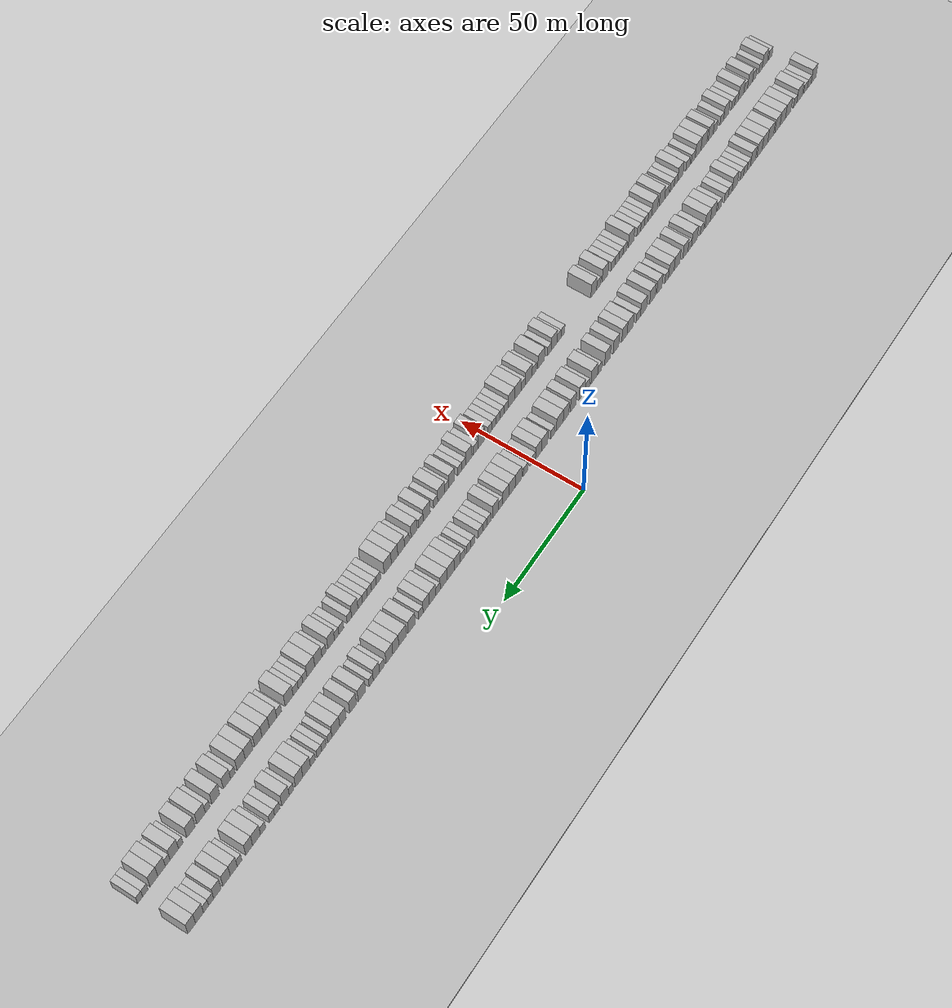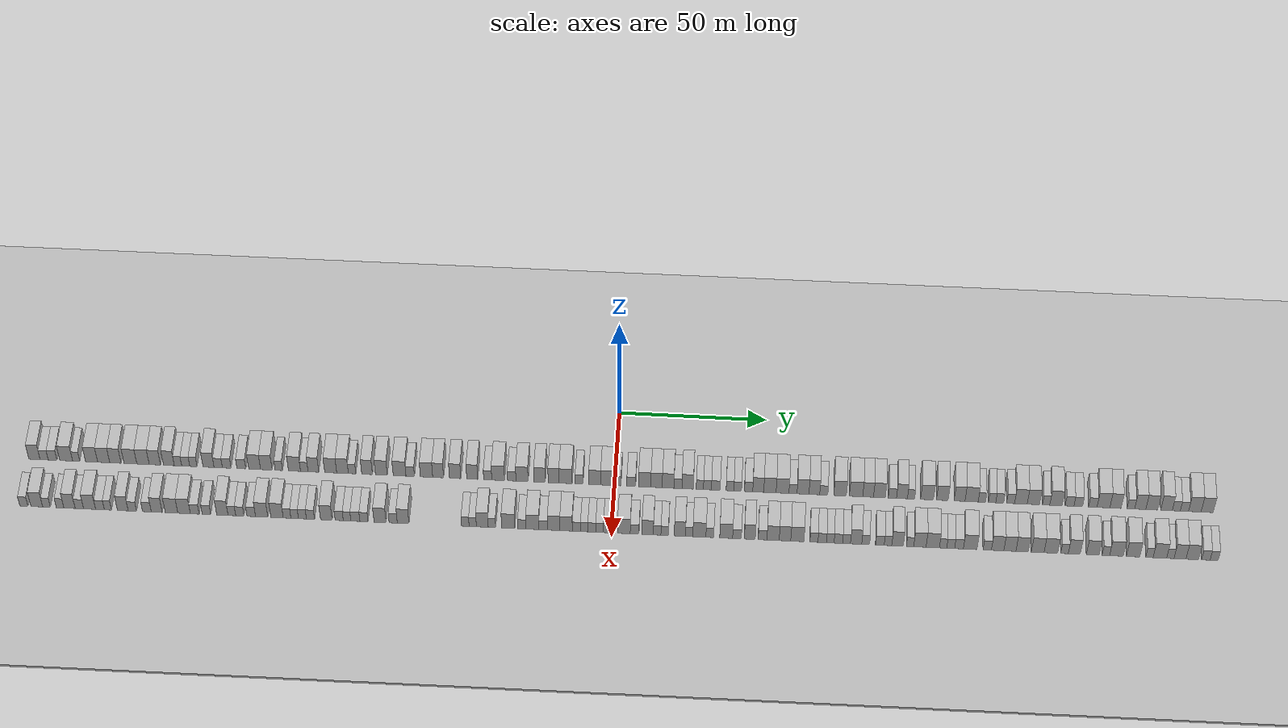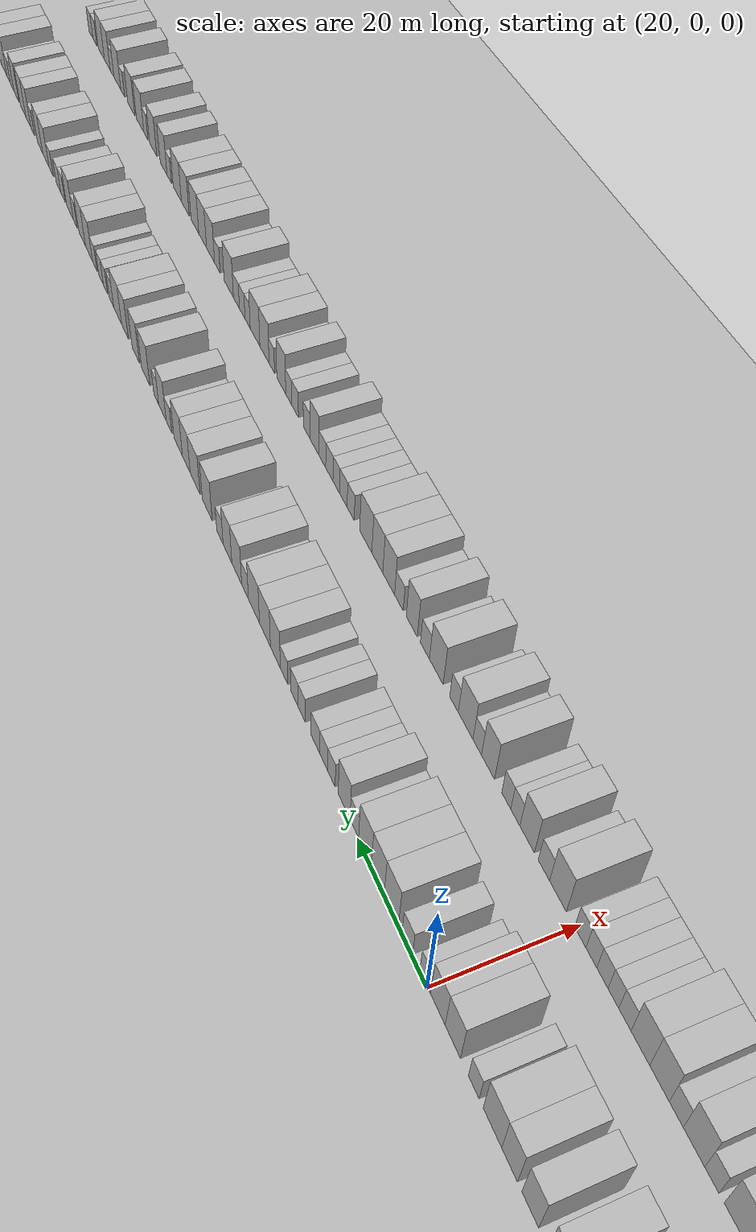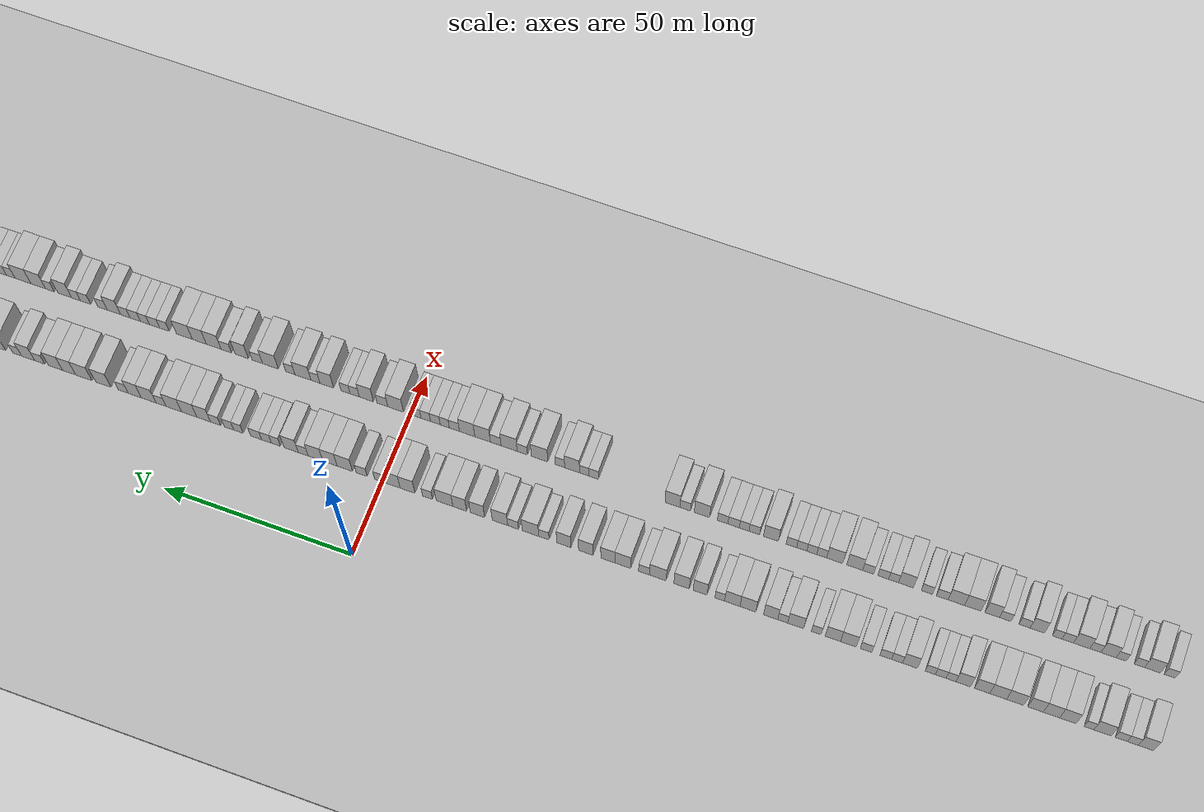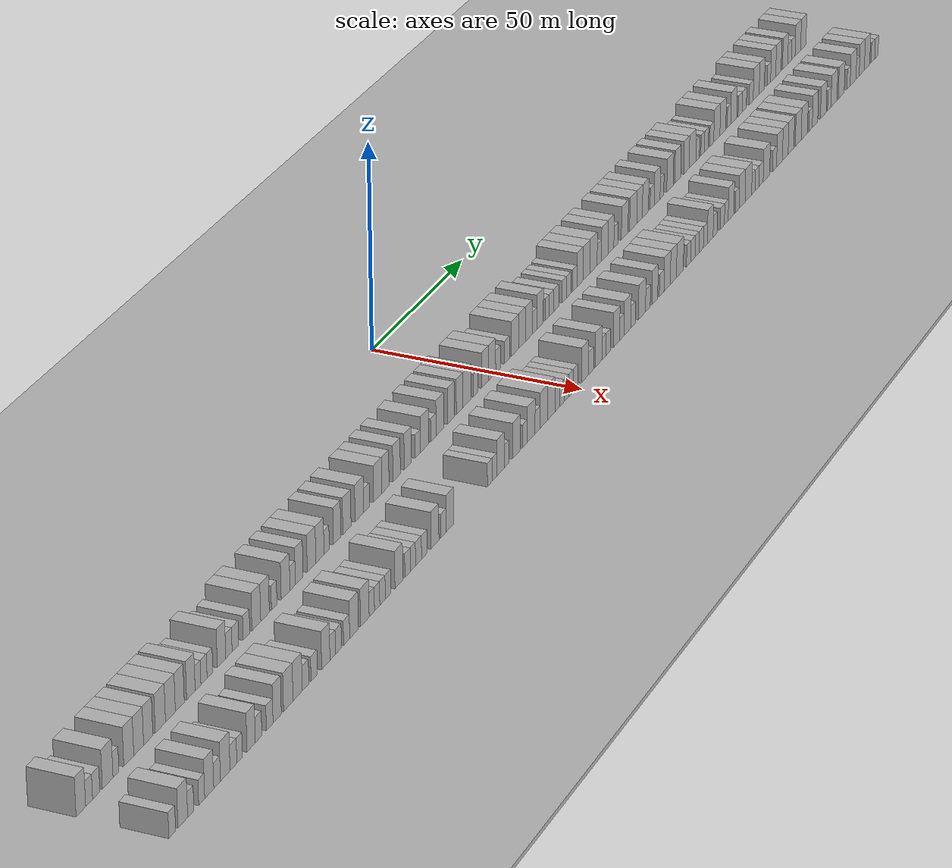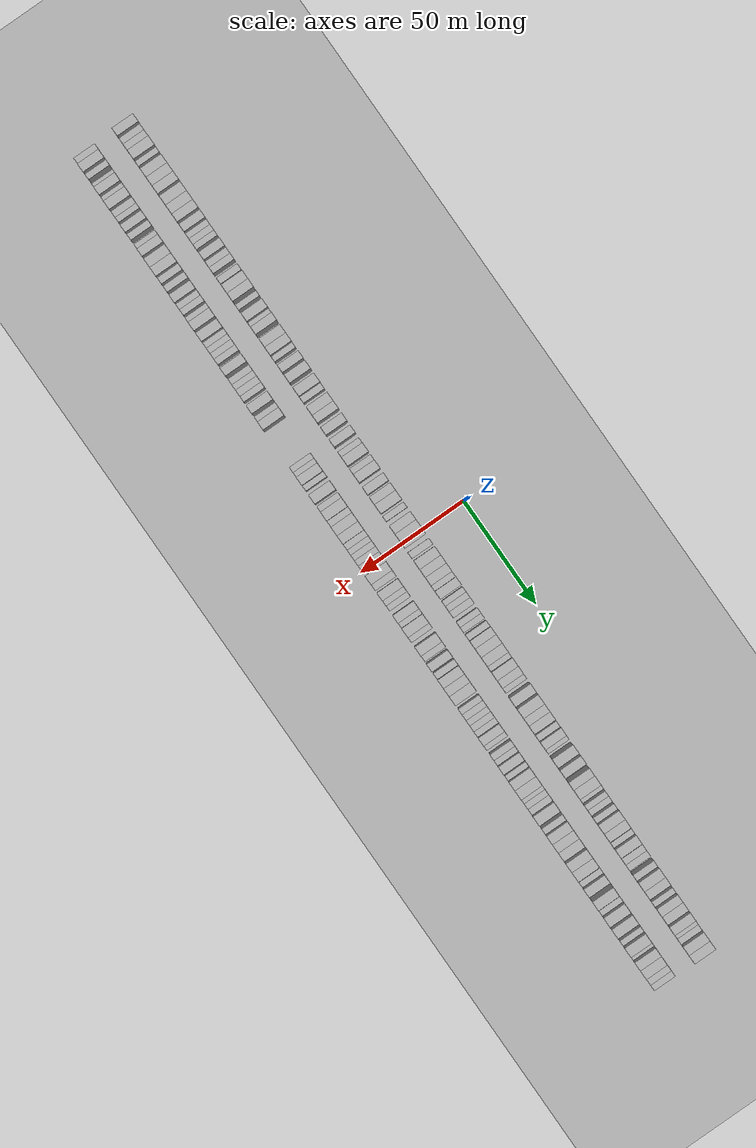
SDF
<?xml version="1.0" encoding="utf-8"?>

<sdf version="1.6">

   <world name="default">

      <gui fullscreen="0">

         <camera name="user_camera">

            <pose>-15 0 4.57585 0 0 0</pose>

            <view_controller>orbit</view_controller>

         </camera>

      </gui>

      <scene>

         <sky>

           <clouds>

             <speed>12</speed>

           </clouds>

         </sky>

         <ambient>0.4 0.4 0.4 1</ambient>

         <background>0.7 0.7 0.7 1</background>

         <shadows>1</shadows>

      </scene>

      <gravity>0 0 -9.8066</gravity>

      <magnetic_field>6e-06 2.3e-05 -4.2e-05</magnetic_field>

      <physics default="0" name="default_physics" type="ode">

         <ode>

            <solver>

               <type>quick</type>

               <iters>10</iters>

               <sor>1.0</sor>

               <use_dynamic_moi_rescaling>0</use_dynamic_moi_rescaling>

            </solver>

            <constraints>

               <cfm>0</cfm>

               <erp>0.2</erp>

               <contact_max_correcting_vel>100</contact_max_correcting_vel>

               <contact_surface_layer>0.001</contact_surface_layer>

            </constraints>

         </ode>

         <max_step_size>0.004</max_step_size>

         <real_time_factor>1</real_time_factor>

         <real_time_update_rate>250</real_time_update_rate>

      </physics>

      <light name="sun" type="directional">

         <cast_shadows>1</cast_shadows>

         <pose>0 0 10 0 0 0</pose>

         <diffuse>0.8 0.8 0.8 1</diffuse>

         <specular>0.2 0.2 0.2 1</specular>

         <attenuation>

            <range>1000</range>

            <constant>0.9</constant>

            <linear>0.01</linear>

            <quadratic>0.001</quadratic>

         </attenuation>

         <direction>-0.5 0.1 -0.9</direction>

      </light>

      <include>

         <name>ground_plane_1</name>

         <uri>model://HANNAS_ground_plane</uri>

         <pose>0 0 0  0 0 0</pose>

      </include>

      <include>

         <name>ground_plane_2</name>

         <uri>model://HANNAS_ground_plane</uri>

         <pose>100 0 0  0 0 0</pose>

      </include>

      <model name="building_1">

         <static>1</static>

         <pose frame="">25.0000 -196.0993 0 0.000000 0.000000 0.000000</pose>

         <link name="link">

            <pose frame="">0 0 4.50 0 0 0</pose>

            <collision name="collision">

               <geometry>

                  <box>

                     <size>10.0000 3.8014 9.0000</size>

                  </box>

               </geometry>

               <max_contacts>10</max_contacts>

               <surface>

                  <contact>

                     <ode/>

                  </contact>

                  <bounce/>

                  <friction>

                     <torsional>

                        <ode/>

                     </torsional>

                     <ode/>

                  </friction>

               </surface>

            </collision>

            <visual name="visual">

               <cast_shadows>0</cast_shadows>

               <geometry>

                  <box>

                     <size>10.0000 3.8014 9.0000</size>

                  </box>

               </geometry>

               <material>

                  <script>

                     <uri>model://HANNAS_wall/materials/scripts</uri>

                     <uri>model://HANNAS_wall/materials/textures</uri>

                     <name>vrc/HANNAS_wall</name>

                  </script>

               </material>

            </visual>

            <self_collide>0</self_collide>

            <enable_wind>0</enable_wind>

            <kinematic>0</kinematic>

         </link>

      </model>

      <model name="building_2">

         <static>1</static>

         <pose frame="">25.0000 -192.8094 0 0.000000 0.000000 0.000000</pose>

         <link name="link">

            <pose frame="">0 0 3.00 0 0 0</pose>

            <collision name="collision">

               <geometry>

                  <box>

                     <size>10.0000 2.7783 6.0000</size>

                  </box>

               </geometry>

               <max_contacts>10</max_contacts>

               <surface>

                  <contact>

                     <ode/>

                  </contact>

                  <bounce/>

                  <friction>

                     <torsional>

                        <ode/>

                     </torsional>

                     <ode/>

                  </friction>

               </surface>

            </collision>

            <visual name="visual">

               <cast_shadows>0</cast_shadows>

               <geometry>

                  <box>

                     <size>10.0000 2.7783 6.0000</size>

                  </box>

               </geometry>

               <material>

                  <script>

                     <uri>model://HANNAS_wall/materials/scripts</uri>

                     <uri>model://HANNAS_wall/materials/textures</uri>

                     <name>vrc/HANNAS_wall</name>

                  </script>

               </material>

            </visual>

            <self_collide>0</self_collide>

            <enable_wind>0</enable_wind>

            <kinematic>0</kinematic>

         </link>

      </model>

      <model name="building_3">

         <static>1</static>

         <pose frame="">25.0000 -189.9572 0 0.000000 0.000000 0.000000</pose>

         <link name="link">

            <pose frame="">0 0 3.00 0 0 0</pose>

            <collision name="collision">

               <geometry>

                  <box>

                     <size>10.0000 2.9262 6.0000</size>

                  </box>

               </geometry>

               <max_contacts>10</max_contacts>

               <surface>

                  <contact>

                     <ode/>

                  </contact>

                  <bounce/>

                  <friction>

                     <torsional>

                        <ode/>

                     </torsional>

                     <ode/>

                  </friction>

               </surface>

            </collision>

            <visual name="visual">

               <cast_shadows>0</cast_shadows>

               <geometry>

                  <box>

                     <size>10.0000 2.9262 6.0000</size>

                  </box>

               </geometry>

               <material>

                  <script>

                     <uri>model://HANNAS_wall/materials/scripts</uri>

                     <uri>model://HANNAS_wall/materials/textures</uri>

                     <name>vrc/HANNAS_wall</name>

                  </script>

               </material>

            </visual>

            <self_collide>0</self_collide>

            <enable_wind>0</enable_wind>

            <kinematic>0</kinematic>

         </link>

      </model>

      <model name="building_4">

         <static>1</static>

         <pose frame="">25.0000 -185.3345 0 0.000000 0.000000 0.000000</pose>

         <link name="link">

            <pose frame="">0 0 4.50 0 0 0</pose>

            <collision name="collision">

               <geometry>

                  <box>

                     <size>10.0000 4.3192 9.0000</size>

                  </box>

               </geometry>

               <max_contacts>10</max_contacts>

               <surface>

                  <contact>

                     <ode/>

                  </contact>

                  <bounce/>

                  <friction>

                     <torsional>

                        <ode/>

                     </torsional>

                     <ode/>

                  </friction>

               </surface>

            </collision>

            <visual name="visual">

               <cast_shadows>0</cast_shadows>

               <geometry>

                  <box>

                     <size>10.0000 4.3192 9.0000</size>

                  </box>

               </geometry>

               <material>

                  <script>

                     <uri>model://HANNAS_wall/materials/scripts</uri>

                     <uri>model://HANNAS_wall/materials/textures</uri>

                     <name>vrc/HANNAS_wall</name>

                  </script>

               </material>

            </visual>

            <self_collide>0</self_collide>

            <enable_wind>0</enable_wind>

            <kinematic>0</kinematic>

         </link>

      </model>

      <model name="building_5">

         <static>1</static>

         <pose frame="">25.0000 -181.9669 0 0.000000 0.000000 0.000000</pose>

         <link name="link">

            <pose frame="">0 0 3.00 0 0 0</pose>

            <collision name="collision">

               <geometry>

                  <box>

                     <size>10.0000 2.4160 6.0000</size>

                  </box>

               </geometry>

               <max_contacts>10</max_contacts>

               <surface>

                  <contact>

                     <ode/>

                  </contact>

                  <bounce/>

                  <friction>

                     <torsional>

                        <ode/>

                     </torsional>

                     <ode/>

                  </friction>

               </surface>

            </collision>

            <visual name="visual">

               <cast_shadows>0</cast_shadows>

               <geometry>

                  <box>

                     <size>10.0000 2.4160 6.0000</size>

                  </box>

               </geometry>

               <material>

                  <script>

                     <uri>model://HANNAS_wall/materials/scripts</uri>

                     <uri>model://HANNAS_wall/materials/textures</uri>

                     <name>vrc/HANNAS_wall</name>

                  </script>

               </material>

            </visual>

            <self_collide>0</self_collide>

            <enable_wind>0</enable_wind>

            <kinematic>0</kinematic>

         </link>

      </model>

      <model name="building_6">

         <static>1</static>

         <pose frame="">25.0000 -176.7037 0 0.000000 0.000000 0.000000</pose>

         <link name="link">

            <pose frame="">0 0 4.50 0 0 0</pose>

            <collision name="collision">

               <geometry>

                  <box>

                     <size>10.0000 4.1104 9.0000</size>

                  </box>

               </geometry>

               <max_contacts>10</max_contacts>

               <surface>

                  <contact>

                     <ode/>

                  </contact>

                  <bounce/>

                  <friction>

                     <torsional>

                        <ode/>

                     </torsional>

                     <ode/>

                  </friction>

               </surface>

            </collision>

            <visual name="visual">

               <cast_shadows>0</cast_shadows>

               <geometry>

                  <box>

                     <size>10.0000 4.1104 9.0000</size>

                  </box>

               </geometry>

               <material>

                  <script>

                     <uri>model://HANNAS_wall/materials/scripts</uri>

                     <uri>model://HANNAS_wall/materials/textures</uri>

                     <name>vrc/HANNAS_wall</name>

                  </script>

               </material>

            </visual>

            <self_collide>0</self_collide>

            <enable_wind>0</enable_wind>

            <kinematic>0</kinematic>

         </link>

      </model>

      <model name="building_7">

         <static>1</static>

         <pose frame="">25.0000 -172.6036 0 0.000000 0.000000 0.000000</pose>

         <link name="link">

            <pose frame="">0 0 4.50 0 0 0</pose>

            <collision name="collision">

               <geometry>

                  <box>

                     <size>10.0000 4.0898 9.0000</size>

                  </box>

               </geometry>

               <max_contacts>10</max_contacts>

               <surface>

                  <contact>

                     <ode/>

                  </contact>

                  <bounce/>

                  <friction>

                     <torsional>

                        <ode/>

                     </torsional>

                     <ode/>

                  </friction>

               </surface>

            </collision>

            <visual name="visual">

               <cast_shadows>0</cast_shadows>

               <geometry>

                  <box>

                     <size>10.0000 4.0898 9.0000</size>

                  </box>

               </geometry>

               <material>

                  <script>

                     <uri>model://HANNAS_wall/materials/scripts</uri>

                     <uri>model://HANNAS_wall/materials/textures</uri>

                     <name>vrc/HANNAS_wall</name>

                  </script>

               </material>

            </visual>

            <self_collide>0</self_collide>

            <enable_wind>0</enable_wind>

            <kinematic>0</kinematic>

         </link>

      </model>

      <model name="building_8">

         <static>1</static>

         <pose frame="">25.0000 -168.6281 0 0.000000 0.000000 0.000000</pose>

         <link name="link">

            <pose frame="">0 0 4.50 0 0 0</pose>

            <collision name="collision">

               <geometry>

                  <box>

                     <size>10.0000 3.8613 9.0000</size>

                  </box>

               </geometry>

               <max_contacts>10</max_contacts>

               <surface>

                  <contact>

                     <ode/>

                  </contact>

                  <bounce/>

                  <friction>

                     <torsional>

                        <ode/>

                     </torsional>

                     <ode/>

                  </friction>

               </surface>

            </collision>

            <visual name="visual">

               <cast_shadows>0</cast_shadows>

               <geometry>

                  <box>

                     <size>10.0000 3.8613 9.0000</size>

                  </box>

               </geometry>

               <material>

                  <script>

                     <uri>model://HANNAS_wall/materials/scripts</uri>

                     <uri>model://HANNAS_wall/materials/textures</uri>

                     <name>vrc/HANNAS_wall</name>

                  </script>

               </material>

            </visual>

            <self_collide>0</self_collide>

            <enable_wind>0</enable_wind>

            <kinematic>0</kinematic>

         </link>

      </model>

      <model name="building_9">

         <static>1</static>

         <pose frame="">25.0000 -163.5331 0 0.000000 0.000000 0.000000</pose>

         <link name="link">

            <pose frame="">0 0 4.50 0 0 0</pose>

            <collision name="collision">

               <geometry>

                  <box>

                     <size>10.0000 4.3288 9.0000</size>

                  </box>

               </geometry>

               <max_contacts>10</max_contacts>

               <surface>

                  <contact>

                     <ode/>

                  </contact>

                  <bounce/>

                  <friction>

                     <torsional>

                        <ode/>

                     </torsional>

                     <ode/>

                  </friction>

               </surface>

            </collision>

            <visual name="visual">

               <cast_shadows>0</cast_shadows>

               <geometry>

                  <box>

                     <size>10.0000 4.3288 9.0000</size>

                  </box>

               </geometry>

               <material>

                  <script>

                     <uri>model://HANNAS_wall/materials/scripts</uri>

                     <uri>model://HANNAS_wall/materials/textures</uri>

                     <name>vrc/HANNAS_wall</name>

                  </script>

               </material>

            </visual>

            <self_collide>0</self_collide>

            <enable_wind>0</enable_wind>

            <kinematic>0</kinematic>

         </link>

      </model>

      <model name="building_10">

         <static>1</static>

         <pose frame="">25.0000 -159.2722 0 0.000000 0.000000 0.000000</pose>

         <link name="link">

            <pose frame="">0 0 4.50 0 0 0</pose>

            <collision name="collision">

               <geometry>

                  <box>

                     <size>10.0000 4.1929 9.0000</size>

                  </box>

               </geometry>

               <max_contacts>10</max_contacts>

               <surface>

                  <contact>

                     <ode/>

                  </contact>

                  <bounce/>

                  <friction>

                     <torsional>

                        <ode/>

                     </torsional>

                     <ode/>

                  </friction>

               </surface>

            </collision>

            <visual name="visual">

               <cast_shadows>0</cast_shadows>

               <geometry>

                  <box>

                     <size>10.0000 4.1929 9.0000</size>

                  </box>

               </geometry>

               <material>

                  <script>

                     <uri>model://HANNAS_wall/materials/scripts</uri>

                     <uri>model://HANNAS_wall/materials/textures</uri>

                     <name>vrc/HANNAS_wall</name>

                  </script>

               </material>

            </visual>

            <self_collide>0</self_collide>

            <enable_wind>0</enable_wind>

            <kinematic>0</kinematic>

         </link>

      </model>

      <model name="building_11">

         <static>1</static>

         <pose frame="">25.0000 -155.2540 0 0.000000 0.000000 0.000000</pose>

         <link name="link">

            <pose frame="">0 0 4.50 0 0 0</pose>

            <collision name="collision">

               <geometry>

                  <box>

                     <size>10.0000 3.8434 9.0000</size>

                  </box>

               </geometry>

               <max_contacts>10</max_contacts>

               <surface>

                  <contact>

                     <ode/>

                  </contact>

                  <bounce/>

                  <friction>

                     <torsional>

                        <ode/>

                     </torsional>

                     <ode/>

                  </friction>

               </surface>

            </collision>

            <visual name="visual">

               <cast_shadows>0</cast_shadows>

               <geometry>

                  <box>

                     <size>10.0000 3.8434 9.0000</size>

                  </box>

               </geometry>

               <material>

                  <script>

                     <uri>model://HANNAS_wall/materials/scripts</uri>

                     <uri>model://HANNAS_wall/materials/textures</uri>

                     <name>vrc/HANNAS_wall</name>

                  </script>

               </material>

            </visual>

            <self_collide>0</self_collide>

            <enable_wind>0</enable_wind>

            <kinematic>0</kinematic>

         </link>

      </model>

      <model name="building_12">

         <static>1</static>

         <pose frame="">25.0000 -150.4967 0 0.000000 0.000000 0.000000</pose>

         <link name="link">

            <pose frame="">0 0 4.50 0 0 0</pose>

            <collision name="collision">

               <geometry>

                  <box>

                     <size>10.0000 3.6713 9.0000</size>

                  </box>

               </geometry>

               <max_contacts>10</max_contacts>

               <surface>

                  <contact>

                     <ode/>

                  </contact>

                  <bounce/>

                  <friction>

                     <torsional>

                        <ode/>

                     </torsional>

                     <ode/>

                  </friction>

               </surface>

            </collision>

            <visual name="visual">

               <cast_shadows>0</cast_shadows>

               <geometry>

                  <box>

                     <size>10.0000 3.6713 9.0000</size>

                  </box>

               </geometry>

               <material>

                  <script>

                     <uri>model://HANNAS_wall/materials/scripts</uri>

                     <uri>model://HANNAS_wall/materials/textures</uri>

                     <name>vrc/HANNAS_wall</name>

                  </script>

               </material>

            </visual>

            <self_collide>0</self_collide>

            <enable_wind>0</enable_wind>

            <kinematic>0</kinematic>

         </link>

      </model>

      <model name="building_13">

         <static>1</static>

         <pose frame="">25.0000 -147.4128 0 0.000000 0.000000 0.000000</pose>

         <link name="link">

            <pose frame="">0 0 3.00 0 0 0</pose>

            <collision name="collision">

               <geometry>

                  <box>

                     <size>10.0000 2.4966 6.0000</size>

                  </box>

               </geometry>

               <max_contacts>10</max_contacts>

               <surface>

                  <contact>

                     <ode/>

                  </contact>

                  <bounce/>

                  <friction>

                     <torsional>

                        <ode/>

                     </torsional>

                     <ode/>

                  </friction>

               </surface>

            </collision>

            <visual name="visual">

               <cast_shadows>0</cast_shadows>

               <geometry>

                  <box>

                     <size>10.0000 2.4966 6.0000</size>

                  </box>

               </geometry>

               <material>

                  <script>

                     <uri>model://HANNAS_wall/materials/scripts</uri>

                     <uri>model://HANNAS_wall/materials/textures</uri>

                     <name>vrc/HANNAS_wall</name>

                  </script>

               </material>

            </visual>

            <self_collide>0</self_collide>

            <enable_wind>0</enable_wind>

            <kinematic>0</kinematic>

         </link>

      </model>

      <model name="building_14">

         <static>1</static>

         <pose frame="">25.0000 -144.8089 0 0.000000 0.000000 0.000000</pose>

         <link name="link">

            <pose frame="">0 0 3.00 0 0 0</pose>

            <collision name="collision">

               <geometry>

                  <box>

                     <size>10.0000 2.7111 6.0000</size>

                  </box>

               </geometry>

               <max_contacts>10</max_contacts>

               <surface>

                  <contact>

                     <ode/>

                  </contact>

                  <bounce/>

                  <friction>

                     <torsional>

                        <ode/>

                     </torsional>

                     <ode/>

                  </friction>

               </surface>

            </collision>

            <visual name="visual">

               <cast_shadows>0</cast_shadows>

               <geometry>

                  <box>

                     <size>10.0000 2.7111 6.0000</size>

                  </box>

               </geometry>

               <material>

                  <script>

                     <uri>model://HANNAS_wall/materials/scripts</uri>

                     <uri>model://HANNAS_wall/materials/textures</uri>

                     <name>vrc/HANNAS_wall</name>

                  </script>

               </material>

            </visual>

            <self_collide>0</self_collide>

            <enable_wind>0</enable_wind>

            <kinematic>0</kinematic>

         </link>

      </model>

      <model name="building_15">

         <static>1</static>

         <pose frame="">25.0000 -142.1972 0 0.000000 0.000000 0.000000</pose>

         <link name="link">

            <pose frame="">0 0 3.00 0 0 0</pose>

            <collision name="collision">

               <geometry>

                  <box>

                     <size>10.0000 2.5124 6.0000</size>

                  </box>

               </geometry>

               <max_contacts>10</max_contacts>

               <surface>

                  <contact>

                     <ode/>

                  </contact>

                  <bounce/>

                  <friction>

                     <torsional>

                        <ode/>

                     </torsional>

                     <ode/>

                  </friction>

               </surface>

            </collision>

            <visual name="visual">

               <cast_shadows>0</cast_shadows>

               <geometry>

                  <box>

                     <size>10.0000 2.5124 6.0000</size>

                  </box>

               </geometry>

               <material>

                  <script>

                     <uri>model://HANNAS_wall/materials/scripts</uri>

                     <uri>model://HANNAS_wall/materials/textures</uri>

                     <name>vrc/HANNAS_wall</name>

                  </script>

               </material>

            </visual>

            <self_collide>0</self_collide>

            <enable_wind>0</enable_wind>

            <kinematic>0</kinematic>

         </link>

      </model>

      <model name="building_16">

         <static>1</static>

         <pose frame="">25.0000 -137.0712 0 0.000000 0.000000 0.000000</pose>

         <link name="link">

            <pose frame="">0 0 4.50 0 0 0</pose>

            <collision name="collision">

               <geometry>

                  <box>

                     <size>10.0000 3.7395 9.0000</size>

                  </box>

               </geometry>

               <max_contacts>10</max_contacts>

               <surface>

                  <contact>

                     <ode/>

                  </contact>

                  <bounce/>

                  <friction>

                     <torsional>

                        <ode/>

                     </torsional>

                     <ode/>

                  </friction>

               </surface>

            </collision>

            <visual name="visual">

               <cast_shadows>0</cast_shadows>

               <geometry>

                  <box>

                     <size>10.0000 3.7395 9.0000</size>

                  </box>

               </geometry>

               <material>

                  <script>

                     <uri>model://HANNAS_wall/materials/scripts</uri>

                     <uri>model://HANNAS_wall/materials/textures</uri>

                     <name>vrc/HANNAS_wall</name>

                  </script>

               </material>

            </visual>

            <self_collide>0</self_collide>

            <enable_wind>0</enable_wind>

            <kinematic>0</kinematic>

         </link>

      </model>

      <model name="building_17">

         <static>1</static>

         <pose frame="">25.0000 -133.7946 0 0.000000 0.000000 0.000000</pose>

         <link name="link">

            <pose frame="">0 0 3.00 0 0 0</pose>

            <collision name="collision">

               <geometry>

                  <box>

                     <size>10.0000 2.8137 6.0000</size>

                  </box>

               </geometry>

               <max_contacts>10</max_contacts>

               <surface>

                  <contact>

                     <ode/>

                  </contact>

                  <bounce/>

                  <friction>

                     <torsional>

                        <ode/>

                     </torsional>

                     <ode/>

                  </friction>

               </surface>

            </collision>

            <visual name="visual">

               <cast_shadows>0</cast_shadows>

               <geometry>

                  <box>

                     <size>10.0000 2.8137 6.0000</size>

                  </box>

               </geometry>

               <material>

                  <script>

                     <uri>model://HANNAS_wall/materials/scripts</uri>

                     <uri>model://HANNAS_wall/materials/textures</uri>

                     <name>vrc/HANNAS_wall</name>

                  </script>

               </material>

            </visual>

            <self_collide>0</self_collide>

            <enable_wind>0</enable_wind>

            <kinematic>0</kinematic>

         </link>

      </model>

      <model name="building_18">

         <static>1</static>

         <pose frame="">25.0000 -130.9138 0 0.000000 0.000000 0.000000</pose>

         <link name="link">

            <pose frame="">0 0 3.00 0 0 0</pose>

            <collision name="collision">

               <geometry>

                  <box>

                     <size>10.0000 2.9480 6.0000</size>

                  </box>

               </geometry>

               <max_contacts>10</max_contacts>

               <surface>

                  <contact>

                     <ode/>

                  </contact>

                  <bounce/>

                  <friction>

                     <torsional>

                        <ode/>

                     </torsional>

                     <ode/>

                  </friction>

               </surface>

            </collision>

            <visual name="visual">

               <cast_shadows>0</cast_shadows>

               <geometry>

                  <box>

                     <size>10.0000 2.9480 6.0000</size>

                  </box>

               </geometry>

               <material>

                  <script>

                     <uri>model://HANNAS_wall/materials/scripts</uri>

                     <uri>model://HANNAS_wall/materials/textures</uri>

                     <name>vrc/HANNAS_wall</name>

                  </script>

               </material>

            </visual>

            <self_collide>0</self_collide>

            <enable_wind>0</enable_wind>

            <kinematic>0</kinematic>

         </link>

      </model>

      <model name="building_19">

         <static>1</static>

         <pose frame="">25.0000 -125.9477 0 0.000000 0.000000 0.000000</pose>

         <link name="link">

            <pose frame="">0 0 3.00 0 0 0</pose>

            <collision name="collision">

               <geometry>

                  <box>

                     <size>10.0000 2.9842 6.0000</size>

                  </box>

               </geometry>

               <max_contacts>10</max_contacts>

               <surface>

                  <contact>

                     <ode/>

                  </contact>

                  <bounce/>

                  <friction>

                     <torsional>

                        <ode/>

                     </torsional>

                     <ode/>

                  </friction>

               </surface>

            </collision>

            <visual name="visual">

               <cast_shadows>0</cast_shadows>

               <geometry>

                  <box>

                     <size>10.0000 2.9842 6.0000</size>

                  </box>

               </geometry>

               <material>

                  <script>

                     <uri>model://HANNAS_wall/materials/scripts</uri>

                     <uri>model://HANNAS_wall/materials/textures</uri>

                     <name>vrc/HANNAS_wall</name>

                  </script>

               </material>

            </visual>

            <self_collide>0</self_collide>

            <enable_wind>0</enable_wind>

            <kinematic>0</kinematic>

         </link>

      </model>

      <model name="building_20">

         <static>1</static>

         <pose frame="">25.0000 -121.4546 0 0.000000 0.000000 0.000000</pose>

         <link name="link">

            <pose frame="">0 0 4.50 0 0 0</pose>

            <collision name="collision">

               <geometry>

                  <box>

                     <size>10.0000 4.0020 9.0000</size>

                  </box>

               </geometry>

               <max_contacts>10</max_contacts>

               <surface>

                  <contact>

                     <ode/>

                  </contact>

                  <bounce/>

                  <friction>

                     <torsional>

                        <ode/>

                     </torsional>

                     <ode/>

                  </friction>

               </surface>

            </collision>

            <visual name="visual">

               <cast_shadows>0</cast_shadows>

               <geometry>

                  <box>

                     <size>10.0000 4.0020 9.0000</size>

                  </box>

               </geometry>

               <material>

                  <script>

                     <uri>model://HANNAS_wall/materials/scripts</uri>

                     <uri>model://HANNAS_wall/materials/textures</uri>

                     <name>vrc/HANNAS_wall</name>

                  </script>

               </material>

            </visual>

            <self_collide>0</self_collide>

            <enable_wind>0</enable_wind>

            <kinematic>0</kinematic>

         </link>

      </model>

      <model name="building_21">

         <static>1</static>

         <pose frame="">25.0000 -117.4886 0 0.000000 0.000000 0.000000</pose>

         <link name="link">

            <pose frame="">0 0 4.50 0 0 0</pose>

            <collision name="collision">

               <geometry>

                  <box>

                     <size>10.0000 3.9301 9.0000</size>

                  </box>

               </geometry>

               <max_contacts>10</max_contacts>

               <surface>

                  <contact>

                     <ode/>

                  </contact>

                  <bounce/>

                  <friction>

                     <torsional>

                        <ode/>

                     </torsional>

                     <ode/>

                  </friction>

               </surface>

            </collision>

            <visual name="visual">

               <cast_shadows>0</cast_shadows>

               <geometry>

                  <box>

                     <size>10.0000 3.9301 9.0000</size>

                  </box>

               </geometry>

               <material>

                  <script>

                     <uri>model://HANNAS_wall/materials/scripts</uri>

                     <uri>model://HANNAS_wall/materials/textures</uri>

                     <name>vrc/HANNAS_wall</name>

                  </script>

               </material>

            </visual>

            <self_collide>0</self_collide>

            <enable_wind>0</enable_wind>

            <kinematic>0</kinematic>

         </link>

      </model>

      <model name="building_22">

         <static>1</static>

         <pose frame="">25.0000 -113.2681 0 0.000000 0.000000 0.000000</pose>

         <link name="link">

            <pose frame="">0 0 3.00 0 0 0</pose>

            <collision name="collision">

               <geometry>

                  <box>

                     <size>10.0000 2.5108 6.0000</size>

                  </box>

               </geometry>

               <max_contacts>10</max_contacts>

               <surface>

                  <contact>

                     <ode/>

                  </contact>

                  <bounce/>

                  <friction>

                     <torsional>

                        <ode/>

                     </torsional>

                     <ode/>

                  </friction>

               </surface>

            </collision>

            <visual name="visual">

               <cast_shadows>0</cast_shadows>

               <geometry>

                  <box>

                     <size>10.0000 2.5108 6.0000</size>

                  </box>

               </geometry>

               <material>

                  <script>

                     <uri>model://HANNAS_wall/materials/scripts</uri>

                     <uri>model://HANNAS_wall/materials/textures</uri>

                     <name>vrc/HANNAS_wall</name>

                  </script>

               </material>

            </visual>

            <self_collide>0</self_collide>

            <enable_wind>0</enable_wind>

            <kinematic>0</kinematic>

         </link>

      </model>

      <model name="building_23">

         <static>1</static>

         <pose frame="">25.0000 -107.9738 0 0.000000 0.000000 0.000000</pose>

         <link name="link">

            <pose frame="">0 0 4.50 0 0 0</pose>

            <collision name="collision">

               <geometry>

                  <box>

                     <size>10.0000 4.0778 9.0000</size>

                  </box>

               </geometry>

               <max_contacts>10</max_contacts>

               <surface>

                  <contact>

                     <ode/>

                  </contact>

                  <bounce/>

                  <friction>

                     <torsional>

                        <ode/>

                     </torsional>

                     <ode/>

                  </friction>

               </surface>

            </collision>

            <visual name="visual">

               <cast_shadows>0</cast_shadows>

               <geometry>

                  <box>

                     <size>10.0000 4.0778 9.0000</size>

                  </box>

               </geometry>

               <material>

                  <script>

                     <uri>model://HANNAS_wall/materials/scripts</uri>

                     <uri>model://HANNAS_wall/materials/textures</uri>

                     <name>vrc/HANNAS_wall</name>

                  </script>

               </material>

            </visual>

            <self_collide>0</self_collide>

            <enable_wind>0</enable_wind>

            <kinematic>0</kinematic>

         </link>

      </model>

      <model name="building_24">

         <static>1</static>

         <pose frame="">25.0000 -104.6739 0 0.000000 0.000000 0.000000</pose>

         <link name="link">

            <pose frame="">0 0 3.00 0 0 0</pose>

            <collision name="collision">

               <geometry>

                  <box>

                     <size>10.0000 2.5218 6.0000</size>

                  </box>

               </geometry>

               <max_contacts>10</max_contacts>

               <surface>

                  <contact>

                     <ode/>

                  </contact>

                  <bounce/>

                  <friction>

                     <torsional>

                        <ode/>

                     </torsional>

                     <ode/>

                  </friction>

               </surface>

            </collision>

            <visual name="visual">

               <cast_shadows>0</cast_shadows>

               <geometry>

                  <box>

                     <size>10.0000 2.5218 6.0000</size>

                  </box>

               </geometry>

               <material>

                  <script>

                     <uri>model://HANNAS_wall/materials/scripts</uri>

                     <uri>model://HANNAS_wall/materials/textures</uri>

                     <name>vrc/HANNAS_wall</name>

                  </script>

               </material>

            </visual>

            <self_collide>0</self_collide>

            <enable_wind>0</enable_wind>

            <kinematic>0</kinematic>

         </link>

      </model>

      <model name="building_25">

         <static>1</static>

         <pose frame="">25.0000 -101.5927 0 0.000000 0.000000 0.000000</pose>

         <link name="link">

            <pose frame="">0 0 4.50 0 0 0</pose>

            <collision name="collision">

               <geometry>

                  <box>

                     <size>10.0000 3.6406 9.0000</size>

                  </box>

               </geometry>

               <max_contacts>10</max_contacts>

               <surface>

                  <contact>

                     <ode/>

                  </contact>

                  <bounce/>

                  <friction>

                     <torsional>

                        <ode/>

                     </torsional>

                     <ode/>

                  </friction>

               </surface>

            </collision>

            <visual name="visual">

               <cast_shadows>0</cast_shadows>

               <geometry>

                  <box>

                     <size>10.0000 3.6406 9.0000</size>

                  </box>

               </geometry>

               <material>

                  <script>

                     <uri>model://HANNAS_wall/materials/scripts</uri>

                     <uri>model://HANNAS_wall/materials/textures</uri>

                     <name>vrc/HANNAS_wall</name>

                  </script>

               </material>

            </visual>

            <self_collide>0</self_collide>

            <enable_wind>0</enable_wind>

            <kinematic>0</kinematic>

         </link>

      </model>

      <model name="building_26">

         <static>1</static>

         <pose frame="">25.0000 -95.7448 0 0.000000 0.000000 0.000000</pose>

         <link name="link">

            <pose frame="">0 0 4.50 0 0 0</pose>

            <collision name="collision">

               <geometry>

                  <box>

                     <size>10.0000 4.0553 9.0000</size>

                  </box>

               </geometry>

               <max_contacts>10</max_contacts>

               <surface>

                  <contact>

                     <ode/>

                  </contact>

                  <bounce/>

                  <friction>

                     <torsional>

                        <ode/>

                     </torsional>

                     <ode/>

                  </friction>

               </surface>

            </collision>

            <visual name="visual">

               <cast_shadows>0</cast_shadows>

               <geometry>

                  <box>

                     <size>10.0000 4.0553 9.0000</size>

                  </box>

               </geometry>

               <material>

                  <script>

                     <uri>model://HANNAS_wall/materials/scripts</uri>

                     <uri>model://HANNAS_wall/materials/textures</uri>

                     <name>vrc/HANNAS_wall</name>

                  </script>

               </material>

            </visual>

            <self_collide>0</self_collide>

            <enable_wind>0</enable_wind>

            <kinematic>0</kinematic>

         </link>

      </model>

      <model name="building_27">

         <static>1</static>

         <pose frame="">25.0000 -91.7479 0 0.000000 0.000000 0.000000</pose>

         <link name="link">

            <pose frame="">0 0 4.50 0 0 0</pose>

            <collision name="collision">

               <geometry>

                  <box>

                     <size>10.0000 3.9386 9.0000</size>

                  </box>

               </geometry>

               <max_contacts>10</max_contacts>

               <surface>

                  <contact>

                     <ode/>

                  </contact>

                  <bounce/>

                  <friction>

                     <torsional>

                        <ode/>

                     </torsional>

                     <ode/>

                  </friction>

               </surface>

            </collision>

            <visual name="visual">

               <cast_shadows>0</cast_shadows>

               <geometry>

                  <box>

                     <size>10.0000 3.9386 9.0000</size>

                  </box>

               </geometry>

               <material>

                  <script>

                     <uri>model://HANNAS_wall/materials/scripts</uri>

                     <uri>model://HANNAS_wall/materials/textures</uri>

                     <name>vrc/HANNAS_wall</name>

                  </script>

               </material>

            </visual>

            <self_collide>0</self_collide>

            <enable_wind>0</enable_wind>

            <kinematic>0</kinematic>

         </link>

      </model>

      <model name="building_28">

         <static>1</static>

         <pose frame="">25.0000 -88.5145 0 0.000000 0.000000 0.000000</pose>

         <link name="link">

            <pose frame="">0 0 3.00 0 0 0</pose>

            <collision name="collision">

               <geometry>

                  <box>

                     <size>10.0000 2.5282 6.0000</size>

                  </box>

               </geometry>

               <max_contacts>10</max_contacts>

               <surface>

                  <contact>

                     <ode/>

                  </contact>

                  <bounce/>

                  <friction>

                     <torsional>

                        <ode/>

                     </torsional>

                     <ode/>

                  </friction>

               </surface>

            </collision>

            <visual name="visual">

               <cast_shadows>0</cast_shadows>

               <geometry>

                  <box>

                     <size>10.0000 2.5282 6.0000</size>

                  </box>

               </geometry>

               <material>

                  <script>

                     <uri>model://HANNAS_wall/materials/scripts</uri>

                     <uri>model://HANNAS_wall/materials/textures</uri>

                     <name>vrc/HANNAS_wall</name>

                  </script>

               </material>

            </visual>

            <self_collide>0</self_collide>

            <enable_wind>0</enable_wind>

            <kinematic>0</kinematic>

         </link>

      </model>

      <model name="building_29">

         <static>1</static>

         <pose frame="">25.0000 -83.4454 0 0.000000 0.000000 0.000000</pose>

         <link name="link">

            <pose frame="">0 0 4.50 0 0 0</pose>

            <collision name="collision">

               <geometry>

                  <box>

                     <size>10.0000 3.6101 9.0000</size>

                  </box>

               </geometry>

               <max_contacts>10</max_contacts>

               <surface>

                  <contact>

                     <ode/>

                  </contact>

                  <bounce/>

                  <friction>

                     <torsional>

                        <ode/>

                     </torsional>

                     <ode/>

                  </friction>

               </surface>

            </collision>

            <visual name="visual">

               <cast_shadows>0</cast_shadows>

               <geometry>

                  <box>

                     <size>10.0000 3.6101 9.0000</size>

                  </box>

               </geometry>

               <material>

                  <script>

                     <uri>model://HANNAS_wall/materials/scripts</uri>

                     <uri>model://HANNAS_wall/materials/textures</uri>

                     <name>vrc/HANNAS_wall</name>

                  </script>

               </material>

            </visual>

            <self_collide>0</self_collide>

            <enable_wind>0</enable_wind>

            <kinematic>0</kinematic>

         </link>

      </model>

      <model name="building_30">

         <static>1</static>

         <pose frame="">25.0000 -78.6407 0 0.000000 0.000000 0.000000</pose>

         <link name="link">

            <pose frame="">0 0 4.50 0 0 0</pose>

            <collision name="collision">

               <geometry>

                  <box>

                     <size>10.0000 3.9992 9.0000</size>

                  </box>

               </geometry>

               <max_contacts>10</max_contacts>

               <surface>

                  <contact>

                     <ode/>

                  </contact>

                  <bounce/>

                  <friction>

                     <torsional>

                        <ode/>

                     </torsional>

                     <ode/>

                  </friction>

               </surface>

            </collision>

            <visual name="visual">

               <cast_shadows>0</cast_shadows>

               <geometry>

                  <box>

                     <size>10.0000 3.9992 9.0000</size>

                  </box>

               </geometry>

               <material>

                  <script>

                     <uri>model://HANNAS_wall/materials/scripts</uri>

                     <uri>model://HANNAS_wall/materials/textures</uri>

                     <name>vrc/HANNAS_wall</name>

                  </script>

               </material>

            </visual>

            <self_collide>0</self_collide>

            <enable_wind>0</enable_wind>

            <kinematic>0</kinematic>

         </link>

      </model>

      <model name="building_31">

         <static>1</static>

         <pose frame="">25.0000 -72.4856 0 0.000000 0.000000 0.000000</pose>

         <link name="link">

            <pose frame="">0 0 4.50 0 0 0</pose>

            <collision name="collision">

               <geometry>

                  <box>

                     <size>10.0000 4.3109 9.0000</size>

                  </box>

               </geometry>

               <max_contacts>10</max_contacts>

               <surface>

                  <contact>

                     <ode/>

                  </contact>

                  <bounce/>

                  <friction>

                     <torsional>

                        <ode/>

                     </torsional>

                     <ode/>

                  </friction>

               </surface>

            </collision>

            <visual name="visual">

               <cast_shadows>0</cast_shadows>

               <geometry>

                  <box>

                     <size>10.0000 4.3109 9.0000</size>

                  </box>

               </geometry>

               <material>

                  <script>

                     <uri>model://HANNAS_wall/materials/scripts</uri>

                     <uri>model://HANNAS_wall/materials/textures</uri>

                     <name>vrc/HANNAS_wall</name>

                  </script>

               </material>

            </visual>

            <self_collide>0</self_collide>

            <enable_wind>0</enable_wind>

            <kinematic>0</kinematic>

         </link>

      </model>

      <model name="building_32">

         <static>1</static>

         <pose frame="">25.0000 -68.9011 0 0.000000 0.000000 0.000000</pose>

         <link name="link">

            <pose frame="">0 0 3.00 0 0 0</pose>

            <collision name="collision">

               <geometry>

                  <box>

                     <size>10.0000 2.8582 6.0000</size>

                  </box>

               </geometry>

               <max_contacts>10</max_contacts>

               <surface>

                  <contact>

                     <ode/>

                  </contact>

                  <bounce/>

                  <friction>

                     <torsional>

                        <ode/>

                     </torsional>

                     <ode/>

                  </friction>

               </surface>

            </collision>

            <visual name="visual">

               <cast_shadows>0</cast_shadows>

               <geometry>

                  <box>

                     <size>10.0000 2.8582 6.0000</size>

                  </box>

               </geometry>

               <material>

                  <script>

                     <uri>model://HANNAS_wall/materials/scripts</uri>

                     <uri>model://HANNAS_wall/materials/textures</uri>

                     <name>vrc/HANNAS_wall</name>

                  </script>

               </material>

            </visual>

            <self_collide>0</self_collide>

            <enable_wind>0</enable_wind>

            <kinematic>0</kinematic>

         </link>

      </model>

      <model name="building_33">

         <static>1</static>

         <pose frame="">25.0000 -63.3956 0 0.000000 0.000000 0.000000</pose>

         <link name="link">

            <pose frame="">0 0 4.50 0 0 0</pose>

            <collision name="collision">

               <geometry>

                  <box>

                     <size>10.0000 4.1528 9.0000</size>

                  </box>

               </geometry>

               <max_contacts>10</max_contacts>

               <surface>

                  <contact>

                     <ode/>

                  </contact>

                  <bounce/>

                  <friction>

                     <torsional>

                        <ode/>

                     </torsional>

                     <ode/>

                  </friction>

               </surface>

            </collision>

            <visual name="visual">

               <cast_shadows>0</cast_shadows>

               <geometry>

                  <box>

                     <size>10.0000 4.1528 9.0000</size>

                  </box>

               </geometry>

               <material>

                  <script>

                     <uri>model://HANNAS_wall/materials/scripts</uri>

                     <uri>model://HANNAS_wall/materials/textures</uri>

                     <name>vrc/HANNAS_wall</name>

                  </script>

               </material>

            </visual>

            <self_collide>0</self_collide>

            <enable_wind>0</enable_wind>

            <kinematic>0</kinematic>

         </link>

      </model>

      <model name="building_34">

         <static>1</static>

         <pose frame="">25.0000 -59.4867 0 0.000000 0.000000 0.000000</pose>

         <link name="link">

            <pose frame="">0 0 4.50 0 0 0</pose>

            <collision name="collision">

               <geometry>

                  <box>

                     <size>10.0000 3.6648 9.0000</size>

                  </box>

               </geometry>

               <max_contacts>10</max_contacts>

               <surface>

                  <contact>

                     <ode/>

                  </contact>

                  <bounce/>

                  <friction>

                     <torsional>

                        <ode/>

                     </torsional>

                     <ode/>

                  </friction>

               </surface>

            </collision>

            <visual name="visual">

               <cast_shadows>0</cast_shadows>

               <geometry>

                  <box>

                     <size>10.0000 3.6648 9.0000</size>

                  </box>

               </geometry>

               <material>

                  <script>

                     <uri>model://HANNAS_wall/materials/scripts</uri>

                     <uri>model://HANNAS_wall/materials/textures</uri>

                     <name>vrc/HANNAS_wall</name>

                  </script>

               </material>

            </visual>

            <self_collide>0</self_collide>

            <enable_wind>0</enable_wind>

            <kinematic>0</kinematic>

         </link>

      </model>

      <model name="building_35">

         <static>1</static>

         <pose frame="">25.0000 -53.7519 0 0.000000 0.000000 0.000000</pose>

         <link name="link">

            <pose frame="">0 0 4.50 0 0 0</pose>

            <collision name="collision">

               <geometry>

                  <box>

                     <size>10.0000 3.8049 9.0000</size>

                  </box>

               </geometry>

               <max_contacts>10</max_contacts>

               <surface>

                  <contact>

                     <ode/>

                  </contact>

                  <bounce/>

                  <friction>

                     <torsional>

                        <ode/>

                     </torsional>

                     <ode/>

                  </friction>

               </surface>

            </collision>

            <visual name="visual">

               <cast_shadows>0</cast_shadows>

               <geometry>

                  <box>

                     <size>10.0000 3.8049 9.0000</size>

                  </box>

               </geometry>

               <material>

                  <script>

                     <uri>model://HANNAS_wall/materials/scripts</uri>

                     <uri>model://HANNAS_wall/materials/textures</uri>

                     <name>vrc/HANNAS_wall</name>

                  </script>

               </material>

            </visual>

            <self_collide>0</self_collide>

            <enable_wind>0</enable_wind>

            <kinematic>0</kinematic>

         </link>

      </model>

      <model name="building_36">

         <static>1</static>

         <pose frame="">25.0000 -47.9954 0 0.000000 0.000000 0.000000</pose>

         <link name="link">

            <pose frame="">0 0 4.50 0 0 0</pose>

            <collision name="collision">

               <geometry>

                  <box>

                     <size>10.0000 3.7081 9.0000</size>

                  </box>

               </geometry>

               <max_contacts>10</max_contacts>

               <surface>

                  <contact>

                     <ode/>

                  </contact>

                  <bounce/>

                  <friction>

                     <torsional>

                        <ode/>

                     </torsional>

                     <ode/>

                  </friction>

               </surface>

            </collision>

            <visual name="visual">

               <cast_shadows>0</cast_shadows>

               <geometry>

                  <box>

                     <size>10.0000 3.7081 9.0000</size>

                  </box>

               </geometry>

               <material>

                  <script>

                     <uri>model://HANNAS_wall/materials/scripts</uri>

                     <uri>model://HANNAS_wall/materials/textures</uri>

                     <name>vrc/HANNAS_wall</name>

                  </script>

               </material>

            </visual>

            <self_collide>0</self_collide>

            <enable_wind>0</enable_wind>

            <kinematic>0</kinematic>

         </link>

      </model>

      <model name="building_37">

         <static>1</static>

         <pose frame="">25.0000 -42.7801 0 0.000000 0.000000 0.000000</pose>

         <link name="link">

            <pose frame="">0 0 3.00 0 0 0</pose>

            <collision name="collision">

               <geometry>

                  <box>

                     <size>10.0000 2.7225 6.0000</size>

                  </box>

               </geometry>

               <max_contacts>10</max_contacts>

               <surface>

                  <contact>

                     <ode/>

                  </contact>

                  <bounce/>

                  <friction>

                     <torsional>

                        <ode/>

                     </torsional>

                     <ode/>

                  </friction>

               </surface>

            </collision>

            <visual name="visual">

               <cast_shadows>0</cast_shadows>

               <geometry>

                  <box>

                     <size>10.0000 2.7225 6.0000</size>

                  </box>

               </geometry>

               <material>

                  <script>

                     <uri>model://HANNAS_wall/materials/scripts</uri>

                     <uri>model://HANNAS_wall/materials/textures</uri>

                     <name>vrc/HANNAS_wall</name>

                  </script>

               </material>

            </visual>

            <self_collide>0</self_collide>

            <enable_wind>0</enable_wind>

            <kinematic>0</kinematic>

         </link>

      </model>

      <model name="building_38">

         <static>1</static>

         <pose frame="">25.0000 -39.2582 0 0.000000 0.000000 0.000000</pose>

         <link name="link">

            <pose frame="">0 0 4.50 0 0 0</pose>

            <collision name="collision">

               <geometry>

                  <box>

                     <size>10.0000 4.3212 9.0000</size>

                  </box>

               </geometry>

               <max_contacts>10</max_contacts>

               <surface>

                  <contact>

                     <ode/>

                  </contact>

                  <bounce/>

                  <friction>

                     <torsional>

                        <ode/>

                     </torsional>

                     <ode/>

                  </friction>

               </surface>

            </collision>

            <visual name="visual">

               <cast_shadows>0</cast_shadows>

               <geometry>

                  <box>

                     <size>10.0000 4.3212 9.0000</size>

                  </box>

               </geometry>

               <material>

                  <script>

                     <uri>model://HANNAS_wall/materials/scripts</uri>

                     <uri>model://HANNAS_wall/materials/textures</uri>

                     <name>vrc/HANNAS_wall</name>

                  </script>

               </material>

            </visual>

            <self_collide>0</self_collide>

            <enable_wind>0</enable_wind>

            <kinematic>0</kinematic>

         </link>

      </model>

      <model name="building_39">

         <static>1</static>

         <pose frame="">25.0000 -34.6795 0 0.000000 0.000000 0.000000</pose>

         <link name="link">

            <pose frame="">0 0 3.00 0 0 0</pose>

            <collision name="collision">

               <geometry>

                  <box>

                     <size>10.0000 2.8363 6.0000</size>

                  </box>

               </geometry>

               <max_contacts>10</max_contacts>

               <surface>

                  <contact>

                     <ode/>

                  </contact>

                  <bounce/>

                  <friction>

                     <torsional>

                        <ode/>

                     </torsional>

                     <ode/>

                  </friction>

               </surface>

            </collision>

            <visual name="visual">

               <cast_shadows>0</cast_shadows>

               <geometry>

                  <box>

                     <size>10.0000 2.8363 6.0000</size>

                  </box>

               </geometry>

               <material>

                  <script>

                     <uri>model://HANNAS_wall/materials/scripts</uri>

                     <uri>model://HANNAS_wall/materials/textures</uri>

                     <name>vrc/HANNAS_wall</name>

                  </script>

               </material>

            </visual>

            <self_collide>0</self_collide>

            <enable_wind>0</enable_wind>

            <kinematic>0</kinematic>

         </link>

      </model>

      <model name="building_40">

         <static>1</static>

         <pose frame="">25.0000 -31.2258 0 0.000000 0.000000 0.000000</pose>

         <link name="link">

            <pose frame="">0 0 4.50 0 0 0</pose>

            <collision name="collision">

               <geometry>

                  <box>

                     <size>10.0000 4.0711 9.0000</size>

                  </box>

               </geometry>

               <max_contacts>10</max_contacts>

               <surface>

                  <contact>

                     <ode/>

                  </contact>

                  <bounce/>

                  <friction>

                     <torsional>

                        <ode/>

                     </torsional>

                     <ode/>

                  </friction>

               </surface>

            </collision>

            <visual name="visual">

               <cast_shadows>0</cast_shadows>

               <geometry>

                  <box>

                     <size>10.0000 4.0711 9.0000</size>

                  </box>

               </geometry>

               <material>

                  <script>

                     <uri>model://HANNAS_wall/materials/scripts</uri>

                     <uri>model://HANNAS_wall/materials/textures</uri>

                     <name>vrc/HANNAS_wall</name>

                  </script>

               </material>

            </visual>

            <self_collide>0</self_collide>

            <enable_wind>0</enable_wind>

            <kinematic>0</kinematic>

         </link>

      </model>

      <model name="building_41">

         <static>1</static>

         <pose frame="">25.0000 -25.3127 0 0.000000 0.000000 0.000000</pose>

         <link name="link">

            <pose frame="">0 0 4.50 0 0 0</pose>

            <collision name="collision">

               <geometry>

                  <box>

                     <size>10.0000 3.7551 9.0000</size>

                  </box>

               </geometry>

               <max_contacts>10</max_contacts>

               <surface>

                  <contact>

                     <ode/>

                  </contact>

                  <bounce/>

                  <friction>

                     <torsional>

                        <ode/>

                     </torsional>

                     <ode/>

                  </friction>

               </surface>

            </collision>

            <visual name="visual">

               <cast_shadows>0</cast_shadows>

               <geometry>

                  <box>

                     <size>10.0000 3.7551 9.0000</size>

                  </box>

               </geometry>

               <material>

                  <script>

                     <uri>model://HANNAS_wall/materials/scripts</uri>

                     <uri>model://HANNAS_wall/materials/textures</uri>

                     <name>vrc/HANNAS_wall</name>

                  </script>

               </material>

            </visual>

            <self_collide>0</self_collide>

            <enable_wind>0</enable_wind>

            <kinematic>0</kinematic>

         </link>

      </model>

      <model name="building_42">

         <static>1</static>

         <pose frame="">25.0000 -20.6182 0 0.000000 0.000000 0.000000</pose>

         <link name="link">

            <pose frame="">0 0 4.50 0 0 0</pose>

            <collision name="collision">

               <geometry>

                  <box>

                     <size>10.0000 3.6338 9.0000</size>

                  </box>

               </geometry>

               <max_contacts>10</max_contacts>

               <surface>

                  <contact>

                     <ode/>

                  </contact>

                  <bounce/>

                  <friction>

                     <torsional>

                        <ode/>

                     </torsional>

                     <ode/>

                  </friction>

               </surface>

            </collision>

            <visual name="visual">

               <cast_shadows>0</cast_shadows>

               <geometry>

                  <box>

                     <size>10.0000 3.6338 9.0000</size>

                  </box>

               </geometry>

               <material>

                  <script>

                     <uri>model://HANNAS_wall/materials/scripts</uri>

                     <uri>model://HANNAS_wall/materials/textures</uri>

                     <name>vrc/HANNAS_wall</name>

                  </script>

               </material>

            </visual>

            <self_collide>0</self_collide>

            <enable_wind>0</enable_wind>

            <kinematic>0</kinematic>

         </link>

      </model>

      <model name="building_43">

         <static>1</static>

         <pose frame="">25.0000 -16.5871 0 0.000000 0.000000 0.000000</pose>

         <link name="link">

            <pose frame="">0 0 4.50 0 0 0</pose>

            <collision name="collision">

               <geometry>

                  <box>

                     <size>10.0000 4.4284 9.0000</size>

                  </box>

               </geometry>

               <max_contacts>10</max_contacts>

               <surface>

                  <contact>

                     <ode/>

                  </contact>

                  <bounce/>

                  <friction>

                     <torsional>

                        <ode/>

                     </torsional>

                     <ode/>

                  </friction>

               </surface>

            </collision>

            <visual name="visual">

               <cast_shadows>0</cast_shadows>

               <geometry>

                  <box>

                     <size>10.0000 4.4284 9.0000</size>

                  </box>

               </geometry>

               <material>

                  <script>

                     <uri>model://HANNAS_wall/materials/scripts</uri>

                     <uri>model://HANNAS_wall/materials/textures</uri>

                     <name>vrc/HANNAS_wall</name>

                  </script>

               </material>

            </visual>

            <self_collide>0</self_collide>

            <enable_wind>0</enable_wind>

            <kinematic>0</kinematic>

         </link>

      </model>

      <model name="building_44">

         <static>1</static>

         <pose frame="">25.0000 -12.0528 0 0.000000 0.000000 0.000000</pose>

         <link name="link">

            <pose frame="">0 0 3.00 0 0 0</pose>

            <collision name="collision">

               <geometry>

                  <box>

                     <size>10.0000 2.6401 6.0000</size>

                  </box>

               </geometry>

               <max_contacts>10</max_contacts>

               <surface>

                  <contact>

                     <ode/>

                  </contact>

                  <bounce/>

                  <friction>

                     <torsional>

                        <ode/>

                     </torsional>

                     <ode/>

                  </friction>

               </surface>

            </collision>

            <visual name="visual">

               <cast_shadows>0</cast_shadows>

               <geometry>

                  <box>

                     <size>10.0000 2.6401 6.0000</size>

                  </box>

               </geometry>

               <material>

                  <script>

                     <uri>model://HANNAS_wall/materials/scripts</uri>

                     <uri>model://HANNAS_wall/materials/textures</uri>

                     <name>vrc/HANNAS_wall</name>

                  </script>

               </material>

            </visual>

            <self_collide>0</self_collide>

            <enable_wind>0</enable_wind>

            <kinematic>0</kinematic>

         </link>

      </model>

      <model name="building_45">

         <static>1</static>

         <pose frame="">25.0000 -6.7608 0 0.000000 0.000000 0.000000</pose>

         <link name="link">

            <pose frame="">0 0 4.50 0 0 0</pose>

            <collision name="collision">

               <geometry>

                  <box>

                     <size>10.0000 3.9439 9.0000</size>

                  </box>

               </geometry>

               <max_contacts>10</max_contacts>

               <surface>

                  <contact>

                     <ode/>

                  </contact>

                  <bounce/>

                  <friction>

                     <torsional>

                        <ode/>

                     </torsional>

                     <ode/>

                  </friction>

               </surface>

            </collision>

            <visual name="visual">

               <cast_shadows>0</cast_shadows>

               <geometry>

                  <box>

                     <size>10.0000 3.9439 9.0000</size>

                  </box>

               </geometry>

               <material>

                  <script>

                     <uri>model://HANNAS_wall/materials/scripts</uri>

                     <uri>model://HANNAS_wall/materials/textures</uri>

                     <name>vrc/HANNAS_wall</name>

                  </script>

               </material>

            </visual>

            <self_collide>0</self_collide>

            <enable_wind>0</enable_wind>

            <kinematic>0</kinematic>

         </link>

      </model>

      <model name="building_46">

         <static>1</static>

         <pose frame="">25.0000 -2.8304 0 0.000000 0.000000 0.000000</pose>

         <link name="link">

            <pose frame="">0 0 4.50 0 0 0</pose>

            <collision name="collision">

               <geometry>

                  <box>

                     <size>10.0000 3.9170 9.0000</size>

                  </box>

               </geometry>

               <max_contacts>10</max_contacts>

               <surface>

                  <contact>

                     <ode/>

                  </contact>

                  <bounce/>

                  <friction>

                     <torsional>

                        <ode/>

                     </torsional>

                     <ode/>

                  </friction>

               </surface>

            </collision>

            <visual name="visual">

               <cast_shadows>0</cast_shadows>

               <geometry>

                  <box>

                     <size>10.0000 3.9170 9.0000</size>

                  </box>

               </geometry>

               <material>

                  <script>

                     <uri>model://HANNAS_wall/materials/scripts</uri>

                     <uri>model://HANNAS_wall/materials/textures</uri>

                     <name>vrc/HANNAS_wall</name>

                  </script>

               </material>

            </visual>

            <self_collide>0</self_collide>

            <enable_wind>0</enable_wind>

            <kinematic>0</kinematic>

         </link>

      </model>

      <model name="building_47">

         <static>1</static>

         <pose frame="">25.0000 0.5698 0 0.000000 0.000000 0.000000</pose>

         <link name="link">

            <pose frame="">0 0 3.00 0 0 0</pose>

            <collision name="collision">

               <geometry>

                  <box>

                     <size>10.0000 2.8833 6.0000</size>

                  </box>

               </geometry>

               <max_contacts>10</max_contacts>

               <surface>

                  <contact>

                     <ode/>

                  </contact>

                  <bounce/>

                  <friction>

                     <torsional>

                        <ode/>

                     </torsional>

                     <ode/>

                  </friction>

               </surface>

            </collision>

            <visual name="visual">

               <cast_shadows>0</cast_shadows>

               <geometry>

                  <box>

                     <size>10.0000 2.8833 6.0000</size>

                  </box>

               </geometry>

               <material>

                  <script>

                     <uri>model://HANNAS_wall/materials/scripts</uri>

                     <uri>model://HANNAS_wall/materials/textures</uri>

                     <name>vrc/HANNAS_wall</name>

                  </script>

               </material>

            </visual>

            <self_collide>0</self_collide>

            <enable_wind>0</enable_wind>

            <kinematic>0</kinematic>

         </link>

      </model>

      <model name="building_48">

         <static>1</static>

         <pose frame="">25.0000 5.4797 0 0.000000 0.000000 0.000000</pose>

         <link name="link">

            <pose frame="">0 0 3.00 0 0 0</pose>

            <collision name="collision">

               <geometry>

                  <box>

                     <size>10.0000 2.9365 6.0000</size>

                  </box>

               </geometry>

               <max_contacts>10</max_contacts>

               <surface>

                  <contact>

                     <ode/>

                  </contact>

                  <bounce/>

                  <friction>

                     <torsional>

                        <ode/>

                     </torsional>

                     <ode/>

                  </friction>

               </surface>

            </collision>

            <visual name="visual">

               <cast_shadows>0</cast_shadows>

               <geometry>

                  <box>

                     <size>10.0000 2.9365 6.0000</size>

                  </box>

               </geometry>

               <material>

                  <script>

                     <uri>model://HANNAS_wall/materials/scripts</uri>

                     <uri>model://HANNAS_wall/materials/textures</uri>

                     <name>vrc/HANNAS_wall</name>

                  </script>

               </material>

            </visual>

            <self_collide>0</self_collide>

            <enable_wind>0</enable_wind>

            <kinematic>0</kinematic>

         </link>

      </model>

      <model name="building_49">

         <static>1</static>

         <pose frame="">25.0000 10.0146 0 0.000000 0.000000 0.000000</pose>

         <link name="link">

            <pose frame="">0 0 4.50 0 0 0</pose>

            <collision name="collision">

               <geometry>

                  <box>

                     <size>10.0000 4.1333 9.0000</size>

                  </box>

               </geometry>

               <max_contacts>10</max_contacts>

               <surface>

                  <contact>

                     <ode/>

                  </contact>

                  <bounce/>

                  <friction>

                     <torsional>

                        <ode/>

                     </torsional>

                     <ode/>

                  </friction>

               </surface>

            </collision>

            <visual name="visual">

               <cast_shadows>0</cast_shadows>

               <geometry>

                  <box>

                     <size>10.0000 4.1333 9.0000</size>

                  </box>

               </geometry>

               <material>

                  <script>

                     <uri>model://HANNAS_wall/materials/scripts</uri>

                     <uri>model://HANNAS_wall/materials/textures</uri>

                     <name>vrc/HANNAS_wall</name>

                  </script>

               </material>

            </visual>

            <self_collide>0</self_collide>

            <enable_wind>0</enable_wind>

            <kinematic>0</kinematic>

         </link>

      </model>

      <model name="building_50">

         <static>1</static>

         <pose frame="">25.0000 13.9908 0 0.000000 0.000000 0.000000</pose>

         <link name="link">

            <pose frame="">0 0 4.50 0 0 0</pose>

            <collision name="collision">

               <geometry>

                  <box>

                     <size>10.0000 3.8190 9.0000</size>

                  </box>

               </geometry>

               <max_contacts>10</max_contacts>

               <surface>

                  <contact>

                     <ode/>

                  </contact>

                  <bounce/>

                  <friction>

                     <torsional>

                        <ode/>

                     </torsional>

                     <ode/>

                  </friction>

               </surface>

            </collision>

            <visual name="visual">

               <cast_shadows>0</cast_shadows>

               <geometry>

                  <box>

                     <size>10.0000 3.8190 9.0000</size>

                  </box>

               </geometry>

               <material>

                  <script>

                     <uri>model://HANNAS_wall/materials/scripts</uri>

                     <uri>model://HANNAS_wall/materials/textures</uri>

                     <name>vrc/HANNAS_wall</name>

                  </script>

               </material>

            </visual>

            <self_collide>0</self_collide>

            <enable_wind>0</enable_wind>

            <kinematic>0</kinematic>

         </link>

      </model>

      <model name="building_51">

         <static>1</static>

         <pose frame="">25.0000 17.8615 0 0.000000 0.000000 0.000000</pose>

         <link name="link">

            <pose frame="">0 0 4.50 0 0 0</pose>

            <collision name="collision">

               <geometry>

                  <box>

                     <size>10.0000 3.9226 9.0000</size>

                  </box>

               </geometry>

               <max_contacts>10</max_contacts>

               <surface>

                  <contact>

                     <ode/>

                  </contact>

                  <bounce/>

                  <friction>

                     <torsional>

                        <ode/>

                     </torsional>

                     <ode/>

                  </friction>

               </surface>

            </collision>

            <visual name="visual">

               <cast_shadows>0</cast_shadows>

               <geometry>

                  <box>

                     <size>10.0000 3.9226 9.0000</size>

                  </box>

               </geometry>

               <material>

                  <script>

                     <uri>model://HANNAS_wall/materials/scripts</uri>

                     <uri>model://HANNAS_wall/materials/textures</uri>

                     <name>vrc/HANNAS_wall</name>

                  </script>

               </material>

            </visual>

            <self_collide>0</self_collide>

            <enable_wind>0</enable_wind>

            <kinematic>0</kinematic>

         </link>

      </model>

      <model name="building_52">

         <static>1</static>

         <pose frame="">25.0000 21.1559 0 0.000000 0.000000 0.000000</pose>

         <link name="link">

            <pose frame="">0 0 3.00 0 0 0</pose>

            <collision name="collision">

               <geometry>

                  <box>

                     <size>10.0000 2.6662 6.0000</size>

                  </box>

               </geometry>

               <max_contacts>10</max_contacts>

               <surface>

                  <contact>

                     <ode/>

                  </contact>

                  <bounce/>

                  <friction>

                     <torsional>

                        <ode/>

                     </torsional>

                     <ode/>

                  </friction>

               </surface>

            </collision>

            <visual name="visual">

               <cast_shadows>0</cast_shadows>

               <geometry>

                  <box>

                     <size>10.0000 2.6662 6.0000</size>

                  </box>

               </geometry>

               <material>

                  <script>

                     <uri>model://HANNAS_wall/materials/scripts</uri>

                     <uri>model://HANNAS_wall/materials/textures</uri>

                     <name>vrc/HANNAS_wall</name>

                  </script>

               </material>

            </visual>

            <self_collide>0</self_collide>

            <enable_wind>0</enable_wind>

            <kinematic>0</kinematic>

         </link>

      </model>

      <model name="building_53">

         <static>1</static>

         <pose frame="">25.0000 24.3849 0 0.000000 0.000000 0.000000</pose>

         <link name="link">

            <pose frame="">0 0 4.50 0 0 0</pose>

            <collision name="collision">

               <geometry>

                  <box>

                     <size>10.0000 3.7916 9.0000</size>

                  </box>

               </geometry>

               <max_contacts>10</max_contacts>

               <surface>

                  <contact>

                     <ode/>

                  </contact>

                  <bounce/>

                  <friction>

                     <torsional>

                        <ode/>

                     </torsional>

                     <ode/>

                  </friction>

               </surface>

            </collision>

            <visual name="visual">

               <cast_shadows>0</cast_shadows>

               <geometry>

                  <box>

                     <size>10.0000 3.7916 9.0000</size>

                  </box>

               </geometry>

               <material>

                  <script>

                     <uri>model://HANNAS_wall/materials/scripts</uri>

                     <uri>model://HANNAS_wall/materials/textures</uri>

                     <name>vrc/HANNAS_wall</name>

                  </script>

               </material>

            </visual>

            <self_collide>0</self_collide>

            <enable_wind>0</enable_wind>

            <kinematic>0</kinematic>

         </link>

      </model>

      <model name="building_54">

         <static>1</static>

         <pose frame="">25.0000 28.4939 0 0.000000 0.000000 0.000000</pose>

         <link name="link">

            <pose frame="">0 0 3.00 0 0 0</pose>

            <collision name="collision">

               <geometry>

                  <box>

                     <size>10.0000 2.4265 6.0000</size>

                  </box>

               </geometry>

               <max_contacts>10</max_contacts>

               <surface>

                  <contact>

                     <ode/>

                  </contact>

                  <bounce/>

                  <friction>

                     <torsional>

                        <ode/>

                     </torsional>

                     <ode/>

                  </friction>

               </surface>

            </collision>

            <visual name="visual">

               <cast_shadows>0</cast_shadows>

               <geometry>

                  <box>

                     <size>10.0000 2.4265 6.0000</size>

                  </box>

               </geometry>

               <material>

                  <script>

                     <uri>model://HANNAS_wall/materials/scripts</uri>

                     <uri>model://HANNAS_wall/materials/textures</uri>

                     <name>vrc/HANNAS_wall</name>

                  </script>

               </material>

            </visual>

            <self_collide>0</self_collide>

            <enable_wind>0</enable_wind>

            <kinematic>0</kinematic>

         </link>

      </model>

      <model name="building_55">

         <static>1</static>

         <pose frame="">25.0000 31.0345 0 0.000000 0.000000 0.000000</pose>

         <link name="link">

            <pose frame="">0 0 3.00 0 0 0</pose>

            <collision name="collision">

               <geometry>

                  <box>

                     <size>10.0000 2.6546 6.0000</size>

                  </box>

               </geometry>

               <max_contacts>10</max_contacts>

               <surface>

                  <contact>

                     <ode/>

                  </contact>

                  <bounce/>

                  <friction>

                     <torsional>

                        <ode/>

                     </torsional>

                     <ode/>

                  </friction>

               </surface>

            </collision>

            <visual name="visual">

               <cast_shadows>0</cast_shadows>

               <geometry>

                  <box>

                     <size>10.0000 2.6546 6.0000</size>

                  </box>

               </geometry>

               <material>

                  <script>

                     <uri>model://HANNAS_wall/materials/scripts</uri>

                     <uri>model://HANNAS_wall/materials/textures</uri>

                     <name>vrc/HANNAS_wall</name>

                  </script>

               </material>

            </visual>

            <self_collide>0</self_collide>

            <enable_wind>0</enable_wind>

            <kinematic>0</kinematic>

         </link>

      </model>

      <model name="building_56">

         <static>1</static>

         <pose frame="">25.0000 33.8385 0 0.000000 0.000000 0.000000</pose>

         <link name="link">

            <pose frame="">0 0 3.00 0 0 0</pose>

            <collision name="collision">

               <geometry>

                  <box>

                     <size>10.0000 2.9533 6.0000</size>

                  </box>

               </geometry>

               <max_contacts>10</max_contacts>

               <surface>

                  <contact>

                     <ode/>

                  </contact>

                  <bounce/>

                  <friction>

                     <torsional>

                        <ode/>

                     </torsional>

                     <ode/>

                  </friction>

               </surface>

            </collision>

            <visual name="visual">

               <cast_shadows>0</cast_shadows>

               <geometry>

                  <box>

                     <size>10.0000 2.9533 6.0000</size>

                  </box>

               </geometry>

               <material>

                  <script>

                     <uri>model://HANNAS_wall/materials/scripts</uri>

                     <uri>model://HANNAS_wall/materials/textures</uri>

                     <name>vrc/HANNAS_wall</name>

                  </script>

               </material>

            </visual>

            <self_collide>0</self_collide>

            <enable_wind>0</enable_wind>

            <kinematic>0</kinematic>

         </link>

      </model>

      <model name="building_57">

         <static>1</static>

         <pose frame="">25.0000 38.6022 0 0.000000 0.000000 0.000000</pose>

         <link name="link">

            <pose frame="">0 0 3.00 0 0 0</pose>

            <collision name="collision">

               <geometry>

                  <box>

                     <size>10.0000 2.5742 6.0000</size>

                  </box>

               </geometry>

               <max_contacts>10</max_contacts>

               <surface>

                  <contact>

                     <ode/>

                  </contact>

                  <bounce/>

                  <friction>

                     <torsional>

                        <ode/>

                     </torsional>

                     <ode/>

                  </friction>

               </surface>

            </collision>

            <visual name="visual">

               <cast_shadows>0</cast_shadows>

               <geometry>

                  <box>

                     <size>10.0000 2.5742 6.0000</size>

                  </box>

               </geometry>

               <material>

                  <script>

                     <uri>model://HANNAS_wall/materials/scripts</uri>

                     <uri>model://HANNAS_wall/materials/textures</uri>

                     <name>vrc/HANNAS_wall</name>

                  </script>

               </material>

            </visual>

            <self_collide>0</self_collide>

            <enable_wind>0</enable_wind>

            <kinematic>0</kinematic>

         </link>

      </model>

      <model name="building_58">

         <static>1</static>

         <pose frame="">25.0000 41.1725 0 0.000000 0.000000 0.000000</pose>

         <link name="link">

            <pose frame="">0 0 3.00 0 0 0</pose>

            <collision name="collision">

               <geometry>

                  <box>

                     <size>10.0000 2.5664 6.0000</size>

                  </box>

               </geometry>

               <max_contacts>10</max_contacts>

               <surface>

                  <contact>

                     <ode/>

                  </contact>

                  <bounce/>

                  <friction>

                     <torsional>

                        <ode/>

                     </torsional>

                     <ode/>

                  </friction>

               </surface>

            </collision>

            <visual name="visual">

               <cast_shadows>0</cast_shadows>

               <geometry>

                  <box>

                     <size>10.0000 2.5664 6.0000</size>

                  </box>

               </geometry>

               <material>

                  <script>

                     <uri>model://HANNAS_wall/materials/scripts</uri>

                     <uri>model://HANNAS_wall/materials/textures</uri>

                     <name>vrc/HANNAS_wall</name>

                  </script>

               </material>

            </visual>

            <self_collide>0</self_collide>

            <enable_wind>0</enable_wind>

            <kinematic>0</kinematic>

         </link>

      </model>

      <model name="building_59">

         <static>1</static>

         <pose frame="">25.0000 44.8324 0 0.000000 0.000000 0.000000</pose>

         <link name="link">

            <pose frame="">0 0 3.00 0 0 0</pose>

            <collision name="collision">

               <geometry>

                  <box>

                     <size>10.0000 2.7533 6.0000</size>

                  </box>

               </geometry>

               <max_contacts>10</max_contacts>

               <surface>

                  <contact>

                     <ode/>

                  </contact>

                  <bounce/>

                  <friction>

                     <torsional>

                        <ode/>

                     </torsional>

                     <ode/>

                  </friction>

               </surface>

            </collision>

            <visual name="visual">

               <cast_shadows>0</cast_shadows>

               <geometry>

                  <box>

                     <size>10.0000 2.7533 6.0000</size>

                  </box>

               </geometry>

               <material>

                  <script>

                     <uri>model://HANNAS_wall/materials/scripts</uri>

                     <uri>model://HANNAS_wall/materials/textures</uri>

                     <name>vrc/HANNAS_wall</name>

                  </script>

               </material>

            </visual>

            <self_collide>0</self_collide>

            <enable_wind>0</enable_wind>

            <kinematic>0</kinematic>

         </link>

      </model>

      <model name="building_60">

         <static>1</static>

         <pose frame="">25.0000 48.0461 0 0.000000 0.000000 0.000000</pose>

         <link name="link">

            <pose frame="">0 0 4.50 0 0 0</pose>

            <collision name="collision">

               <geometry>

                  <box>

                     <size>10.0000 3.6741 9.0000</size>

                  </box>

               </geometry>

               <max_contacts>10</max_contacts>

               <surface>

                  <contact>

                     <ode/>

                  </contact>

                  <bounce/>

                  <friction>

                     <torsional>

                        <ode/>

                     </torsional>

                     <ode/>

                  </friction>

               </surface>

            </collision>

            <visual name="visual">

               <cast_shadows>0</cast_shadows>

               <geometry>

                  <box>

                     <size>10.0000 3.6741 9.0000</size>

                  </box>

               </geometry>

               <material>

                  <script>

                     <uri>model://HANNAS_wall/materials/scripts</uri>

                     <uri>model://HANNAS_wall/materials/textures</uri>

                     <name>vrc/HANNAS_wall</name>

                  </script>

               </material>

            </visual>

            <self_collide>0</self_collide>

            <enable_wind>0</enable_wind>

            <kinematic>0</kinematic>

         </link>

      </model>

      <model name="building_61">

         <static>1</static>

         <pose frame="">25.0000 51.9628 0 0.000000 0.000000 0.000000</pose>

         <link name="link">

            <pose frame="">0 0 4.50 0 0 0</pose>

            <collision name="collision">

               <geometry>

                  <box>

                     <size>10.0000 4.1593 9.0000</size>

                  </box>

               </geometry>

               <max_contacts>10</max_contacts>

               <surface>

                  <contact>

                     <ode/>

                  </contact>

                  <bounce/>

                  <friction>

                     <torsional>

                        <ode/>

                     </torsional>

                     <ode/>

                  </friction>

               </surface>

            </collision>

            <visual name="visual">

               <cast_shadows>0</cast_shadows>

               <geometry>

                  <box>

                     <size>10.0000 4.1593 9.0000</size>

                  </box>

               </geometry>

               <material>

                  <script>

                     <uri>model://HANNAS_wall/materials/scripts</uri>

                     <uri>model://HANNAS_wall/materials/textures</uri>

                     <name>vrc/HANNAS_wall</name>

                  </script>

               </material>

            </visual>

            <self_collide>0</self_collide>

            <enable_wind>0</enable_wind>

            <kinematic>0</kinematic>

         </link>

      </model>

      <model name="building_62">

         <static>1</static>

         <pose frame="">25.0000 56.1932 0 0.000000 0.000000 0.000000</pose>

         <link name="link">

            <pose frame="">0 0 4.50 0 0 0</pose>

            <collision name="collision">

               <geometry>

                  <box>

                     <size>10.0000 4.3015 9.0000</size>

                  </box>

               </geometry>

               <max_contacts>10</max_contacts>

               <surface>

                  <contact>

                     <ode/>

                  </contact>

                  <bounce/>

                  <friction>

                     <torsional>

                        <ode/>

                     </torsional>

                     <ode/>

                  </friction>

               </surface>

            </collision>

            <visual name="visual">

               <cast_shadows>0</cast_shadows>

               <geometry>

                  <box>

                     <size>10.0000 4.3015 9.0000</size>

                  </box>

               </geometry>

               <material>

                  <script>

                     <uri>model://HANNAS_wall/materials/scripts</uri>

                     <uri>model://HANNAS_wall/materials/textures</uri>

                     <name>vrc/HANNAS_wall</name>

                  </script>

               </material>

            </visual>

            <self_collide>0</self_collide>

            <enable_wind>0</enable_wind>

            <kinematic>0</kinematic>

         </link>

      </model>

      <model name="building_63">

         <static>1</static>

         <pose frame="">25.0000 59.6913 0 0.000000 0.000000 0.000000</pose>

         <link name="link">

            <pose frame="">0 0 3.00 0 0 0</pose>

            <collision name="collision">

               <geometry>

                  <box>

                     <size>10.0000 2.6946 6.0000</size>

                  </box>

               </geometry>

               <max_contacts>10</max_contacts>

               <surface>

                  <contact>

                     <ode/>

                  </contact>

                  <bounce/>

                  <friction>

                     <torsional>

                        <ode/>

                     </torsional>

                     <ode/>

                  </friction>

               </surface>

            </collision>

            <visual name="visual">

               <cast_shadows>0</cast_shadows>

               <geometry>

                  <box>

                     <size>10.0000 2.6946 6.0000</size>

                  </box>

               </geometry>

               <material>

                  <script>

                     <uri>model://HANNAS_wall/materials/scripts</uri>

                     <uri>model://HANNAS_wall/materials/textures</uri>

                     <name>vrc/HANNAS_wall</name>

                  </script>

               </material>

            </visual>

            <self_collide>0</self_collide>

            <enable_wind>0</enable_wind>

            <kinematic>0</kinematic>

         </link>

      </model>

      <model name="building_64">

         <static>1</static>

         <pose frame="">25.0000 63.0331 0 0.000000 0.000000 0.000000</pose>

         <link name="link">

            <pose frame="">0 0 4.50 0 0 0</pose>

            <collision name="collision">

               <geometry>

                  <box>

                     <size>10.0000 3.9888 9.0000</size>

                  </box>

               </geometry>

               <max_contacts>10</max_contacts>

               <surface>

                  <contact>

                     <ode/>

                  </contact>

                  <bounce/>

                  <friction>

                     <torsional>

                        <ode/>

                     </torsional>

                     <ode/>

                  </friction>

               </surface>

            </collision>

            <visual name="visual">

               <cast_shadows>0</cast_shadows>

               <geometry>

                  <box>

                     <size>10.0000 3.9888 9.0000</size>

                  </box>

               </geometry>

               <material>

                  <script>

                     <uri>model://HANNAS_wall/materials/scripts</uri>

                     <uri>model://HANNAS_wall/materials/textures</uri>

                     <name>vrc/HANNAS_wall</name>

                  </script>

               </material>

            </visual>

            <self_collide>0</self_collide>

            <enable_wind>0</enable_wind>

            <kinematic>0</kinematic>

         </link>

      </model>

      <model name="building_65">

         <static>1</static>

         <pose frame="">25.0000 66.8379 0 0.000000 0.000000 0.000000</pose>

         <link name="link">

            <pose frame="">0 0 4.50 0 0 0</pose>

            <collision name="collision">

               <geometry>

                  <box>

                     <size>10.0000 3.6209 9.0000</size>

                  </box>

               </geometry>

               <max_contacts>10</max_contacts>

               <surface>

                  <contact>

                     <ode/>

                  </contact>

                  <bounce/>

                  <friction>

                     <torsional>

                        <ode/>

                     </torsional>

                     <ode/>

                  </friction>

               </surface>

            </collision>

            <visual name="visual">

               <cast_shadows>0</cast_shadows>

               <geometry>

                  <box>

                     <size>10.0000 3.6209 9.0000</size>

                  </box>

               </geometry>

               <material>

                  <script>

                     <uri>model://HANNAS_wall/materials/scripts</uri>

                     <uri>model://HANNAS_wall/materials/textures</uri>

                     <name>vrc/HANNAS_wall</name>

                  </script>

               </material>

            </visual>

            <self_collide>0</self_collide>

            <enable_wind>0</enable_wind>

            <kinematic>0</kinematic>

         </link>

      </model>

      <model name="building_66">

         <static>1</static>

         <pose frame="">25.0000 69.9943 0 0.000000 0.000000 0.000000</pose>

         <link name="link">

            <pose frame="">0 0 3.00 0 0 0</pose>

            <collision name="collision">

               <geometry>

                  <box>

                     <size>10.0000 2.6918 6.0000</size>

                  </box>

               </geometry>

               <max_contacts>10</max_contacts>

               <surface>

                  <contact>

                     <ode/>

                  </contact>

                  <bounce/>

                  <friction>

                     <torsional>

                        <ode/>

                     </torsional>

                     <ode/>

                  </friction>

               </surface>

            </collision>

            <visual name="visual">

               <cast_shadows>0</cast_shadows>

               <geometry>

                  <box>

                     <size>10.0000 2.6918 6.0000</size>

                  </box>

               </geometry>

               <material>

                  <script>

                     <uri>model://HANNAS_wall/materials/scripts</uri>

                     <uri>model://HANNAS_wall/materials/textures</uri>

                     <name>vrc/HANNAS_wall</name>

                  </script>

               </material>

            </visual>

            <self_collide>0</self_collide>

            <enable_wind>0</enable_wind>

            <kinematic>0</kinematic>

         </link>

      </model>

      <model name="building_67">

         <static>1</static>

         <pose frame="">25.0000 75.4514 0 0.000000 0.000000 0.000000</pose>

         <link name="link">

            <pose frame="">0 0 4.50 0 0 0</pose>

            <collision name="collision">

               <geometry>

                  <box>

                     <size>10.0000 4.2224 9.0000</size>

                  </box>

               </geometry>

               <max_contacts>10</max_contacts>

               <surface>

                  <contact>

                     <ode/>

                  </contact>

                  <bounce/>

                  <friction>

                     <torsional>

                        <ode/>

                     </torsional>

                     <ode/>

                  </friction>

               </surface>

            </collision>

            <visual name="visual">

               <cast_shadows>0</cast_shadows>

               <geometry>

                  <box>

                     <size>10.0000 4.2224 9.0000</size>

                  </box>

               </geometry>

               <material>

                  <script>

                     <uri>model://HANNAS_wall/materials/scripts</uri>

                     <uri>model://HANNAS_wall/materials/textures</uri>

                     <name>vrc/HANNAS_wall</name>

                  </script>

               </material>

            </visual>

            <self_collide>0</self_collide>

            <enable_wind>0</enable_wind>

            <kinematic>0</kinematic>

         </link>

      </model>

      <model name="building_68">

         <static>1</static>

         <pose frame="">25.0000 80.7953 0 0.000000 0.000000 0.000000</pose>

         <link name="link">

            <pose frame="">0 0 4.50 0 0 0</pose>

            <collision name="collision">

               <geometry>

                  <box>

                     <size>10.0000 4.4655 9.0000</size>

                  </box>

               </geometry>

               <max_contacts>10</max_contacts>

               <surface>

                  <contact>

                     <ode/>

                  </contact>

                  <bounce/>

                  <friction>

                     <torsional>

                        <ode/>

                     </torsional>

                     <ode/>

                  </friction>

               </surface>

            </collision>

            <visual name="visual">

               <cast_shadows>0</cast_shadows>

               <geometry>

                  <box>

                     <size>10.0000 4.4655 9.0000</size>

                  </box>

               </geometry>

               <material>

                  <script>

                     <uri>model://HANNAS_wall/materials/scripts</uri>

                     <uri>model://HANNAS_wall/materials/textures</uri>

                     <name>vrc/HANNAS_wall</name>

                  </script>

               </material>

            </visual>

            <self_collide>0</self_collide>

            <enable_wind>0</enable_wind>

            <kinematic>0</kinematic>

         </link>

      </model>

      <model name="building_69">

         <static>1</static>

         <pose frame="">25.0000 84.8333 0 0.000000 0.000000 0.000000</pose>

         <link name="link">

            <pose frame="">0 0 4.50 0 0 0</pose>

            <collision name="collision">

               <geometry>

                  <box>

                     <size>10.0000 3.6105 9.0000</size>

                  </box>

               </geometry>

               <max_contacts>10</max_contacts>

               <surface>

                  <contact>

                     <ode/>

                  </contact>

                  <bounce/>

                  <friction>

                     <torsional>

                        <ode/>

                     </torsional>

                     <ode/>

                  </friction>

               </surface>

            </collision>

            <visual name="visual">

               <cast_shadows>0</cast_shadows>

               <geometry>

                  <box>

                     <size>10.0000 3.6105 9.0000</size>

                  </box>

               </geometry>

               <material>

                  <script>

                     <uri>model://HANNAS_wall/materials/scripts</uri>

                     <uri>model://HANNAS_wall/materials/textures</uri>

                     <name>vrc/HANNAS_wall</name>

                  </script>

               </material>

            </visual>

            <self_collide>0</self_collide>

            <enable_wind>0</enable_wind>

            <kinematic>0</kinematic>

         </link>

      </model>

      <model name="building_70">

         <static>1</static>

         <pose frame="">25.0000 88.6045 0 0.000000 0.000000 0.000000</pose>

         <link name="link">

            <pose frame="">0 0 4.50 0 0 0</pose>

            <collision name="collision">

               <geometry>

                  <box>

                     <size>10.0000 3.9318 9.0000</size>

                  </box>

               </geometry>

               <max_contacts>10</max_contacts>

               <surface>

                  <contact>

                     <ode/>

                  </contact>

                  <bounce/>

                  <friction>

                     <torsional>

                        <ode/>

                     </torsional>

                     <ode/>

                  </friction>

               </surface>

            </collision>

            <visual name="visual">

               <cast_shadows>0</cast_shadows>

               <geometry>

                  <box>

                     <size>10.0000 3.9318 9.0000</size>

                  </box>

               </geometry>

               <material>

                  <script>

                     <uri>model://HANNAS_wall/materials/scripts</uri>

                     <uri>model://HANNAS_wall/materials/textures</uri>

                     <name>vrc/HANNAS_wall</name>

                  </script>

               </material>

            </visual>

            <self_collide>0</self_collide>

            <enable_wind>0</enable_wind>

            <kinematic>0</kinematic>

         </link>

      </model>

      <model name="building_71">

         <static>1</static>

         <pose frame="">25.0000 92.9496 0 0.000000 0.000000 0.000000</pose>

         <link name="link">

            <pose frame="">0 0 3.00 0 0 0</pose>

            <collision name="collision">

               <geometry>

                  <box>

                     <size>10.0000 2.7585 6.0000</size>

                  </box>

               </geometry>

               <max_contacts>10</max_contacts>

               <surface>

                  <contact>

                     <ode/>

                  </contact>

                  <bounce/>

                  <friction>

                     <torsional>

                        <ode/>

                     </torsional>

                     <ode/>

                  </friction>

               </surface>

            </collision>

            <visual name="visual">

               <cast_shadows>0</cast_shadows>

               <geometry>

                  <box>

                     <size>10.0000 2.7585 6.0000</size>

                  </box>

               </geometry>

               <material>

                  <script>

                     <uri>model://HANNAS_wall/materials/scripts</uri>

                     <uri>model://HANNAS_wall/materials/textures</uri>

                     <name>vrc/HANNAS_wall</name>

                  </script>

               </material>

            </visual>

            <self_collide>0</self_collide>

            <enable_wind>0</enable_wind>

            <kinematic>0</kinematic>

         </link>

      </model>

      <model name="building_72">

         <static>1</static>

         <pose frame="">25.0000 96.1556 0 0.000000 0.000000 0.000000</pose>

         <link name="link">

            <pose frame="">0 0 4.50 0 0 0</pose>

            <collision name="collision">

               <geometry>

                  <box>

                     <size>10.0000 3.6536 9.0000</size>

                  </box>

               </geometry>

               <max_contacts>10</max_contacts>

               <surface>

                  <contact>

                     <ode/>

                  </contact>

                  <bounce/>

                  <friction>

                     <torsional>

                        <ode/>

                     </torsional>

                     <ode/>

                  </friction>

               </surface>

            </collision>

            <visual name="visual">

               <cast_shadows>0</cast_shadows>

               <geometry>

                  <box>

                     <size>10.0000 3.6536 9.0000</size>

                  </box>

               </geometry>

               <material>

                  <script>

                     <uri>model://HANNAS_wall/materials/scripts</uri>

                     <uri>model://HANNAS_wall/materials/textures</uri>

                     <name>vrc/HANNAS_wall</name>

                  </script>

               </material>

            </visual>

            <self_collide>0</self_collide>

            <enable_wind>0</enable_wind>

            <kinematic>0</kinematic>

         </link>

      </model>

      <model name="building_73">

         <static>1</static>

         <pose frame="">25.0000 99.1852 0 0.000000 0.000000 0.000000</pose>

         <link name="link">

            <pose frame="">0 0 3.00 0 0 0</pose>

            <collision name="collision">

               <geometry>

                  <box>

                     <size>10.0000 2.4054 6.0000</size>

                  </box>

               </geometry>

               <max_contacts>10</max_contacts>

               <surface>

                  <contact>

                     <ode/>

                  </contact>

                  <bounce/>

                  <friction>

                     <torsional>

                        <ode/>

                     </torsional>

                     <ode/>

                  </friction>

               </surface>

            </collision>

            <visual name="visual">

               <cast_shadows>0</cast_shadows>

               <geometry>

                  <box>

                     <size>10.0000 2.4054 6.0000</size>

                  </box>

               </geometry>

               <material>

                  <script>

                     <uri>model://HANNAS_wall/materials/scripts</uri>

                     <uri>model://HANNAS_wall/materials/textures</uri>

                     <name>vrc/HANNAS_wall</name>

                  </script>

               </material>

            </visual>

            <self_collide>0</self_collide>

            <enable_wind>0</enable_wind>

            <kinematic>0</kinematic>

         </link>

      </model>

      <model name="building_74">

         <static>1</static>

         <pose frame="">25.0000 104.5269 0 0.000000 0.000000 0.000000</pose>

         <link name="link">

            <pose frame="">0 0 4.50 0 0 0</pose>

            <collision name="collision">

               <geometry>

                  <box>

                     <size>10.0000 4.2781 9.0000</size>

                  </box>

               </geometry>

               <max_contacts>10</max_contacts>

               <surface>

                  <contact>

                     <ode/>

                  </contact>

                  <bounce/>

                  <friction>

                     <torsional>

                        <ode/>

                     </torsional>

                     <ode/>

                  </friction>

               </surface>

            </collision>

            <visual name="visual">

               <cast_shadows>0</cast_shadows>

               <geometry>

                  <box>

                     <size>10.0000 4.2781 9.0000</size>

                  </box>

               </geometry>

               <material>

                  <script>

                     <uri>model://HANNAS_wall/materials/scripts</uri>

                     <uri>model://HANNAS_wall/materials/textures</uri>

                     <name>vrc/HANNAS_wall</name>

                  </script>

               </material>

            </visual>

            <self_collide>0</self_collide>

            <enable_wind>0</enable_wind>

            <kinematic>0</kinematic>

         </link>

      </model>

      <model name="building_75">

         <static>1</static>

         <pose frame="">25.0000 109.6115 0 0.000000 0.000000 0.000000</pose>

         <link name="link">

            <pose frame="">0 0 4.50 0 0 0</pose>

            <collision name="collision">

               <geometry>

                  <box>

                     <size>10.0000 3.8910 9.0000</size>

                  </box>

               </geometry>

               <max_contacts>10</max_contacts>

               <surface>

                  <contact>

                     <ode/>

                  </contact>

                  <bounce/>

                  <friction>

                     <torsional>

                        <ode/>

                     </torsional>

                     <ode/>

                  </friction>

               </surface>

            </collision>

            <visual name="visual">

               <cast_shadows>0</cast_shadows>

               <geometry>

                  <box>

                     <size>10.0000 3.8910 9.0000</size>

                  </box>

               </geometry>

               <material>

                  <script>

                     <uri>model://HANNAS_wall/materials/scripts</uri>

                     <uri>model://HANNAS_wall/materials/textures</uri>

                     <name>vrc/HANNAS_wall</name>

                  </script>

               </material>

            </visual>

            <self_collide>0</self_collide>

            <enable_wind>0</enable_wind>

            <kinematic>0</kinematic>

         </link>

      </model>

      <model name="building_76">

         <static>1</static>

         <pose frame="">25.0000 115.3687 0 0.000000 0.000000 0.000000</pose>

         <link name="link">

            <pose frame="">0 0 4.50 0 0 0</pose>

            <collision name="collision">

               <geometry>

                  <box>

                     <size>10.0000 3.6234 9.0000</size>

                  </box>

               </geometry>

               <max_contacts>10</max_contacts>

               <surface>

                  <contact>

                     <ode/>

                  </contact>

                  <bounce/>

                  <friction>

                     <torsional>

                        <ode/>

                     </torsional>

                     <ode/>

                  </friction>

               </surface>

            </collision>

            <visual name="visual">

               <cast_shadows>0</cast_shadows>

               <geometry>

                  <box>

                     <size>10.0000 3.6234 9.0000</size>

                  </box>

               </geometry>

               <material>

                  <script>

                     <uri>model://HANNAS_wall/materials/scripts</uri>

                     <uri>model://HANNAS_wall/materials/textures</uri>

                     <name>vrc/HANNAS_wall</name>

                  </script>

               </material>

            </visual>

            <self_collide>0</self_collide>

            <enable_wind>0</enable_wind>

            <kinematic>0</kinematic>

         </link>

      </model>

      <model name="building_77">

         <static>1</static>

         <pose frame="">25.0000 119.3893 0 0.000000 0.000000 0.000000</pose>

         <link name="link">

            <pose frame="">0 0 4.50 0 0 0</pose>

            <collision name="collision">

               <geometry>

                  <box>

                     <size>10.0000 4.4178 9.0000</size>

                  </box>

               </geometry>

               <max_contacts>10</max_contacts>

               <surface>

                  <contact>

                     <ode/>

                  </contact>

                  <bounce/>

                  <friction>

                     <torsional>

                        <ode/>

                     </torsional>

                     <ode/>

                  </friction>

               </surface>

            </collision>

            <visual name="visual">

               <cast_shadows>0</cast_shadows>

               <geometry>

                  <box>

                     <size>10.0000 4.4178 9.0000</size>

                  </box>

               </geometry>

               <material>

                  <script>

                     <uri>model://HANNAS_wall/materials/scripts</uri>

                     <uri>model://HANNAS_wall/materials/textures</uri>

                     <name>vrc/HANNAS_wall</name>

                  </script>

               </material>

            </visual>

            <self_collide>0</self_collide>

            <enable_wind>0</enable_wind>

            <kinematic>0</kinematic>

         </link>

      </model>

      <model name="building_78">

         <static>1</static>

         <pose frame="">25.0000 122.8151 0 0.000000 0.000000 0.000000</pose>

         <link name="link">

            <pose frame="">0 0 3.00 0 0 0</pose>

            <collision name="collision">

               <geometry>

                  <box>

                     <size>10.0000 2.4338 6.0000</size>

                  </box>

               </geometry>

               <max_contacts>10</max_contacts>

               <surface>

                  <contact>

                     <ode/>

                  </contact>

                  <bounce/>

                  <friction>

                     <torsional>

                        <ode/>

                     </torsional>

                     <ode/>

                  </friction>

               </surface>

            </collision>

            <visual name="visual">

               <cast_shadows>0</cast_shadows>

               <geometry>

                  <box>

                     <size>10.0000 2.4338 6.0000</size>

                  </box>

               </geometry>

               <material>

                  <script>

                     <uri>model://HANNAS_wall/materials/scripts</uri>

                     <uri>model://HANNAS_wall/materials/textures</uri>

                     <name>vrc/HANNAS_wall</name>

                  </script>

               </material>

            </visual>

            <self_collide>0</self_collide>

            <enable_wind>0</enable_wind>

            <kinematic>0</kinematic>

         </link>

      </model>

      <model name="building_79">

         <static>1</static>

         <pose frame="">25.0000 126.2478 0 0.000000 0.000000 0.000000</pose>

         <link name="link">

            <pose frame="">0 0 3.00 0 0 0</pose>

            <collision name="collision">

               <geometry>

                  <box>

                     <size>10.0000 2.4316 6.0000</size>

                  </box>

               </geometry>

               <max_contacts>10</max_contacts>

               <surface>

                  <contact>

                     <ode/>

                  </contact>

                  <bounce/>

                  <friction>

                     <torsional>

                        <ode/>

                     </torsional>

                     <ode/>

                  </friction>

               </surface>

            </collision>

            <visual name="visual">

               <cast_shadows>0</cast_shadows>

               <geometry>

                  <box>

                     <size>10.0000 2.4316 6.0000</size>

                  </box>

               </geometry>

               <material>

                  <script>

                     <uri>model://HANNAS_wall/materials/scripts</uri>

                     <uri>model://HANNAS_wall/materials/textures</uri>

                     <name>vrc/HANNAS_wall</name>

                  </script>

               </material>

            </visual>

            <self_collide>0</self_collide>

            <enable_wind>0</enable_wind>

            <kinematic>0</kinematic>

         </link>

      </model>

      <model name="building_80">

         <static>1</static>

         <pose frame="">25.0000 128.7735 0 0.000000 0.000000 0.000000</pose>

         <link name="link">

            <pose frame="">0 0 3.00 0 0 0</pose>

            <collision name="collision">

               <geometry>

                  <box>

                     <size>10.0000 2.6198 6.0000</size>

                  </box>

               </geometry>

               <max_contacts>10</max_contacts>

               <surface>

                  <contact>

                     <ode/>

                  </contact>

                  <bounce/>

                  <friction>

                     <torsional>

                        <ode/>

                     </torsional>

                     <ode/>

                  </friction>

               </surface>

            </collision>

            <visual name="visual">

               <cast_shadows>0</cast_shadows>

               <geometry>

                  <box>

                     <size>10.0000 2.6198 6.0000</size>

                  </box>

               </geometry>

               <material>

                  <script>

                     <uri>model://HANNAS_wall/materials/scripts</uri>

                     <uri>model://HANNAS_wall/materials/textures</uri>

                     <name>vrc/HANNAS_wall</name>

                  </script>

               </material>

            </visual>

            <self_collide>0</self_collide>

            <enable_wind>0</enable_wind>

            <kinematic>0</kinematic>

         </link>

      </model>

      <model name="building_81">

         <static>1</static>

         <pose frame="">25.0000 132.4123 0 0.000000 0.000000 0.000000</pose>

         <link name="link">

            <pose frame="">0 0 3.00 0 0 0</pose>

            <collision name="collision">

               <geometry>

                  <box>

                     <size>10.0000 2.6578 6.0000</size>

                  </box>

               </geometry>

               <max_contacts>10</max_contacts>

               <surface>

                  <contact>

                     <ode/>

                  </contact>

                  <bounce/>

                  <friction>

                     <torsional>

                        <ode/>

                     </torsional>

                     <ode/>

                  </friction>

               </surface>

            </collision>

            <visual name="visual">

               <cast_shadows>0</cast_shadows>

               <geometry>

                  <box>

                     <size>10.0000 2.6578 6.0000</size>

                  </box>

               </geometry>

               <material>

                  <script>

                     <uri>model://HANNAS_wall/materials/scripts</uri>

                     <uri>model://HANNAS_wall/materials/textures</uri>

                     <name>vrc/HANNAS_wall</name>

                  </script>

               </material>

            </visual>

            <self_collide>0</self_collide>

            <enable_wind>0</enable_wind>

            <kinematic>0</kinematic>

         </link>

      </model>

      <model name="building_82">

         <static>1</static>

         <pose frame="">25.0000 135.8461 0 0.000000 0.000000 0.000000</pose>

         <link name="link">

            <pose frame="">0 0 4.50 0 0 0</pose>

            <collision name="collision">

               <geometry>

                  <box>

                     <size>10.0000 4.2099 9.0000</size>

                  </box>

               </geometry>

               <max_contacts>10</max_contacts>

               <surface>

                  <contact>

                     <ode/>

                  </contact>

                  <bounce/>

                  <friction>

                     <torsional>

                        <ode/>

                     </torsional>

                     <ode/>

                  </friction>

               </surface>

            </collision>

            <visual name="visual">

               <cast_shadows>0</cast_shadows>

               <geometry>

                  <box>

                     <size>10.0000 4.2099 9.0000</size>

                  </box>

               </geometry>

               <material>

                  <script>

                     <uri>model://HANNAS_wall/materials/scripts</uri>

                     <uri>model://HANNAS_wall/materials/textures</uri>

                     <name>vrc/HANNAS_wall</name>

                  </script>

               </material>

            </visual>

            <self_collide>0</self_collide>

            <enable_wind>0</enable_wind>

            <kinematic>0</kinematic>

         </link>

      </model>

      <model name="building_83">

         <static>1</static>

         <pose frame="">25.0000 139.9938 0 0.000000 0.000000 0.000000</pose>

         <link name="link">

            <pose frame="">0 0 4.50 0 0 0</pose>

            <collision name="collision">

               <geometry>

                  <box>

                     <size>10.0000 4.0855 9.0000</size>

                  </box>

               </geometry>

               <max_contacts>10</max_contacts>

               <surface>

                  <contact>

                     <ode/>

                  </contact>

                  <bounce/>

                  <friction>

                     <torsional>

                        <ode/>

                     </torsional>

                     <ode/>

                  </friction>

               </surface>

            </collision>

            <visual name="visual">

               <cast_shadows>0</cast_shadows>

               <geometry>

                  <box>

                     <size>10.0000 4.0855 9.0000</size>

                  </box>

               </geometry>

               <material>

                  <script>

                     <uri>model://HANNAS_wall/materials/scripts</uri>

                     <uri>model://HANNAS_wall/materials/textures</uri>

                     <name>vrc/HANNAS_wall</name>

                  </script>

               </material>

            </visual>

            <self_collide>0</self_collide>

            <enable_wind>0</enable_wind>

            <kinematic>0</kinematic>

         </link>

      </model>

      <model name="building_84">

         <static>1</static>

         <pose frame="">25.0000 144.2521 0 0.000000 0.000000 0.000000</pose>

         <link name="link">

            <pose frame="">0 0 3.00 0 0 0</pose>

            <collision name="collision">

               <geometry>

                  <box>

                     <size>10.0000 2.4310 6.0000</size>

                  </box>

               </geometry>

               <max_contacts>10</max_contacts>

               <surface>

                  <contact>

                     <ode/>

                  </contact>

                  <bounce/>

                  <friction>

                     <torsional>

                        <ode/>

                     </torsional>

                     <ode/>

                  </friction>

               </surface>

            </collision>

            <visual name="visual">

               <cast_shadows>0</cast_shadows>

               <geometry>

                  <box>

                     <size>10.0000 2.4310 6.0000</size>

                  </box>

               </geometry>

               <material>

                  <script>

                     <uri>model://HANNAS_wall/materials/scripts</uri>

                     <uri>model://HANNAS_wall/materials/textures</uri>

                     <name>vrc/HANNAS_wall</name>

                  </script>

               </material>

            </visual>

            <self_collide>0</self_collide>

            <enable_wind>0</enable_wind>

            <kinematic>0</kinematic>

         </link>

      </model>

      <model name="building_85">

         <static>1</static>

         <pose frame="">25.0000 147.5403 0 0.000000 0.000000 0.000000</pose>

         <link name="link">

            <pose frame="">0 0 4.50 0 0 0</pose>

            <collision name="collision">

               <geometry>

                  <box>

                     <size>10.0000 4.1455 9.0000</size>

                  </box>

               </geometry>

               <max_contacts>10</max_contacts>

               <surface>

                  <contact>

                     <ode/>

                  </contact>

                  <bounce/>

                  <friction>

                     <torsional>

                        <ode/>

                     </torsional>

                     <ode/>

                  </friction>

               </surface>

            </collision>

            <visual name="visual">

               <cast_shadows>0</cast_shadows>

               <geometry>

                  <box>

                     <size>10.0000 4.1455 9.0000</size>

                  </box>

               </geometry>

               <material>

                  <script>

                     <uri>model://HANNAS_wall/materials/scripts</uri>

                     <uri>model://HANNAS_wall/materials/textures</uri>

                     <name>vrc/HANNAS_wall</name>

                  </script>

               </material>

            </visual>

            <self_collide>0</self_collide>

            <enable_wind>0</enable_wind>

            <kinematic>0</kinematic>

         </link>

      </model>

      <model name="building_86">

         <static>1</static>

         <pose frame="">25.0000 152.0707 0 0.000000 0.000000 0.000000</pose>

         <link name="link">

            <pose frame="">0 0 3.00 0 0 0</pose>

            <collision name="collision">

               <geometry>

                  <box>

                     <size>10.0000 2.9153 6.0000</size>

                  </box>

               </geometry>

               <max_contacts>10</max_contacts>

               <surface>

                  <contact>

                     <ode/>

                  </contact>

                  <bounce/>

                  <friction>

                     <torsional>

                        <ode/>

                     </torsional>

                     <ode/>

                  </friction>

               </surface>

            </collision>

            <visual name="visual">

               <cast_shadows>0</cast_shadows>

               <geometry>

                  <box>

                     <size>10.0000 2.9153 6.0000</size>

                  </box>

               </geometry>

               <material>

                  <script>

                     <uri>model://HANNAS_wall/materials/scripts</uri>

                     <uri>model://HANNAS_wall/materials/textures</uri>

                     <name>vrc/HANNAS_wall</name>

                  </script>

               </material>

            </visual>

            <self_collide>0</self_collide>

            <enable_wind>0</enable_wind>

            <kinematic>0</kinematic>

         </link>

      </model>

      <model name="building_87">

         <static>1</static>

         <pose frame="">25.0000 154.9612 0 0.000000 0.000000 0.000000</pose>

         <link name="link">

            <pose frame="">0 0 3.00 0 0 0</pose>

            <collision name="collision">

               <geometry>

                  <box>

                     <size>10.0000 2.8655 6.0000</size>

                  </box>

               </geometry>

               <max_contacts>10</max_contacts>

               <surface>

                  <contact>

                     <ode/>

                  </contact>

                  <bounce/>

                  <friction>

                     <torsional>

                        <ode/>

                     </torsional>

                     <ode/>

                  </friction>

               </surface>

            </collision>

            <visual name="visual">

               <cast_shadows>0</cast_shadows>

               <geometry>

                  <box>

                     <size>10.0000 2.8655 6.0000</size>

                  </box>

               </geometry>

               <material>

                  <script>

                     <uri>model://HANNAS_wall/materials/scripts</uri>

                     <uri>model://HANNAS_wall/materials/textures</uri>

                     <name>vrc/HANNAS_wall</name>

                  </script>

               </material>

            </visual>

            <self_collide>0</self_collide>

            <enable_wind>0</enable_wind>

            <kinematic>0</kinematic>

         </link>

      </model>

      <model name="building_88">

         <static>1</static>

         <pose frame="">25.0000 159.8043 0 0.000000 0.000000 0.000000</pose>

         <link name="link">

            <pose frame="">0 0 3.00 0 0 0</pose>

            <collision name="collision">

               <geometry>

                  <box>

                     <size>10.0000 2.8207 6.0000</size>

                  </box>

               </geometry>

               <max_contacts>10</max_contacts>

               <surface>

                  <contact>

                     <ode/>

                  </contact>

                  <bounce/>

                  <friction>

                     <torsional>

                        <ode/>

                     </torsional>

                     <ode/>

                  </friction>

               </surface>

            </collision>

            <visual name="visual">

               <cast_shadows>0</cast_shadows>

               <geometry>

                  <box>

                     <size>10.0000 2.8207 6.0000</size>

                  </box>

               </geometry>

               <material>

                  <script>

                     <uri>model://HANNAS_wall/materials/scripts</uri>

                     <uri>model://HANNAS_wall/materials/textures</uri>

                     <name>vrc/HANNAS_wall</name>

                  </script>

               </material>

            </visual>

            <self_collide>0</self_collide>

            <enable_wind>0</enable_wind>

            <kinematic>0</kinematic>

         </link>

      </model>

      <model name="building_89">

         <static>1</static>

         <pose frame="">25.0000 163.3486 0 0.000000 0.000000 0.000000</pose>

         <link name="link">

            <pose frame="">0 0 4.50 0 0 0</pose>

            <collision name="collision">

               <geometry>

                  <box>

                     <size>10.0000 4.2679 9.0000</size>

                  </box>

               </geometry>

               <max_contacts>10</max_contacts>

               <surface>

                  <contact>

                     <ode/>

                  </contact>

                  <bounce/>

                  <friction>

                     <torsional>

                        <ode/>

                     </torsional>

                     <ode/>

                  </friction>

               </surface>

            </collision>

            <visual name="visual">

               <cast_shadows>0</cast_shadows>

               <geometry>

                  <box>

                     <size>10.0000 4.2679 9.0000</size>

                  </box>

               </geometry>

               <material>

                  <script>

                     <uri>model://HANNAS_wall/materials/scripts</uri>

                     <uri>model://HANNAS_wall/materials/textures</uri>

                     <name>vrc/HANNAS_wall</name>

                  </script>

               </material>

            </visual>

            <self_collide>0</self_collide>

            <enable_wind>0</enable_wind>

            <kinematic>0</kinematic>

         </link>

      </model>

      <model name="building_90">

         <static>1</static>

         <pose frame="">25.0000 167.3554 0 0.000000 0.000000 0.000000</pose>

         <link name="link">

            <pose frame="">0 0 4.50 0 0 0</pose>

            <collision name="collision">

               <geometry>

                  <box>

                     <size>10.0000 3.7457 9.0000</size>

                  </box>

               </geometry>

               <max_contacts>10</max_contacts>

               <surface>

                  <contact>

                     <ode/>

                  </contact>

                  <bounce/>

                  <friction>

                     <torsional>

                        <ode/>

                     </torsional>

                     <ode/>

                  </friction>

               </surface>

            </collision>

            <visual name="visual">

               <cast_shadows>0</cast_shadows>

               <geometry>

                  <box>

                     <size>10.0000 3.7457 9.0000</size>

                  </box>

               </geometry>

               <material>

                  <script>

                     <uri>model://HANNAS_wall/materials/scripts</uri>

                     <uri>model://HANNAS_wall/materials/textures</uri>

                     <name>vrc/HANNAS_wall</name>

                  </script>

               </material>

            </visual>

            <self_collide>0</self_collide>

            <enable_wind>0</enable_wind>

            <kinematic>0</kinematic>

         </link>

      </model>

      <model name="building_91">

         <static>1</static>

         <pose frame="">25.0000 172.4858 0 0.000000 0.000000 0.000000</pose>

         <link name="link">

            <pose frame="">0 0 3.00 0 0 0</pose>

            <collision name="collision">

               <geometry>

                  <box>

                     <size>10.0000 2.5150 6.0000</size>

                  </box>

               </geometry>

               <max_contacts>10</max_contacts>

               <surface>

                  <contact>

                     <ode/>

                  </contact>

                  <bounce/>

                  <friction>

                     <torsional>

                        <ode/>

                     </torsional>

                     <ode/>

                  </friction>

               </surface>

            </collision>

            <visual name="visual">

               <cast_shadows>0</cast_shadows>

               <geometry>

                  <box>

                     <size>10.0000 2.5150 6.0000</size>

                  </box>

               </geometry>

               <material>

                  <script>

                     <uri>model://HANNAS_wall/materials/scripts</uri>

                     <uri>model://HANNAS_wall/materials/textures</uri>

                     <name>vrc/HANNAS_wall</name>

                  </script>

               </material>

            </visual>

            <self_collide>0</self_collide>

            <enable_wind>0</enable_wind>

            <kinematic>0</kinematic>

         </link>

      </model>

      <model name="building_92">

         <static>1</static>

         <pose frame="">25.0000 175.5872 0 0.000000 0.000000 0.000000</pose>

         <link name="link">

            <pose frame="">0 0 4.50 0 0 0</pose>

            <collision name="collision">

               <geometry>

                  <box>

                     <size>10.0000 3.6880 9.0000</size>

                  </box>

               </geometry>

               <max_contacts>10</max_contacts>

               <surface>

                  <contact>

                     <ode/>

                  </contact>

                  <bounce/>

                  <friction>

                     <torsional>

                        <ode/>

                     </torsional>

                     <ode/>

                  </friction>

               </surface>

            </collision>

            <visual name="visual">

               <cast_shadows>0</cast_shadows>

               <geometry>

                  <box>

                     <size>10.0000 3.6880 9.0000</size>

                  </box>

               </geometry>

               <material>

                  <script>

                     <uri>model://HANNAS_wall/materials/scripts</uri>

                     <uri>model://HANNAS_wall/materials/textures</uri>

                     <name>vrc/HANNAS_wall</name>

                  </script>

               </material>

            </visual>

            <self_collide>0</self_collide>

            <enable_wind>0</enable_wind>

            <kinematic>0</kinematic>

         </link>

      </model>

      <model name="building_93">

         <static>1</static>

         <pose frame="">25.0000 179.4015 0 0.000000 0.000000 0.000000</pose>

         <link name="link">

            <pose frame="">0 0 4.50 0 0 0</pose>

            <collision name="collision">

               <geometry>

                  <box>

                     <size>10.0000 3.9405 9.0000</size>

                  </box>

               </geometry>

               <max_contacts>10</max_contacts>

               <surface>

                  <contact>

                     <ode/>

                  </contact>

                  <bounce/>

                  <friction>

                     <torsional>

                        <ode/>

                     </torsional>

                     <ode/>

                  </friction>

               </surface>

            </collision>

            <visual name="visual">

               <cast_shadows>0</cast_shadows>

               <geometry>

                  <box>

                     <size>10.0000 3.9405 9.0000</size>

                  </box>

               </geometry>

               <material>

                  <script>

                     <uri>model://HANNAS_wall/materials/scripts</uri>

                     <uri>model://HANNAS_wall/materials/textures</uri>

                     <name>vrc/HANNAS_wall</name>

                  </script>

               </material>

            </visual>

            <self_collide>0</self_collide>

            <enable_wind>0</enable_wind>

            <kinematic>0</kinematic>

         </link>

      </model>

      <model name="building_94">

         <static>1</static>

         <pose frame="">25.0000 184.3052 0 0.000000 0.000000 0.000000</pose>

         <link name="link">

            <pose frame="">0 0 4.50 0 0 0</pose>

            <collision name="collision">

               <geometry>

                  <box>

                     <size>10.0000 3.8670 9.0000</size>

                  </box>

               </geometry>

               <max_contacts>10</max_contacts>

               <surface>

                  <contact>

                     <ode/>

                  </contact>

                  <bounce/>

                  <friction>

                     <torsional>

                        <ode/>

                     </torsional>

                     <ode/>

                  </friction>

               </surface>

            </collision>

            <visual name="visual">

               <cast_shadows>0</cast_shadows>

               <geometry>

                  <box>

                     <size>10.0000 3.8670 9.0000</size>

                  </box>

               </geometry>

               <material>

                  <script>

                     <uri>model://HANNAS_wall/materials/scripts</uri>

                     <uri>model://HANNAS_wall/materials/textures</uri>

                     <name>vrc/HANNAS_wall</name>

                  </script>

               </material>

            </visual>

            <self_collide>0</self_collide>

            <enable_wind>0</enable_wind>

            <kinematic>0</kinematic>

         </link>

      </model>

      <model name="building_95">

         <static>1</static>

         <pose frame="">25.0000 187.5746 0 0.000000 0.000000 0.000000</pose>

         <link name="link">

            <pose frame="">0 0 3.00 0 0 0</pose>

            <collision name="collision">

               <geometry>

                  <box>

                     <size>10.0000 2.6718 6.0000</size>

                  </box>

               </geometry>

               <max_contacts>10</max_contacts>

               <surface>

                  <contact>

                     <ode/>

                  </contact>

                  <bounce/>

                  <friction>

                     <torsional>

                        <ode/>

                     </torsional>

                     <ode/>

                  </friction>

               </surface>

            </collision>

            <visual name="visual">

               <cast_shadows>0</cast_shadows>

               <geometry>

                  <box>

                     <size>10.0000 2.6718 6.0000</size>

                  </box>

               </geometry>

               <material>

                  <script>

                     <uri>model://HANNAS_wall/materials/scripts</uri>

                     <uri>model://HANNAS_wall/materials/textures</uri>

                     <name>vrc/HANNAS_wall</name>

                  </script>

               </material>

            </visual>

            <self_collide>0</self_collide>

            <enable_wind>0</enable_wind>

            <kinematic>0</kinematic>

         </link>

      </model>

      <model name="building_96">

         <static>1</static>

         <pose frame="">25.0000 190.2714 0 0.000000 0.000000 0.000000</pose>

         <link name="link">

            <pose frame="">0 0 3.00 0 0 0</pose>

            <collision name="collision">

               <geometry>

                  <box>

                     <size>10.0000 2.7217 6.0000</size>

                  </box>

               </geometry>

               <max_contacts>10</max_contacts>

               <surface>

                  <contact>

                     <ode/>

                  </contact>

                  <bounce/>

                  <friction>

                     <torsional>

                        <ode/>

                     </torsional>

                     <ode/>

                  </friction>

               </surface>

            </collision>

            <visual name="visual">

               <cast_shadows>0</cast_shadows>

               <geometry>

                  <box>

                     <size>10.0000 2.7217 6.0000</size>

                  </box>

               </geometry>

               <material>

                  <script>

                     <uri>model://HANNAS_wall/materials/scripts</uri>

                     <uri>model://HANNAS_wall/materials/textures</uri>

                     <name>vrc/HANNAS_wall</name>

                  </script>

               </material>

            </visual>

            <self_collide>0</self_collide>

            <enable_wind>0</enable_wind>

            <kinematic>0</kinematic>

         </link>

      </model>

      <model name="building_97">

         <static>1</static>

         <pose frame="">25.0000 193.7110 0 0.000000 0.000000 0.000000</pose>

         <link name="link">

            <pose frame="">0 0 4.50 0 0 0</pose>

            <collision name="collision">

               <geometry>

                  <box>

                     <size>10.0000 4.1576 9.0000</size>

                  </box>

               </geometry>

               <max_contacts>10</max_contacts>

               <surface>

                  <contact>

                     <ode/>

                  </contact>

                  <bounce/>

                  <friction>

                     <torsional>

                        <ode/>

                     </torsional>

                     <ode/>

                  </friction>

               </surface>

            </collision>

            <visual name="visual">

               <cast_shadows>0</cast_shadows>

               <geometry>

                  <box>

                     <size>10.0000 4.1576 9.0000</size>

                  </box>

               </geometry>

               <material>

                  <script>

                     <uri>model://HANNAS_wall/materials/scripts</uri>

                     <uri>model://HANNAS_wall/materials/textures</uri>

                     <name>vrc/HANNAS_wall</name>

                  </script>

               </material>

            </visual>

            <self_collide>0</self_collide>

            <enable_wind>0</enable_wind>

            <kinematic>0</kinematic>

         </link>

      </model>

      <model name="building_98">

         <static>1</static>

         <pose frame="">25.0000 197.7957 0 0.000000 0.000000 0.000000</pose>

         <link name="link">

            <pose frame="">0 0 4.50 0 0 0</pose>

            <collision name="collision">

               <geometry>

                  <box>

                     <size>10.0000 4.0117 9.0000</size>

                  </box>

               </geometry>

               <max_contacts>10</max_contacts>

               <surface>

                  <contact>

                     <ode/>

                  </contact>

                  <bounce/>

                  <friction>

                     <torsional>

                        <ode/>

                     </torsional>

                     <ode/>

                  </friction>

               </surface>

            </collision>

            <visual name="visual">

               <cast_shadows>0</cast_shadows>

               <geometry>

                  <box>

                     <size>10.0000 4.0117 9.0000</size>

                  </box>

               </geometry>

               <material>

                  <script>

                     <uri>model://HANNAS_wall/materials/scripts</uri>

                     <uri>model://HANNAS_wall/materials/textures</uri>

                     <name>vrc/HANNAS_wall</name>

                  </script>

               </material>

            </visual>

            <self_collide>0</self_collide>

            <enable_wind>0</enable_wind>

            <kinematic>0</kinematic>

         </link>

      </model>

      <model name="building_99">

         <static>1</static>

         <pose frame="">44.0000 -196.6326 0 0.000000 0.000000 0.000000</pose>

         <link name="link">

            <pose frame="">0 0 3.00 0 0 0</pose>

            <collision name="collision">

               <geometry>

                  <box>

                     <size>10.0000 2.7348 6.0000</size>

                  </box>

               </geometry>

               <max_contacts>10</max_contacts>

               <surface>

                  <contact>

                     <ode/>

                  </contact>

                  <bounce/>

                  <friction>

                     <torsional>

                        <ode/>

                     </torsional>

                     <ode/>

                  </friction>

               </surface>

            </collision>

            <visual name="visual">

               <cast_shadows>0</cast_shadows>

               <geometry>

                  <box>

                     <size>10.0000 2.7348 6.0000</size>

                  </box>

               </geometry>

               <material>

                  <script>

                     <uri>model://HANNAS_wall/materials/scripts</uri>

                     <uri>model://HANNAS_wall/materials/textures</uri>

                     <name>vrc/HANNAS_wall</name>

                  </script>

               </material>

            </visual>

            <self_collide>0</self_collide>

            <enable_wind>0</enable_wind>

            <kinematic>0</kinematic>

         </link>

      </model>

      <model name="building_100">

         <static>1</static>

         <pose frame="">44.0000 -192.2758 0 0.000000 0.000000 0.000000</pose>

         <link name="link">

            <pose frame="">0 0 4.50 0 0 0</pose>

            <collision name="collision">

               <geometry>

                  <box>

                     <size>10.0000 3.9788 9.0000</size>

                  </box>

               </geometry>

               <max_contacts>10</max_contacts>

               <surface>

                  <contact>

                     <ode/>

                  </contact>

                  <bounce/>

                  <friction>

                     <torsional>

                        <ode/>

                     </torsional>

                     <ode/>

                  </friction>

               </surface>

            </collision>

            <visual name="visual">

               <cast_shadows>0</cast_shadows>

               <geometry>

                  <box>

                     <size>10.0000 3.9788 9.0000</size>

                  </box>

               </geometry>

               <material>

                  <script>

                     <uri>model://HANNAS_wall/materials/scripts</uri>

                     <uri>model://HANNAS_wall/materials/textures</uri>

                     <name>vrc/HANNAS_wall</name>

                  </script>

               </material>

            </visual>

            <self_collide>0</self_collide>

            <enable_wind>0</enable_wind>

            <kinematic>0</kinematic>

         </link>

      </model>

      <model name="building_101">

         <static>1</static>

         <pose frame="">44.0000 -188.9993 0 0.000000 0.000000 0.000000</pose>

         <link name="link">

            <pose frame="">0 0 3.00 0 0 0</pose>

            <collision name="collision">

               <geometry>

                  <box>

                     <size>10.0000 2.5742 6.0000</size>

                  </box>

               </geometry>

               <max_contacts>10</max_contacts>

               <surface>

                  <contact>

                     <ode/>

                  </contact>

                  <bounce/>

                  <friction>

                     <torsional>

                        <ode/>

                     </torsional>

                     <ode/>

                  </friction>

               </surface>

            </collision>

            <visual name="visual">

               <cast_shadows>0</cast_shadows>

               <geometry>

                  <box>

                     <size>10.0000 2.5742 6.0000</size>

                  </box>

               </geometry>

               <material>

                  <script>

                     <uri>model://HANNAS_wall/materials/scripts</uri>

                     <uri>model://HANNAS_wall/materials/textures</uri>

                     <name>vrc/HANNAS_wall</name>

                  </script>

               </material>

            </visual>

            <self_collide>0</self_collide>

            <enable_wind>0</enable_wind>

            <kinematic>0</kinematic>

         </link>

      </model>

      <model name="building_102">

         <static>1</static>

         <pose frame="">44.0000 -184.4496 0 0.000000 0.000000 0.000000</pose>

         <link name="link">

            <pose frame="">0 0 3.00 0 0 0</pose>

            <collision name="collision">

               <geometry>

                  <box>

                     <size>10.0000 2.5252 6.0000</size>

                  </box>

               </geometry>

               <max_contacts>10</max_contacts>

               <surface>

                  <contact>

                     <ode/>

                  </contact>

                  <bounce/>

                  <friction>

                     <torsional>

                        <ode/>

                     </torsional>

                     <ode/>

                  </friction>

               </surface>

            </collision>

            <visual name="visual">

               <cast_shadows>0</cast_shadows>

               <geometry>

                  <box>

                     <size>10.0000 2.5252 6.0000</size>

                  </box>

               </geometry>

               <material>

                  <script>

                     <uri>model://HANNAS_wall/materials/scripts</uri>

                     <uri>model://HANNAS_wall/materials/textures</uri>

                     <name>vrc/HANNAS_wall</name>

                  </script>

               </material>

            </visual>

            <self_collide>0</self_collide>

            <enable_wind>0</enable_wind>

            <kinematic>0</kinematic>

         </link>

      </model>

      <model name="building_103">

         <static>1</static>

         <pose frame="">44.0000 -181.2866 0 0.000000 0.000000 0.000000</pose>

         <link name="link">

            <pose frame="">0 0 4.50 0 0 0</pose>

            <collision name="collision">

               <geometry>

                  <box>

                     <size>10.0000 3.8007 9.0000</size>

                  </box>

               </geometry>

               <max_contacts>10</max_contacts>

               <surface>

                  <contact>

                     <ode/>

                  </contact>

                  <bounce/>

                  <friction>

                     <torsional>

                        <ode/>

                     </torsional>

                     <ode/>

                  </friction>

               </surface>

            </collision>

            <visual name="visual">

               <cast_shadows>0</cast_shadows>

               <geometry>

                  <box>

                     <size>10.0000 3.8007 9.0000</size>

                  </box>

               </geometry>

               <material>

                  <script>

                     <uri>model://HANNAS_wall/materials/scripts</uri>

                     <uri>model://HANNAS_wall/materials/textures</uri>

                     <name>vrc/HANNAS_wall</name>

                  </script>

               </material>

            </visual>

            <self_collide>0</self_collide>

            <enable_wind>0</enable_wind>

            <kinematic>0</kinematic>

         </link>

      </model>

      <model name="building_104">

         <static>1</static>

         <pose frame="">44.0000 -177.9809 0 0.000000 0.000000 0.000000</pose>

         <link name="link">

            <pose frame="">0 0 3.00 0 0 0</pose>

            <collision name="collision">

               <geometry>

                  <box>

                     <size>10.0000 2.8106 6.0000</size>

                  </box>

               </geometry>

               <max_contacts>10</max_contacts>

               <surface>

                  <contact>

                     <ode/>

                  </contact>

                  <bounce/>

                  <friction>

                     <torsional>

                        <ode/>

                     </torsional>

                     <ode/>

                  </friction>

               </surface>

            </collision>

            <visual name="visual">

               <cast_shadows>0</cast_shadows>

               <geometry>

                  <box>

                     <size>10.0000 2.8106 6.0000</size>

                  </box>

               </geometry>

               <material>

                  <script>

                     <uri>model://HANNAS_wall/materials/scripts</uri>

                     <uri>model://HANNAS_wall/materials/textures</uri>

                     <name>vrc/HANNAS_wall</name>

                  </script>

               </material>

            </visual>

            <self_collide>0</self_collide>

            <enable_wind>0</enable_wind>

            <kinematic>0</kinematic>

         </link>

      </model>

      <model name="building_105">

         <static>1</static>

         <pose frame="">44.0000 -174.5317 0 0.000000 0.000000 0.000000</pose>

         <link name="link">

            <pose frame="">0 0 4.50 0 0 0</pose>

            <collision name="collision">

               <geometry>

                  <box>

                     <size>10.0000 4.0880 9.0000</size>

                  </box>

               </geometry>

               <max_contacts>10</max_contacts>

               <surface>

                  <contact>

                     <ode/>

                  </contact>

                  <bounce/>

                  <friction>

                     <torsional>

                        <ode/>

                     </torsional>

                     <ode/>

                  </friction>

               </surface>

            </collision>

            <visual name="visual">

               <cast_shadows>0</cast_shadows>

               <geometry>

                  <box>

                     <size>10.0000 4.0880 9.0000</size>

                  </box>

               </geometry>

               <material>

                  <script>

                     <uri>model://HANNAS_wall/materials/scripts</uri>

                     <uri>model://HANNAS_wall/materials/textures</uri>

                     <name>vrc/HANNAS_wall</name>

                  </script>

               </material>

            </visual>

            <self_collide>0</self_collide>

            <enable_wind>0</enable_wind>

            <kinematic>0</kinematic>

         </link>

      </model>

      <model name="building_106">

         <static>1</static>

         <pose frame="">44.0000 -171.0336 0 0.000000 0.000000 0.000000</pose>

         <link name="link">

            <pose frame="">0 0 3.00 0 0 0</pose>

            <collision name="collision">

               <geometry>

                  <box>

                     <size>10.0000 2.9081 6.0000</size>

                  </box>

               </geometry>

               <max_contacts>10</max_contacts>

               <surface>

                  <contact>

                     <ode/>

                  </contact>

                  <bounce/>

                  <friction>

                     <torsional>

                        <ode/>

                     </torsional>

                     <ode/>

                  </friction>

               </surface>

            </collision>

            <visual name="visual">

               <cast_shadows>0</cast_shadows>

               <geometry>

                  <box>

                     <size>10.0000 2.9081 6.0000</size>

                  </box>

               </geometry>

               <material>

                  <script>

                     <uri>model://HANNAS_wall/materials/scripts</uri>

                     <uri>model://HANNAS_wall/materials/textures</uri>

                     <name>vrc/HANNAS_wall</name>

                  </script>

               </material>

            </visual>

            <self_collide>0</self_collide>

            <enable_wind>0</enable_wind>

            <kinematic>0</kinematic>

         </link>

      </model>

      <model name="building_107">

         <static>1</static>

         <pose frame="">44.0000 -168.3769 0 0.000000 0.000000 0.000000</pose>

         <link name="link">

            <pose frame="">0 0 3.00 0 0 0</pose>

            <collision name="collision">

               <geometry>

                  <box>

                     <size>10.0000 2.4054 6.0000</size>

                  </box>

               </geometry>

               <max_contacts>10</max_contacts>

               <surface>

                  <contact>

                     <ode/>

                  </contact>

                  <bounce/>

                  <friction>

                     <torsional>

                        <ode/>

                     </torsional>

                     <ode/>

                  </friction>

               </surface>

            </collision>

            <visual name="visual">

               <cast_shadows>0</cast_shadows>

               <geometry>

                  <box>

                     <size>10.0000 2.4054 6.0000</size>

                  </box>

               </geometry>

               <material>

                  <script>

                     <uri>model://HANNAS_wall/materials/scripts</uri>

                     <uri>model://HANNAS_wall/materials/textures</uri>

                     <name>vrc/HANNAS_wall</name>

                  </script>

               </material>

            </visual>

            <self_collide>0</self_collide>

            <enable_wind>0</enable_wind>

            <kinematic>0</kinematic>

         </link>

      </model>

      <model name="building_108">

         <static>1</static>

         <pose frame="">44.0000 -163.3719 0 0.000000 0.000000 0.000000</pose>

         <link name="link">

            <pose frame="">0 0 4.50 0 0 0</pose>

            <collision name="collision">

               <geometry>

                  <box>

                     <size>10.0000 3.6046 9.0000</size>

                  </box>

               </geometry>

               <max_contacts>10</max_contacts>

               <surface>

                  <contact>

                     <ode/>

                  </contact>

                  <bounce/>

                  <friction>

                     <torsional>

                        <ode/>

                     </torsional>

                     <ode/>

                  </friction>

               </surface>

            </collision>

            <visual name="visual">

               <cast_shadows>0</cast_shadows>

               <geometry>

                  <box>

                     <size>10.0000 3.6046 9.0000</size>

                  </box>

               </geometry>

               <material>

                  <script>

                     <uri>model://HANNAS_wall/materials/scripts</uri>

                     <uri>model://HANNAS_wall/materials/textures</uri>

                     <name>vrc/HANNAS_wall</name>

                  </script>

               </material>

            </visual>

            <self_collide>0</self_collide>

            <enable_wind>0</enable_wind>

            <kinematic>0</kinematic>

         </link>

      </model>

      <model name="building_109">

         <static>1</static>

         <pose frame="">44.0000 -160.1533 0 0.000000 0.000000 0.000000</pose>

         <link name="link">

            <pose frame="">0 0 3.00 0 0 0</pose>

            <collision name="collision">

               <geometry>

                  <box>

                     <size>10.0000 2.8325 6.0000</size>

                  </box>

               </geometry>

               <max_contacts>10</max_contacts>

               <surface>

                  <contact>

                     <ode/>

                  </contact>

                  <bounce/>

                  <friction>

                     <torsional>

                        <ode/>

                     </torsional>

                     <ode/>

                  </friction>

               </surface>

            </collision>

            <visual name="visual">

               <cast_shadows>0</cast_shadows>

               <geometry>

                  <box>

                     <size>10.0000 2.8325 6.0000</size>

                  </box>

               </geometry>

               <material>

                  <script>

                     <uri>model://HANNAS_wall/materials/scripts</uri>

                     <uri>model://HANNAS_wall/materials/textures</uri>

                     <name>vrc/HANNAS_wall</name>

                  </script>

               </material>

            </visual>

            <self_collide>0</self_collide>

            <enable_wind>0</enable_wind>

            <kinematic>0</kinematic>

         </link>

      </model>

      <model name="building_110">

         <static>1</static>

         <pose frame="">44.0000 -155.2711 0 0.000000 0.000000 0.000000</pose>

         <link name="link">

            <pose frame="">0 0 3.00 0 0 0</pose>

            <collision name="collision">

               <geometry>

                  <box>

                     <size>10.0000 2.9318 6.0000</size>

                  </box>

               </geometry>

               <max_contacts>10</max_contacts>

               <surface>

                  <contact>

                     <ode/>

                  </contact>

                  <bounce/>

                  <friction>

                     <torsional>

                        <ode/>

                     </torsional>

                     <ode/>

                  </friction>

               </surface>

            </collision>

            <visual name="visual">

               <cast_shadows>0</cast_shadows>

               <geometry>

                  <box>

                     <size>10.0000 2.9318 6.0000</size>

                  </box>

               </geometry>

               <material>

                  <script>

                     <uri>model://HANNAS_wall/materials/scripts</uri>

                     <uri>model://HANNAS_wall/materials/textures</uri>

                     <name>vrc/HANNAS_wall</name>

                  </script>

               </material>

            </visual>

            <self_collide>0</self_collide>

            <enable_wind>0</enable_wind>

            <kinematic>0</kinematic>

         </link>

      </model>

      <model name="building_111">

         <static>1</static>

         <pose frame="">44.0000 -151.9623 0 0.000000 0.000000 0.000000</pose>

         <link name="link">

            <pose frame="">0 0 4.50 0 0 0</pose>

            <collision name="collision">

               <geometry>

                  <box>

                     <size>10.0000 3.6858 9.0000</size>

                  </box>

               </geometry>

               <max_contacts>10</max_contacts>

               <surface>

                  <contact>

                     <ode/>

                  </contact>

                  <bounce/>

                  <friction>

                     <torsional>

                        <ode/>

                     </torsional>

                     <ode/>

                  </friction>

               </surface>

            </collision>

            <visual name="visual">

               <cast_shadows>0</cast_shadows>

               <geometry>

                  <box>

                     <size>10.0000 3.6858 9.0000</size>

                  </box>

               </geometry>

               <material>

                  <script>

                     <uri>model://HANNAS_wall/materials/scripts</uri>

                     <uri>model://HANNAS_wall/materials/textures</uri>

                     <name>vrc/HANNAS_wall</name>

                  </script>

               </material>

            </visual>

            <self_collide>0</self_collide>

            <enable_wind>0</enable_wind>

            <kinematic>0</kinematic>

         </link>

      </model>

      <model name="building_112">

         <static>1</static>

         <pose frame="">44.0000 -147.0157 0 0.000000 0.000000 0.000000</pose>

         <link name="link">

            <pose frame="">0 0 4.50 0 0 0</pose>

            <collision name="collision">

               <geometry>

                  <box>

                     <size>10.0000 4.2075 9.0000</size>

                  </box>

               </geometry>

               <max_contacts>10</max_contacts>

               <surface>

                  <contact>

                     <ode/>

                  </contact>

                  <bounce/>

                  <friction>

                     <torsional>

                        <ode/>

                     </torsional>

                     <ode/>

                  </friction>

               </surface>

            </collision>

            <visual name="visual">

               <cast_shadows>0</cast_shadows>

               <geometry>

                  <box>

                     <size>10.0000 4.2075 9.0000</size>

                  </box>

               </geometry>

               <material>

                  <script>

                     <uri>model://HANNAS_wall/materials/scripts</uri>

                     <uri>model://HANNAS_wall/materials/textures</uri>

                     <name>vrc/HANNAS_wall</name>

                  </script>

               </material>

            </visual>

            <self_collide>0</self_collide>

            <enable_wind>0</enable_wind>

            <kinematic>0</kinematic>

         </link>

      </model>

      <model name="building_113">

         <static>1</static>

         <pose frame="">44.0000 -142.8217 0 0.000000 0.000000 0.000000</pose>

         <link name="link">

            <pose frame="">0 0 4.50 0 0 0</pose>

            <collision name="collision">

               <geometry>

                  <box>

                     <size>10.0000 4.1804 9.0000</size>

                  </box>

               </geometry>

               <max_contacts>10</max_contacts>

               <surface>

                  <contact>

                     <ode/>

                  </contact>

                  <bounce/>

                  <friction>

                     <torsional>

                        <ode/>

                     </torsional>

                     <ode/>

                  </friction>

               </surface>

            </collision>

            <visual name="visual">

               <cast_shadows>0</cast_shadows>

               <geometry>

                  <box>

                     <size>10.0000 4.1804 9.0000</size>

                  </box>

               </geometry>

               <material>

                  <script>

                     <uri>model://HANNAS_wall/materials/scripts</uri>

                     <uri>model://HANNAS_wall/materials/textures</uri>

                     <name>vrc/HANNAS_wall</name>

                  </script>

               </material>

            </visual>

            <self_collide>0</self_collide>

            <enable_wind>0</enable_wind>

            <kinematic>0</kinematic>

         </link>

      </model>

      <model name="building_114">

         <static>1</static>

         <pose frame="">44.0000 -139.2404 0 0.000000 0.000000 0.000000</pose>

         <link name="link">

            <pose frame="">0 0 3.00 0 0 0</pose>

            <collision name="collision">

               <geometry>

                  <box>

                     <size>10.0000 2.9822 6.0000</size>

                  </box>

               </geometry>

               <max_contacts>10</max_contacts>

               <surface>

                  <contact>

                     <ode/>

                  </contact>

                  <bounce/>

                  <friction>

                     <torsional>

                        <ode/>

                     </torsional>

                     <ode/>

                  </friction>

               </surface>

            </collision>

            <visual name="visual">

               <cast_shadows>0</cast_shadows>

               <geometry>

                  <box>

                     <size>10.0000 2.9822 6.0000</size>

                  </box>

               </geometry>

               <material>

                  <script>

                     <uri>model://HANNAS_wall/materials/scripts</uri>

                     <uri>model://HANNAS_wall/materials/textures</uri>

                     <name>vrc/HANNAS_wall</name>

                  </script>

               </material>

            </visual>

            <self_collide>0</self_collide>

            <enable_wind>0</enable_wind>

            <kinematic>0</kinematic>

         </link>

      </model>

      <model name="building_115">

         <static>1</static>

         <pose frame="">44.0000 -135.3089 0 0.000000 0.000000 0.000000</pose>

         <link name="link">

            <pose frame="">0 0 3.00 0 0 0</pose>

            <collision name="collision">

               <geometry>

                  <box>

                     <size>10.0000 2.8810 6.0000</size>

                  </box>

               </geometry>

               <max_contacts>10</max_contacts>

               <surface>

                  <contact>

                     <ode/>

                  </contact>

                  <bounce/>

                  <friction>

                     <torsional>

                        <ode/>

                     </torsional>

                     <ode/>

                  </friction>

               </surface>

            </collision>

            <visual name="visual">

               <cast_shadows>0</cast_shadows>

               <geometry>

                  <box>

                     <size>10.0000 2.8810 6.0000</size>

                  </box>

               </geometry>

               <material>

                  <script>

                     <uri>model://HANNAS_wall/materials/scripts</uri>

                     <uri>model://HANNAS_wall/materials/textures</uri>

                     <name>vrc/HANNAS_wall</name>

                  </script>

               </material>

            </visual>

            <self_collide>0</self_collide>

            <enable_wind>0</enable_wind>

            <kinematic>0</kinematic>

         </link>

      </model>

      <model name="building_116">

         <static>1</static>

         <pose frame="">44.0000 -129.9701 0 0.000000 0.000000 0.000000</pose>

         <link name="link">

            <pose frame="">0 0 4.50 0 0 0</pose>

            <collision name="collision">

               <geometry>

                  <box>

                     <size>10.0000 3.7967 9.0000</size>

                  </box>

               </geometry>

               <max_contacts>10</max_contacts>

               <surface>

                  <contact>

                     <ode/>

                  </contact>

                  <bounce/>

                  <friction>

                     <torsional>

                        <ode/>

                     </torsional>

                     <ode/>

                  </friction>

               </surface>

            </collision>

            <visual name="visual">

               <cast_shadows>0</cast_shadows>

               <geometry>

                  <box>

                     <size>10.0000 3.7967 9.0000</size>

                  </box>

               </geometry>

               <material>

                  <script>

                     <uri>model://HANNAS_wall/materials/scripts</uri>

                     <uri>model://HANNAS_wall/materials/textures</uri>

                     <name>vrc/HANNAS_wall</name>

                  </script>

               </material>

            </visual>

            <self_collide>0</self_collide>

            <enable_wind>0</enable_wind>

            <kinematic>0</kinematic>

         </link>

      </model>

      <model name="building_117">

         <static>1</static>

         <pose frame="">44.0000 -126.7880 0 0.000000 0.000000 0.000000</pose>

         <link name="link">

            <pose frame="">0 0 3.00 0 0 0</pose>

            <collision name="collision">

               <geometry>

                  <box>

                     <size>10.0000 2.5674 6.0000</size>

                  </box>

               </geometry>

               <max_contacts>10</max_contacts>

               <surface>

                  <contact>

                     <ode/>

                  </contact>

                  <bounce/>

                  <friction>

                     <torsional>

                        <ode/>

                     </torsional>

                     <ode/>

                  </friction>

               </surface>

            </collision>

            <visual name="visual">

               <cast_shadows>0</cast_shadows>

               <geometry>

                  <box>

                     <size>10.0000 2.5674 6.0000</size>

                  </box>

               </geometry>

               <material>

                  <script>

                     <uri>model://HANNAS_wall/materials/scripts</uri>

                     <uri>model://HANNAS_wall/materials/textures</uri>

                     <name>vrc/HANNAS_wall</name>

                  </script>

               </material>

            </visual>

            <self_collide>0</self_collide>

            <enable_wind>0</enable_wind>

            <kinematic>0</kinematic>

         </link>

      </model>

      <model name="building_118">

         <static>1</static>

         <pose frame="">44.0000 -124.1050 0 0.000000 0.000000 0.000000</pose>

         <link name="link">

            <pose frame="">0 0 3.00 0 0 0</pose>

            <collision name="collision">

               <geometry>

                  <box>

                     <size>10.0000 2.7986 6.0000</size>

                  </box>

               </geometry>

               <max_contacts>10</max_contacts>

               <surface>

                  <contact>

                     <ode/>

                  </contact>

                  <bounce/>

                  <friction>

                     <torsional>

                        <ode/>

                     </torsional>

                     <ode/>

                  </friction>

               </surface>

            </collision>

            <visual name="visual">

               <cast_shadows>0</cast_shadows>

               <geometry>

                  <box>

                     <size>10.0000 2.7986 6.0000</size>

                  </box>

               </geometry>

               <material>

                  <script>

                     <uri>model://HANNAS_wall/materials/scripts</uri>

                     <uri>model://HANNAS_wall/materials/textures</uri>

                     <name>vrc/HANNAS_wall</name>

                  </script>

               </material>

            </visual>

            <self_collide>0</self_collide>

            <enable_wind>0</enable_wind>

            <kinematic>0</kinematic>

         </link>

      </model>

      <model name="building_119">

         <static>1</static>

         <pose frame="">44.0000 -120.2794 0 0.000000 0.000000 0.000000</pose>

         <link name="link">

            <pose frame="">0 0 3.00 0 0 0</pose>

            <collision name="collision">

               <geometry>

                  <box>

                     <size>10.0000 2.8526 6.0000</size>

                  </box>

               </geometry>

               <max_contacts>10</max_contacts>

               <surface>

                  <contact>

                     <ode/>

                  </contact>

                  <bounce/>

                  <friction>

                     <torsional>

                        <ode/>

                     </torsional>

                     <ode/>

                  </friction>

               </surface>

            </collision>

            <visual name="visual">

               <cast_shadows>0</cast_shadows>

               <geometry>

                  <box>

                     <size>10.0000 2.8526 6.0000</size>

                  </box>

               </geometry>

               <material>

                  <script>

                     <uri>model://HANNAS_wall/materials/scripts</uri>

                     <uri>model://HANNAS_wall/materials/textures</uri>

                     <name>vrc/HANNAS_wall</name>

                  </script>

               </material>

            </visual>

            <self_collide>0</self_collide>

            <enable_wind>0</enable_wind>

            <kinematic>0</kinematic>

         </link>

      </model>

      <model name="building_120">

         <static>1</static>

         <pose frame="">44.0000 -116.7991 0 0.000000 0.000000 0.000000</pose>

         <link name="link">

            <pose frame="">0 0 4.50 0 0 0</pose>

            <collision name="collision">

               <geometry>

                  <box>

                     <size>10.0000 4.1080 9.0000</size>

                  </box>

               </geometry>

               <max_contacts>10</max_contacts>

               <surface>

                  <contact>

                     <ode/>

                  </contact>

                  <bounce/>

                  <friction>

                     <torsional>

                        <ode/>

                     </torsional>

                     <ode/>

                  </friction>

               </surface>

            </collision>

            <visual name="visual">

               <cast_shadows>0</cast_shadows>

               <geometry>

                  <box>

                     <size>10.0000 4.1080 9.0000</size>

                  </box>

               </geometry>

               <material>

                  <script>

                     <uri>model://HANNAS_wall/materials/scripts</uri>

                     <uri>model://HANNAS_wall/materials/textures</uri>

                     <name>vrc/HANNAS_wall</name>

                  </script>

               </material>

            </visual>

            <self_collide>0</self_collide>

            <enable_wind>0</enable_wind>

            <kinematic>0</kinematic>

         </link>

      </model>

      <model name="building_121">

         <static>1</static>

         <pose frame="">44.0000 -111.6700 0 0.000000 0.000000 0.000000</pose>

         <link name="link">

            <pose frame="">0 0 4.50 0 0 0</pose>

            <collision name="collision">

               <geometry>

                  <box>

                     <size>10.0000 4.1502 9.0000</size>

                  </box>

               </geometry>

               <max_contacts>10</max_contacts>

               <surface>

                  <contact>

                     <ode/>

                  </contact>

                  <bounce/>

                  <friction>

                     <torsional>

                        <ode/>

                     </torsional>

                     <ode/>

                  </friction>

               </surface>

            </collision>

            <visual name="visual">

               <cast_shadows>0</cast_shadows>

               <geometry>

                  <box>

                     <size>10.0000 4.1502 9.0000</size>

                  </box>

               </geometry>

               <material>

                  <script>

                     <uri>model://HANNAS_wall/materials/scripts</uri>

                     <uri>model://HANNAS_wall/materials/textures</uri>

                     <name>vrc/HANNAS_wall</name>

                  </script>

               </material>

            </visual>

            <self_collide>0</self_collide>

            <enable_wind>0</enable_wind>

            <kinematic>0</kinematic>

         </link>

      </model>

      <model name="building_122">

         <static>1</static>

         <pose frame="">44.0000 -108.3150 0 0.000000 0.000000 0.000000</pose>

         <link name="link">

            <pose frame="">0 0 3.00 0 0 0</pose>

            <collision name="collision">

               <geometry>

                  <box>

                     <size>10.0000 2.5598 6.0000</size>

                  </box>

               </geometry>

               <max_contacts>10</max_contacts>

               <surface>

                  <contact>

                     <ode/>

                  </contact>

                  <bounce/>

                  <friction>

                     <torsional>

                        <ode/>

                     </torsional>

                     <ode/>

                  </friction>

               </surface>

            </collision>

            <visual name="visual">

               <cast_shadows>0</cast_shadows>

               <geometry>

                  <box>

                     <size>10.0000 2.5598 6.0000</size>

                  </box>

               </geometry>

               <material>

                  <script>

                     <uri>model://HANNAS_wall/materials/scripts</uri>

                     <uri>model://HANNAS_wall/materials/textures</uri>

                     <name>vrc/HANNAS_wall</name>

                  </script>

               </material>

            </visual>

            <self_collide>0</self_collide>

            <enable_wind>0</enable_wind>

            <kinematic>0</kinematic>

         </link>

      </model>

      <model name="building_123">

         <static>1</static>

         <pose frame="">44.0000 -105.7639 0 0.000000 0.000000 0.000000</pose>

         <link name="link">

            <pose frame="">0 0 3.00 0 0 0</pose>

            <collision name="collision">

               <geometry>

                  <box>

                     <size>10.0000 2.5426 6.0000</size>

                  </box>

               </geometry>

               <max_contacts>10</max_contacts>

               <surface>

                  <contact>

                     <ode/>

                  </contact>

                  <bounce/>

                  <friction>

                     <torsional>

                        <ode/>

                     </torsional>

                     <ode/>

                  </friction>

               </surface>

            </collision>

            <visual name="visual">

               <cast_shadows>0</cast_shadows>

               <geometry>

                  <box>

                     <size>10.0000 2.5426 6.0000</size>

                  </box>

               </geometry>

               <material>

                  <script>

                     <uri>model://HANNAS_wall/materials/scripts</uri>

                     <uri>model://HANNAS_wall/materials/textures</uri>

                     <name>vrc/HANNAS_wall</name>

                  </script>

               </material>

            </visual>

            <self_collide>0</self_collide>

            <enable_wind>0</enable_wind>

            <kinematic>0</kinematic>

         </link>

      </model>

      <model name="building_124">

         <static>1</static>

         <pose frame="">44.0000 -103.1593 0 0.000000 0.000000 0.000000</pose>

         <link name="link">

            <pose frame="">0 0 3.00 0 0 0</pose>

            <collision name="collision">

               <geometry>

                  <box>

                     <size>10.0000 2.6666 6.0000</size>

                  </box>

               </geometry>

               <max_contacts>10</max_contacts>

               <surface>

                  <contact>

                     <ode/>

                  </contact>

                  <bounce/>

                  <friction>

                     <torsional>

                        <ode/>

                     </torsional>

                     <ode/>

                  </friction>

               </surface>

            </collision>

            <visual name="visual">

               <cast_shadows>0</cast_shadows>

               <geometry>

                  <box>

                     <size>10.0000 2.6666 6.0000</size>

                  </box>

               </geometry>

               <material>

                  <script>

                     <uri>model://HANNAS_wall/materials/scripts</uri>

                     <uri>model://HANNAS_wall/materials/textures</uri>

                     <name>vrc/HANNAS_wall</name>

                  </script>

               </material>

            </visual>

            <self_collide>0</self_collide>

            <enable_wind>0</enable_wind>

            <kinematic>0</kinematic>

         </link>

      </model>

      <model name="building_125">

         <static>1</static>

         <pose frame="">44.0000 -100.4683 0 0.000000 0.000000 0.000000</pose>

         <link name="link">

            <pose frame="">0 0 3.00 0 0 0</pose>

            <collision name="collision">

               <geometry>

                  <box>

                     <size>10.0000 2.7154 6.0000</size>

                  </box>

               </geometry>

               <max_contacts>10</max_contacts>

               <surface>

                  <contact>

                     <ode/>

                  </contact>

                  <bounce/>

                  <friction>

                     <torsional>

                        <ode/>

                     </torsional>

                     <ode/>

                  </friction>

               </surface>

            </collision>

            <visual name="visual">

               <cast_shadows>0</cast_shadows>

               <geometry>

                  <box>

                     <size>10.0000 2.7154 6.0000</size>

                  </box>

               </geometry>

               <material>

                  <script>

                     <uri>model://HANNAS_wall/materials/scripts</uri>

                     <uri>model://HANNAS_wall/materials/textures</uri>

                     <name>vrc/HANNAS_wall</name>

                  </script>

               </material>

            </visual>

            <self_collide>0</self_collide>

            <enable_wind>0</enable_wind>

            <kinematic>0</kinematic>

         </link>

      </model>

      <model name="building_126">

         <static>1</static>

         <pose frame="">44.0000 -95.1709 0 0.000000 0.000000 0.000000</pose>

         <link name="link">

            <pose frame="">0 0 4.50 0 0 0</pose>

            <collision name="collision">

               <geometry>

                  <box>

                     <size>10.0000 3.8792 9.0000</size>

                  </box>

               </geometry>

               <max_contacts>10</max_contacts>

               <surface>

                  <contact>

                     <ode/>

                  </contact>

                  <bounce/>

                  <friction>

                     <torsional>

                        <ode/>

                     </torsional>

                     <ode/>

                  </friction>

               </surface>

            </collision>

            <visual name="visual">

               <cast_shadows>0</cast_shadows>

               <geometry>

                  <box>

                     <size>10.0000 3.8792 9.0000</size>

                  </box>

               </geometry>

               <material>

                  <script>

                     <uri>model://HANNAS_wall/materials/scripts</uri>

                     <uri>model://HANNAS_wall/materials/textures</uri>

                     <name>vrc/HANNAS_wall</name>

                  </script>

               </material>

            </visual>

            <self_collide>0</self_collide>

            <enable_wind>0</enable_wind>

            <kinematic>0</kinematic>

         </link>

      </model>

      <model name="building_127">

         <static>1</static>

         <pose frame="">44.0000 -90.8681 0 0.000000 0.000000 0.000000</pose>

         <link name="link">

            <pose frame="">0 0 3.00 0 0 0</pose>

            <collision name="collision">

               <geometry>

                  <box>

                     <size>10.0000 2.7265 6.0000</size>

                  </box>

               </geometry>

               <max_contacts>10</max_contacts>

               <surface>

                  <contact>

                     <ode/>

                  </contact>

                  <bounce/>

                  <friction>

                     <torsional>

                        <ode/>

                     </torsional>

                     <ode/>

                  </friction>

               </surface>

            </collision>

            <visual name="visual">

               <cast_shadows>0</cast_shadows>

               <geometry>

                  <box>

                     <size>10.0000 2.7265 6.0000</size>

                  </box>

               </geometry>

               <material>

                  <script>

                     <uri>model://HANNAS_wall/materials/scripts</uri>

                     <uri>model://HANNAS_wall/materials/textures</uri>

                     <name>vrc/HANNAS_wall</name>

                  </script>

               </material>

            </visual>

            <self_collide>0</self_collide>

            <enable_wind>0</enable_wind>

            <kinematic>0</kinematic>

         </link>

      </model>

      <model name="building_128">

         <static>1</static>

         <pose frame="">44.0000 -88.2337 0 0.000000 0.000000 0.000000</pose>

         <link name="link">

            <pose frame="">0 0 3.00 0 0 0</pose>

            <collision name="collision">

               <geometry>

                  <box>

                     <size>10.0000 2.5423 6.0000</size>

                  </box>

               </geometry>

               <max_contacts>10</max_contacts>

               <surface>

                  <contact>

                     <ode/>

                  </contact>

                  <bounce/>

                  <friction>

                     <torsional>

                        <ode/>

                     </torsional>

                     <ode/>

                  </friction>

               </surface>

            </collision>

            <visual name="visual">

               <cast_shadows>0</cast_shadows>

               <geometry>

                  <box>

                     <size>10.0000 2.5423 6.0000</size>

                  </box>

               </geometry>

               <material>

                  <script>

                     <uri>model://HANNAS_wall/materials/scripts</uri>

                     <uri>model://HANNAS_wall/materials/textures</uri>

                     <name>vrc/HANNAS_wall</name>

                  </script>

               </material>

            </visual>

            <self_collide>0</self_collide>

            <enable_wind>0</enable_wind>

            <kinematic>0</kinematic>

         </link>

      </model>

      <model name="building_129">

         <static>1</static>

         <pose frame="">44.0000 -85.4653 0 0.000000 0.000000 0.000000</pose>

         <link name="link">

            <pose frame="">0 0 3.00 0 0 0</pose>

            <collision name="collision">

               <geometry>

                  <box>

                     <size>10.0000 2.9945 6.0000</size>

                  </box>

               </geometry>

               <max_contacts>10</max_contacts>

               <surface>

                  <contact>

                     <ode/>

                  </contact>

                  <bounce/>

                  <friction>

                     <torsional>

                        <ode/>

                     </torsional>

                     <ode/>

                  </friction>

               </surface>

            </collision>

            <visual name="visual">

               <cast_shadows>0</cast_shadows>

               <geometry>

                  <box>

                     <size>10.0000 2.9945 6.0000</size>

                  </box>

               </geometry>

               <material>

                  <script>

                     <uri>model://HANNAS_wall/materials/scripts</uri>

                     <uri>model://HANNAS_wall/materials/textures</uri>

                     <name>vrc/HANNAS_wall</name>

                  </script>

               </material>

            </visual>

            <self_collide>0</self_collide>

            <enable_wind>0</enable_wind>

            <kinematic>0</kinematic>

         </link>

      </model>

      <model name="building_130">

         <static>1</static>

         <pose frame="">44.0000 -82.6027 0 0.000000 0.000000 0.000000</pose>

         <link name="link">

            <pose frame="">0 0 3.00 0 0 0</pose>

            <collision name="collision">

               <geometry>

                  <box>

                     <size>10.0000 2.7308 6.0000</size>

                  </box>

               </geometry>

               <max_contacts>10</max_contacts>

               <surface>

                  <contact>

                     <ode/>

                  </contact>

                  <bounce/>

                  <friction>

                     <torsional>

                        <ode/>

                     </torsional>

                     <ode/>

                  </friction>

               </surface>

            </collision>

            <visual name="visual">

               <cast_shadows>0</cast_shadows>

               <geometry>

                  <box>

                     <size>10.0000 2.7308 6.0000</size>

                  </box>

               </geometry>

               <material>

                  <script>

                     <uri>model://HANNAS_wall/materials/scripts</uri>

                     <uri>model://HANNAS_wall/materials/textures</uri>

                     <name>vrc/HANNAS_wall</name>

                  </script>

               </material>

            </visual>

            <self_collide>0</self_collide>

            <enable_wind>0</enable_wind>

            <kinematic>0</kinematic>

         </link>

      </model>

      <model name="building_131">

         <static>1</static>

         <pose frame="">44.0000 -77.2255 0 0.000000 0.000000 0.000000</pose>

         <link name="link">

            <pose frame="">0 0 4.50 0 0 0</pose>

            <collision name="collision">

               <geometry>

                  <box>

                     <size>10.0000 4.0234 9.0000</size>

                  </box>

               </geometry>

               <max_contacts>10</max_contacts>

               <surface>

                  <contact>

                     <ode/>

                  </contact>

                  <bounce/>

                  <friction>

                     <torsional>

                        <ode/>

                     </torsional>

                     <ode/>

                  </friction>

               </surface>

            </collision>

            <visual name="visual">

               <cast_shadows>0</cast_shadows>

               <geometry>

                  <box>

                     <size>10.0000 4.0234 9.0000</size>

                  </box>

               </geometry>

               <material>

                  <script>

                     <uri>model://HANNAS_wall/materials/scripts</uri>

                     <uri>model://HANNAS_wall/materials/textures</uri>

                     <name>vrc/HANNAS_wall</name>

                  </script>

               </material>

            </visual>

            <self_collide>0</self_collide>

            <enable_wind>0</enable_wind>

            <kinematic>0</kinematic>

         </link>

      </model>

      <model name="building_132">

         <static>1</static>

         <pose frame="">44.0000 -72.8439 0 0.000000 0.000000 0.000000</pose>

         <link name="link">

            <pose frame="">0 0 3.00 0 0 0</pose>

            <collision name="collision">

               <geometry>

                  <box>

                     <size>10.0000 2.7400 6.0000</size>

                  </box>

               </geometry>

               <max_contacts>10</max_contacts>

               <surface>

                  <contact>

                     <ode/>

                  </contact>

                  <bounce/>

                  <friction>

                     <torsional>

                        <ode/>

                     </torsional>

                     <ode/>

                  </friction>

               </surface>

            </collision>

            <visual name="visual">

               <cast_shadows>0</cast_shadows>

               <geometry>

                  <box>

                     <size>10.0000 2.7400 6.0000</size>

                  </box>

               </geometry>

               <material>

                  <script>

                     <uri>model://HANNAS_wall/materials/scripts</uri>

                     <uri>model://HANNAS_wall/materials/textures</uri>

                     <name>vrc/HANNAS_wall</name>

                  </script>

               </material>

            </visual>

            <self_collide>0</self_collide>

            <enable_wind>0</enable_wind>

            <kinematic>0</kinematic>

         </link>

      </model>

      <model name="building_133">

         <static>1</static>

         <pose frame="">44.0000 -69.5237 0 0.000000 0.000000 0.000000</pose>

         <link name="link">

            <pose frame="">0 0 4.50 0 0 0</pose>

            <collision name="collision">

               <geometry>

                  <box>

                     <size>10.0000 3.9004 9.0000</size>

                  </box>

               </geometry>

               <max_contacts>10</max_contacts>

               <surface>

                  <contact>

                     <ode/>

                  </contact>

                  <bounce/>

                  <friction>

                     <torsional>

                        <ode/>

                     </torsional>

                     <ode/>

                  </friction>

               </surface>

            </collision>

            <visual name="visual">

               <cast_shadows>0</cast_shadows>

               <geometry>

                  <box>

                     <size>10.0000 3.9004 9.0000</size>

                  </box>

               </geometry>

               <material>

                  <script>

                     <uri>model://HANNAS_wall/materials/scripts</uri>

                     <uri>model://HANNAS_wall/materials/textures</uri>

                     <name>vrc/HANNAS_wall</name>

                  </script>

               </material>

            </visual>

            <self_collide>0</self_collide>

            <enable_wind>0</enable_wind>

            <kinematic>0</kinematic>

         </link>

      </model>

      <model name="building_134">

         <static>1</static>

         <pose frame="">44.0000 -48.7869 0 0.000000 0.000000 0.000000</pose>

         <link name="link">

            <pose frame="">0 0 3.00 0 0 0</pose>

            <collision name="collision">

               <geometry>

                  <box>

                     <size>10.0000 2.5244 6.0000</size>

                  </box>

               </geometry>

               <max_contacts>10</max_contacts>

               <surface>

                  <contact>

                     <ode/>

                  </contact>

                  <bounce/>

                  <friction>

                     <torsional>

                        <ode/>

                     </torsional>

                     <ode/>

                  </friction>

               </surface>

            </collision>

            <visual name="visual">

               <cast_shadows>0</cast_shadows>

               <geometry>

                  <box>

                     <size>10.0000 2.5244 6.0000</size>

                  </box>

               </geometry>

               <material>

                  <script>

                     <uri>model://HANNAS_wall/materials/scripts</uri>

                     <uri>model://HANNAS_wall/materials/textures</uri>

                     <name>vrc/HANNAS_wall</name>

                  </script>

               </material>

            </visual>

            <self_collide>0</self_collide>

            <enable_wind>0</enable_wind>

            <kinematic>0</kinematic>

         </link>

      </model>

      <model name="building_135">

         <static>1</static>

         <pose frame="">44.0000 -46.2961 0 0.000000 0.000000 0.000000</pose>

         <link name="link">

            <pose frame="">0 0 3.00 0 0 0</pose>

            <collision name="collision">

               <geometry>

                  <box>

                     <size>10.0000 2.4573 6.0000</size>

                  </box>

               </geometry>

               <max_contacts>10</max_contacts>

               <surface>

                  <contact>

                     <ode/>

                  </contact>

                  <bounce/>

                  <friction>

                     <torsional>

                        <ode/>

                     </torsional>

                     <ode/>

                  </friction>

               </surface>

            </collision>

            <visual name="visual">

               <cast_shadows>0</cast_shadows>

               <geometry>

                  <box>

                     <size>10.0000 2.4573 6.0000</size>

                  </box>

               </geometry>

               <material>

                  <script>

                     <uri>model://HANNAS_wall/materials/scripts</uri>

                     <uri>model://HANNAS_wall/materials/textures</uri>

                     <name>vrc/HANNAS_wall</name>

                  </script>

               </material>

            </visual>

            <self_collide>0</self_collide>

            <enable_wind>0</enable_wind>

            <kinematic>0</kinematic>

         </link>

      </model>

      <model name="building_136">

         <static>1</static>

         <pose frame="">44.0000 -43.0990 0 0.000000 0.000000 0.000000</pose>

         <link name="link">

            <pose frame="">0 0 4.50 0 0 0</pose>

            <collision name="collision">

               <geometry>

                  <box>

                     <size>10.0000 3.9370 9.0000</size>

                  </box>

               </geometry>

               <max_contacts>10</max_contacts>

               <surface>

                  <contact>

                     <ode/>

                  </contact>

                  <bounce/>

                  <friction>

                     <torsional>

                        <ode/>

                     </torsional>

                     <ode/>

                  </friction>

               </surface>

            </collision>

            <visual name="visual">

               <cast_shadows>0</cast_shadows>

               <geometry>

                  <box>

                     <size>10.0000 3.9370 9.0000</size>

                  </box>

               </geometry>

               <material>

                  <script>

                     <uri>model://HANNAS_wall/materials/scripts</uri>

                     <uri>model://HANNAS_wall/materials/textures</uri>

                     <name>vrc/HANNAS_wall</name>

                  </script>

               </material>

            </visual>

            <self_collide>0</self_collide>

            <enable_wind>0</enable_wind>

            <kinematic>0</kinematic>

         </link>

      </model>

      <model name="building_137">

         <static>1</static>

         <pose frame="">44.0000 -39.8881 0 0.000000 0.000000 0.000000</pose>

         <link name="link">

            <pose frame="">0 0 3.00 0 0 0</pose>

            <collision name="collision">

               <geometry>

                  <box>

                     <size>10.0000 2.4848 6.0000</size>

                  </box>

               </geometry>

               <max_contacts>10</max_contacts>

               <surface>

                  <contact>

                     <ode/>

                  </contact>

                  <bounce/>

                  <friction>

                     <torsional>

                        <ode/>

                     </torsional>

                     <ode/>

                  </friction>

               </surface>

            </collision>

            <visual name="visual">

               <cast_shadows>0</cast_shadows>

               <geometry>

                  <box>

                     <size>10.0000 2.4848 6.0000</size>

                  </box>

               </geometry>

               <material>

                  <script>

                     <uri>model://HANNAS_wall/materials/scripts</uri>

                     <uri>model://HANNAS_wall/materials/textures</uri>

                     <name>vrc/HANNAS_wall</name>

                  </script>

               </material>

            </visual>

            <self_collide>0</self_collide>

            <enable_wind>0</enable_wind>

            <kinematic>0</kinematic>

         </link>

      </model>

      <model name="building_138">

         <static>1</static>

         <pose frame="">44.0000 -34.4599 0 0.000000 0.000000 0.000000</pose>

         <link name="link">

            <pose frame="">0 0 4.50 0 0 0</pose>

            <collision name="collision">

               <geometry>

                  <box>

                     <size>10.0000 4.3716 9.0000</size>

                  </box>

               </geometry>

               <max_contacts>10</max_contacts>

               <surface>

                  <contact>

                     <ode/>

                  </contact>

                  <bounce/>

                  <friction>

                     <torsional>

                        <ode/>

                     </torsional>

                     <ode/>

                  </friction>

               </surface>

            </collision>

            <visual name="visual">

               <cast_shadows>0</cast_shadows>

               <geometry>

                  <box>

                     <size>10.0000 4.3716 9.0000</size>

                  </box>

               </geometry>

               <material>

                  <script>

                     <uri>model://HANNAS_wall/materials/scripts</uri>

                     <uri>model://HANNAS_wall/materials/textures</uri>

                     <name>vrc/HANNAS_wall</name>

                  </script>

               </material>

            </visual>

            <self_collide>0</self_collide>

            <enable_wind>0</enable_wind>

            <kinematic>0</kinematic>

         </link>

      </model>

      <model name="building_139">

         <static>1</static>

         <pose frame="">44.0000 -29.8962 0 0.000000 0.000000 0.000000</pose>

         <link name="link">

            <pose frame="">0 0 3.00 0 0 0</pose>

            <collision name="collision">

               <geometry>

                  <box>

                     <size>10.0000 2.7557 6.0000</size>

                  </box>

               </geometry>

               <max_contacts>10</max_contacts>

               <surface>

                  <contact>

                     <ode/>

                  </contact>

                  <bounce/>

                  <friction>

                     <torsional>

                        <ode/>

                     </torsional>

                     <ode/>

                  </friction>

               </surface>

            </collision>

            <visual name="visual">

               <cast_shadows>0</cast_shadows>

               <geometry>

                  <box>

                     <size>10.0000 2.7557 6.0000</size>

                  </box>

               </geometry>

               <material>

                  <script>

                     <uri>model://HANNAS_wall/materials/scripts</uri>

                     <uri>model://HANNAS_wall/materials/textures</uri>

                     <name>vrc/HANNAS_wall</name>

                  </script>

               </material>

            </visual>

            <self_collide>0</self_collide>

            <enable_wind>0</enable_wind>

            <kinematic>0</kinematic>

         </link>

      </model>

      <model name="building_140">

         <static>1</static>

         <pose frame="">44.0000 -26.3732 0 0.000000 0.000000 0.000000</pose>

         <link name="link">

            <pose frame="">0 0 4.50 0 0 0</pose>

            <collision name="collision">

               <geometry>

                  <box>

                     <size>10.0000 4.2903 9.0000</size>

                  </box>

               </geometry>

               <max_contacts>10</max_contacts>

               <surface>

                  <contact>

                     <ode/>

                  </contact>

                  <bounce/>

                  <friction>

                     <torsional>

                        <ode/>

                     </torsional>

                     <ode/>

                  </friction>

               </surface>

            </collision>

            <visual name="visual">

               <cast_shadows>0</cast_shadows>

               <geometry>

                  <box>

                     <size>10.0000 4.2903 9.0000</size>

                  </box>

               </geometry>

               <material>

                  <script>

                     <uri>model://HANNAS_wall/materials/scripts</uri>

                     <uri>model://HANNAS_wall/materials/textures</uri>

                     <name>vrc/HANNAS_wall</name>

                  </script>

               </material>

            </visual>

            <self_collide>0</self_collide>

            <enable_wind>0</enable_wind>

            <kinematic>0</kinematic>

         </link>

      </model>

      <model name="building_141">

         <static>1</static>

         <pose frame="">44.0000 -22.7882 0 0.000000 0.000000 0.000000</pose>

         <link name="link">

            <pose frame="">0 0 3.00 0 0 0</pose>

            <collision name="collision">

               <geometry>

                  <box>

                     <size>10.0000 2.8796 6.0000</size>

                  </box>

               </geometry>

               <max_contacts>10</max_contacts>

               <surface>

                  <contact>

                     <ode/>

                  </contact>

                  <bounce/>

                  <friction>

                     <torsional>

                        <ode/>

                     </torsional>

                     <ode/>

                  </friction>

               </surface>

            </collision>

            <visual name="visual">

               <cast_shadows>0</cast_shadows>

               <geometry>

                  <box>

                     <size>10.0000 2.8796 6.0000</size>

                  </box>

               </geometry>

               <material>

                  <script>

                     <uri>model://HANNAS_wall/materials/scripts</uri>

                     <uri>model://HANNAS_wall/materials/textures</uri>

                     <name>vrc/HANNAS_wall</name>

                  </script>

               </material>

            </visual>

            <self_collide>0</self_collide>

            <enable_wind>0</enable_wind>

            <kinematic>0</kinematic>

         </link>

      </model>

      <model name="building_142">

         <static>1</static>

         <pose frame="">44.0000 -19.2845 0 0.000000 0.000000 0.000000</pose>

         <link name="link">

            <pose frame="">0 0 4.50 0 0 0</pose>

            <collision name="collision">

               <geometry>

                  <box>

                     <size>10.0000 4.1278 9.0000</size>

                  </box>

               </geometry>

               <max_contacts>10</max_contacts>

               <surface>

                  <contact>

                     <ode/>

                  </contact>

                  <bounce/>

                  <friction>

                     <torsional>

                        <ode/>

                     </torsional>

                     <ode/>

                  </friction>

               </surface>

            </collision>

            <visual name="visual">

               <cast_shadows>0</cast_shadows>

               <geometry>

                  <box>

                     <size>10.0000 4.1278 9.0000</size>

                  </box>

               </geometry>

               <material>

                  <script>

                     <uri>model://HANNAS_wall/materials/scripts</uri>

                     <uri>model://HANNAS_wall/materials/textures</uri>

                     <name>vrc/HANNAS_wall</name>

                  </script>

               </material>

            </visual>

            <self_collide>0</self_collide>

            <enable_wind>0</enable_wind>

            <kinematic>0</kinematic>

         </link>

      </model>

      <model name="building_143">

         <static>1</static>

         <pose frame="">44.0000 -15.1762 0 0.000000 0.000000 0.000000</pose>

         <link name="link">

            <pose frame="">0 0 4.50 0 0 0</pose>

            <collision name="collision">

               <geometry>

                  <box>

                     <size>10.0000 4.0889 9.0000</size>

                  </box>

               </geometry>

               <max_contacts>10</max_contacts>

               <surface>

                  <contact>

                     <ode/>

                  </contact>

                  <bounce/>

                  <friction>

                     <torsional>

                        <ode/>

                     </torsional>

                     <ode/>

                  </friction>

               </surface>

            </collision>

            <visual name="visual">

               <cast_shadows>0</cast_shadows>

               <geometry>

                  <box>

                     <size>10.0000 4.0889 9.0000</size>

                  </box>

               </geometry>

               <material>

                  <script>

                     <uri>model://HANNAS_wall/materials/scripts</uri>

                     <uri>model://HANNAS_wall/materials/textures</uri>

                     <name>vrc/HANNAS_wall</name>

                  </script>

               </material>

            </visual>

            <self_collide>0</self_collide>

            <enable_wind>0</enable_wind>

            <kinematic>0</kinematic>

         </link>

      </model>

      <model name="building_144">

         <static>1</static>

         <pose frame="">44.0000 -11.7654 0 0.000000 0.000000 0.000000</pose>

         <link name="link">

            <pose frame="">0 0 3.00 0 0 0</pose>

            <collision name="collision">

               <geometry>

                  <box>

                     <size>10.0000 2.7328 6.0000</size>

                  </box>

               </geometry>

               <max_contacts>10</max_contacts>

               <surface>

                  <contact>

                     <ode/>

                  </contact>

                  <bounce/>

                  <friction>

                     <torsional>

                        <ode/>

                     </torsional>

                     <ode/>

                  </friction>

               </surface>

            </collision>

            <visual name="visual">

               <cast_shadows>0</cast_shadows>

               <geometry>

                  <box>

                     <size>10.0000 2.7328 6.0000</size>

                  </box>

               </geometry>

               <material>

                  <script>

                     <uri>model://HANNAS_wall/materials/scripts</uri>

                     <uri>model://HANNAS_wall/materials/textures</uri>

                     <name>vrc/HANNAS_wall</name>

                  </script>

               </material>

            </visual>

            <self_collide>0</self_collide>

            <enable_wind>0</enable_wind>

            <kinematic>0</kinematic>

         </link>

      </model>

      <model name="building_145">

         <static>1</static>

         <pose frame="">44.0000 -9.1761 0 0.000000 0.000000 0.000000</pose>

         <link name="link">

            <pose frame="">0 0 3.00 0 0 0</pose>

            <collision name="collision">

               <geometry>

                  <box>

                     <size>10.0000 2.4458 6.0000</size>

                  </box>

               </geometry>

               <max_contacts>10</max_contacts>

               <surface>

                  <contact>

                     <ode/>

                  </contact>

                  <bounce/>

                  <friction>

                     <torsional>

                        <ode/>

                     </torsional>

                     <ode/>

                  </friction>

               </surface>

            </collision>

            <visual name="visual">

               <cast_shadows>0</cast_shadows>

               <geometry>

                  <box>

                     <size>10.0000 2.4458 6.0000</size>

                  </box>

               </geometry>

               <material>

                  <script>

                     <uri>model://HANNAS_wall/materials/scripts</uri>

                     <uri>model://HANNAS_wall/materials/textures</uri>

                     <name>vrc/HANNAS_wall</name>

                  </script>

               </material>

            </visual>

            <self_collide>0</self_collide>

            <enable_wind>0</enable_wind>

            <kinematic>0</kinematic>

         </link>

      </model>

      <model name="building_146">

         <static>1</static>

         <pose frame="">44.0000 -6.6528 0 0.000000 0.000000 0.000000</pose>

         <link name="link">

            <pose frame="">0 0 3.00 0 0 0</pose>

            <collision name="collision">

               <geometry>

                  <box>

                     <size>10.0000 2.6008 6.0000</size>

                  </box>

               </geometry>

               <max_contacts>10</max_contacts>

               <surface>

                  <contact>

                     <ode/>

                  </contact>

                  <bounce/>

                  <friction>

                     <torsional>

                        <ode/>

                     </torsional>

                     <ode/>

                  </friction>

               </surface>

            </collision>

            <visual name="visual">

               <cast_shadows>0</cast_shadows>

               <geometry>

                  <box>

                     <size>10.0000 2.6008 6.0000</size>

                  </box>

               </geometry>

               <material>

                  <script>

                     <uri>model://HANNAS_wall/materials/scripts</uri>

                     <uri>model://HANNAS_wall/materials/textures</uri>

                     <name>vrc/HANNAS_wall</name>

                  </script>

               </material>

            </visual>

            <self_collide>0</self_collide>

            <enable_wind>0</enable_wind>

            <kinematic>0</kinematic>

         </link>

      </model>

      <model name="building_147">

         <static>1</static>

         <pose frame="">44.0000 -4.0775 0 0.000000 0.000000 0.000000</pose>

         <link name="link">

            <pose frame="">0 0 3.00 0 0 0</pose>

            <collision name="collision">

               <geometry>

                  <box>

                     <size>10.0000 2.5498 6.0000</size>

                  </box>

               </geometry>

               <max_contacts>10</max_contacts>

               <surface>

                  <contact>

                     <ode/>

                  </contact>

                  <bounce/>

                  <friction>

                     <torsional>

                        <ode/>

                     </torsional>

                     <ode/>

                  </friction>

               </surface>

            </collision>

            <visual name="visual">

               <cast_shadows>0</cast_shadows>

               <geometry>

                  <box>

                     <size>10.0000 2.5498 6.0000</size>

                  </box>

               </geometry>

               <material>

                  <script>

                     <uri>model://HANNAS_wall/materials/scripts</uri>

                     <uri>model://HANNAS_wall/materials/textures</uri>

                     <name>vrc/HANNAS_wall</name>

                  </script>

               </material>

            </visual>

            <self_collide>0</self_collide>

            <enable_wind>0</enable_wind>

            <kinematic>0</kinematic>

         </link>

      </model>

      <model name="building_148">

         <static>1</static>

         <pose frame="">44.0000 -1.4398 0 0.000000 0.000000 0.000000</pose>

         <link name="link">

            <pose frame="">0 0 3.00 0 0 0</pose>

            <collision name="collision">

               <geometry>

                  <box>

                     <size>10.0000 2.7255 6.0000</size>

                  </box>

               </geometry>

               <max_contacts>10</max_contacts>

               <surface>

                  <contact>

                     <ode/>

                  </contact>

                  <bounce/>

                  <friction>

                     <torsional>

                        <ode/>

                     </torsional>

                     <ode/>

                  </friction>

               </surface>

            </collision>

            <visual name="visual">

               <cast_shadows>0</cast_shadows>

               <geometry>

                  <box>

                     <size>10.0000 2.7255 6.0000</size>

                  </box>

               </geometry>

               <material>

                  <script>

                     <uri>model://HANNAS_wall/materials/scripts</uri>

                     <uri>model://HANNAS_wall/materials/textures</uri>

                     <name>vrc/HANNAS_wall</name>

                  </script>

               </material>

            </visual>

            <self_collide>0</self_collide>

            <enable_wind>0</enable_wind>

            <kinematic>0</kinematic>

         </link>

      </model>

      <model name="building_149">

         <static>1</static>

         <pose frame="">44.0000 4.0258 0 0.000000 0.000000 0.000000</pose>

         <link name="link">

            <pose frame="">0 0 4.50 0 0 0</pose>

            <collision name="collision">

               <geometry>

                  <box>

                     <size>10.0000 4.2058 9.0000</size>

                  </box>

               </geometry>

               <max_contacts>10</max_contacts>

               <surface>

                  <contact>

                     <ode/>

                  </contact>

                  <bounce/>

                  <friction>

                     <torsional>

                        <ode/>

                     </torsional>

                     <ode/>

                  </friction>

               </surface>

            </collision>

            <visual name="visual">

               <cast_shadows>0</cast_shadows>

               <geometry>

                  <box>

                     <size>10.0000 4.2058 9.0000</size>

                  </box>

               </geometry>

               <material>

                  <script>

                     <uri>model://HANNAS_wall/materials/scripts</uri>

                     <uri>model://HANNAS_wall/materials/textures</uri>

                     <name>vrc/HANNAS_wall</name>

                  </script>

               </material>

            </visual>

            <self_collide>0</self_collide>

            <enable_wind>0</enable_wind>

            <kinematic>0</kinematic>

         </link>

      </model>

      <model name="building_150">

         <static>1</static>

         <pose frame="">44.0000 7.5783 0 0.000000 0.000000 0.000000</pose>

         <link name="link">

            <pose frame="">0 0 3.00 0 0 0</pose>

            <collision name="collision">

               <geometry>

                  <box>

                     <size>10.0000 2.8992 6.0000</size>

                  </box>

               </geometry>

               <max_contacts>10</max_contacts>

               <surface>

                  <contact>

                     <ode/>

                  </contact>

                  <bounce/>

                  <friction>

                     <torsional>

                        <ode/>

                     </torsional>

                     <ode/>

                  </friction>

               </surface>

            </collision>

            <visual name="visual">

               <cast_shadows>0</cast_shadows>

               <geometry>

                  <box>

                     <size>10.0000 2.8992 6.0000</size>

                  </box>

               </geometry>

               <material>

                  <script>

                     <uri>model://HANNAS_wall/materials/scripts</uri>

                     <uri>model://HANNAS_wall/materials/textures</uri>

                     <name>vrc/HANNAS_wall</name>

                  </script>

               </material>

            </visual>

            <self_collide>0</self_collide>

            <enable_wind>0</enable_wind>

            <kinematic>0</kinematic>

         </link>

      </model>

      <model name="building_151">

         <static>1</static>

         <pose frame="">44.0000 11.9338 0 0.000000 0.000000 0.000000</pose>

         <link name="link">

            <pose frame="">0 0 4.50 0 0 0</pose>

            <collision name="collision">

               <geometry>

                  <box>

                     <size>10.0000 3.8119 9.0000</size>

                  </box>

               </geometry>

               <max_contacts>10</max_contacts>

               <surface>

                  <contact>

                     <ode/>

                  </contact>

                  <bounce/>

                  <friction>

                     <torsional>

                        <ode/>

                     </torsional>

                     <ode/>

                  </friction>

               </surface>

            </collision>

            <visual name="visual">

               <cast_shadows>0</cast_shadows>

               <geometry>

                  <box>

                     <size>10.0000 3.8119 9.0000</size>

                  </box>

               </geometry>

               <material>

                  <script>

                     <uri>model://HANNAS_wall/materials/scripts</uri>

                     <uri>model://HANNAS_wall/materials/textures</uri>

                     <name>vrc/HANNAS_wall</name>

                  </script>

               </material>

            </visual>

            <self_collide>0</self_collide>

            <enable_wind>0</enable_wind>

            <kinematic>0</kinematic>

         </link>

      </model>

      <model name="building_152">

         <static>1</static>

         <pose frame="">44.0000 15.0789 0 0.000000 0.000000 0.000000</pose>

         <link name="link">

            <pose frame="">0 0 3.00 0 0 0</pose>

            <collision name="collision">

               <geometry>

                  <box>

                     <size>10.0000 2.4783 6.0000</size>

                  </box>

               </geometry>

               <max_contacts>10</max_contacts>

               <surface>

                  <contact>

                     <ode/>

                  </contact>

                  <bounce/>

                  <friction>

                     <torsional>

                        <ode/>

                     </torsional>

                     <ode/>

                  </friction>

               </surface>

            </collision>

            <visual name="visual">

               <cast_shadows>0</cast_shadows>

               <geometry>

                  <box>

                     <size>10.0000 2.4783 6.0000</size>

                  </box>

               </geometry>

               <material>

                  <script>

                     <uri>model://HANNAS_wall/materials/scripts</uri>

                     <uri>model://HANNAS_wall/materials/textures</uri>

                     <name>vrc/HANNAS_wall</name>

                  </script>

               </material>

            </visual>

            <self_collide>0</self_collide>

            <enable_wind>0</enable_wind>

            <kinematic>0</kinematic>

         </link>

      </model>

      <model name="building_153">

         <static>1</static>

         <pose frame="">44.0000 17.5504 0 0.000000 0.000000 0.000000</pose>

         <link name="link">

            <pose frame="">0 0 3.00 0 0 0</pose>

            <collision name="collision">

               <geometry>

                  <box>

                     <size>10.0000 2.4646 6.0000</size>

                  </box>

               </geometry>

               <max_contacts>10</max_contacts>

               <surface>

                  <contact>

                     <ode/>

                  </contact>

                  <bounce/>

                  <friction>

                     <torsional>

                        <ode/>

                     </torsional>

                     <ode/>

                  </friction>

               </surface>

            </collision>

            <visual name="visual">

               <cast_shadows>0</cast_shadows>

               <geometry>

                  <box>

                     <size>10.0000 2.4646 6.0000</size>

                  </box>

               </geometry>

               <material>

                  <script>

                     <uri>model://HANNAS_wall/materials/scripts</uri>

                     <uri>model://HANNAS_wall/materials/textures</uri>

                     <name>vrc/HANNAS_wall</name>

                  </script>

               </material>

            </visual>

            <self_collide>0</self_collide>

            <enable_wind>0</enable_wind>

            <kinematic>0</kinematic>

         </link>

      </model>

      <model name="building_154">

         <static>1</static>

         <pose frame="">44.0000 22.6250 0 0.000000 0.000000 0.000000</pose>

         <link name="link">

            <pose frame="">0 0 4.50 0 0 0</pose>

            <collision name="collision">

               <geometry>

                  <box>

                     <size>10.0000 3.6846 9.0000</size>

                  </box>

               </geometry>

               <max_contacts>10</max_contacts>

               <surface>

                  <contact>

                     <ode/>

                  </contact>

                  <bounce/>

                  <friction>

                     <torsional>

                        <ode/>

                     </torsional>

                     <ode/>

                  </friction>

               </surface>

            </collision>

            <visual name="visual">

               <cast_shadows>0</cast_shadows>

               <geometry>

                  <box>

                     <size>10.0000 3.6846 9.0000</size>

                  </box>

               </geometry>

               <material>

                  <script>

                     <uri>model://HANNAS_wall/materials/scripts</uri>

                     <uri>model://HANNAS_wall/materials/textures</uri>

                     <name>vrc/HANNAS_wall</name>

                  </script>

               </material>

            </visual>

            <self_collide>0</self_collide>

            <enable_wind>0</enable_wind>

            <kinematic>0</kinematic>

         </link>

      </model>

      <model name="building_155">

         <static>1</static>

         <pose frame="">44.0000 25.6969 0 0.000000 0.000000 0.000000</pose>

         <link name="link">

            <pose frame="">0 0 3.00 0 0 0</pose>

            <collision name="collision">

               <geometry>

                  <box>

                     <size>10.0000 2.4592 6.0000</size>

                  </box>

               </geometry>

               <max_contacts>10</max_contacts>

               <surface>

                  <contact>

                     <ode/>

                  </contact>

                  <bounce/>

                  <friction>

                     <torsional>

                        <ode/>

                     </torsional>

                     <ode/>

                  </friction>

               </surface>

            </collision>

            <visual name="visual">

               <cast_shadows>0</cast_shadows>

               <geometry>

                  <box>

                     <size>10.0000 2.4592 6.0000</size>

                  </box>

               </geometry>

               <material>

                  <script>

                     <uri>model://HANNAS_wall/materials/scripts</uri>

                     <uri>model://HANNAS_wall/materials/textures</uri>

                     <name>vrc/HANNAS_wall</name>

                  </script>

               </material>

            </visual>

            <self_collide>0</self_collide>

            <enable_wind>0</enable_wind>

            <kinematic>0</kinematic>

         </link>

      </model>

      <model name="building_156">

         <static>1</static>

         <pose frame="">44.0000 29.0979 0 0.000000 0.000000 0.000000</pose>

         <link name="link">

            <pose frame="">0 0 4.50 0 0 0</pose>

            <collision name="collision">

               <geometry>

                  <box>

                     <size>10.0000 4.3429 9.0000</size>

                  </box>

               </geometry>

               <max_contacts>10</max_contacts>

               <surface>

                  <contact>

                     <ode/>

                  </contact>

                  <bounce/>

                  <friction>

                     <torsional>

                        <ode/>

                     </torsional>

                     <ode/>

                  </friction>

               </surface>

            </collision>

            <visual name="visual">

               <cast_shadows>0</cast_shadows>

               <geometry>

                  <box>

                     <size>10.0000 4.3429 9.0000</size>

                  </box>

               </geometry>

               <material>

                  <script>

                     <uri>model://HANNAS_wall/materials/scripts</uri>

                     <uri>model://HANNAS_wall/materials/textures</uri>

                     <name>vrc/HANNAS_wall</name>

                  </script>

               </material>

            </visual>

            <self_collide>0</self_collide>

            <enable_wind>0</enable_wind>

            <kinematic>0</kinematic>

         </link>

      </model>

      <model name="building_157">

         <static>1</static>

         <pose frame="">44.0000 32.5561 0 0.000000 0.000000 0.000000</pose>

         <link name="link">

            <pose frame="">0 0 3.00 0 0 0</pose>

            <collision name="collision">

               <geometry>

                  <box>

                     <size>10.0000 2.5735 6.0000</size>

                  </box>

               </geometry>

               <max_contacts>10</max_contacts>

               <surface>

                  <contact>

                     <ode/>

                  </contact>

                  <bounce/>

                  <friction>

                     <torsional>

                        <ode/>

                     </torsional>

                     <ode/>

                  </friction>

               </surface>

            </collision>

            <visual name="visual">

               <cast_shadows>0</cast_shadows>

               <geometry>

                  <box>

                     <size>10.0000 2.5735 6.0000</size>

                  </box>

               </geometry>

               <material>

                  <script>

                     <uri>model://HANNAS_wall/materials/scripts</uri>

                     <uri>model://HANNAS_wall/materials/textures</uri>

                     <name>vrc/HANNAS_wall</name>

                  </script>

               </material>

            </visual>

            <self_collide>0</self_collide>

            <enable_wind>0</enable_wind>

            <kinematic>0</kinematic>

         </link>

      </model>

      <model name="building_158">

         <static>1</static>

         <pose frame="">44.0000 37.9810 0 0.000000 0.000000 0.000000</pose>

         <link name="link">

            <pose frame="">0 0 4.50 0 0 0</pose>

            <collision name="collision">

               <geometry>

                  <box>

                     <size>10.0000 4.2763 9.0000</size>

                  </box>

               </geometry>

               <max_contacts>10</max_contacts>

               <surface>

                  <contact>

                     <ode/>

                  </contact>

                  <bounce/>

                  <friction>

                     <torsional>

                        <ode/>

                     </torsional>

                     <ode/>

                  </friction>

               </surface>

            </collision>

            <visual name="visual">

               <cast_shadows>0</cast_shadows>

               <geometry>

                  <box>

                     <size>10.0000 4.2763 9.0000</size>

                  </box>

               </geometry>

               <material>

                  <script>

                     <uri>model://HANNAS_wall/materials/scripts</uri>

                     <uri>model://HANNAS_wall/materials/textures</uri>

                     <name>vrc/HANNAS_wall</name>

                  </script>

               </material>

            </visual>

            <self_collide>0</self_collide>

            <enable_wind>0</enable_wind>

            <kinematic>0</kinematic>

         </link>

      </model>

      <model name="building_159">

         <static>1</static>

         <pose frame="">44.0000 41.5603 0 0.000000 0.000000 0.000000</pose>

         <link name="link">

            <pose frame="">0 0 3.00 0 0 0</pose>

            <collision name="collision">

               <geometry>

                  <box>

                     <size>10.0000 2.8823 6.0000</size>

                  </box>

               </geometry>

               <max_contacts>10</max_contacts>

               <surface>

                  <contact>

                     <ode/>

                  </contact>

                  <bounce/>

                  <friction>

                     <torsional>

                        <ode/>

                     </torsional>

                     <ode/>

                  </friction>

               </surface>

            </collision>

            <visual name="visual">

               <cast_shadows>0</cast_shadows>

               <geometry>

                  <box>

                     <size>10.0000 2.8823 6.0000</size>

                  </box>

               </geometry>

               <material>

                  <script>

                     <uri>model://HANNAS_wall/materials/scripts</uri>

                     <uri>model://HANNAS_wall/materials/textures</uri>

                     <name>vrc/HANNAS_wall</name>

                  </script>

               </material>

            </visual>

            <self_collide>0</self_collide>

            <enable_wind>0</enable_wind>

            <kinematic>0</kinematic>

         </link>

      </model>

      <model name="building_160">

         <static>1</static>

         <pose frame="">44.0000 45.8066 0 0.000000 0.000000 0.000000</pose>

         <link name="link">

            <pose frame="">0 0 4.50 0 0 0</pose>

            <collision name="collision">

               <geometry>

                  <box>

                     <size>10.0000 3.6102 9.0000</size>

                  </box>

               </geometry>

               <max_contacts>10</max_contacts>

               <surface>

                  <contact>

                     <ode/>

                  </contact>

                  <bounce/>

                  <friction>

                     <torsional>

                        <ode/>

                     </torsional>

                     <ode/>

                  </friction>

               </surface>

            </collision>

            <visual name="visual">

               <cast_shadows>0</cast_shadows>

               <geometry>

                  <box>

                     <size>10.0000 3.6102 9.0000</size>

                  </box>

               </geometry>

               <material>

                  <script>

                     <uri>model://HANNAS_wall/materials/scripts</uri>

                     <uri>model://HANNAS_wall/materials/textures</uri>

                     <name>vrc/HANNAS_wall</name>

                  </script>

               </material>

            </visual>

            <self_collide>0</self_collide>

            <enable_wind>0</enable_wind>

            <kinematic>0</kinematic>

         </link>

      </model>

      <model name="building_161">

         <static>1</static>

         <pose frame="">44.0000 50.0493 0 0.000000 0.000000 0.000000</pose>

         <link name="link">

            <pose frame="">0 0 3.00 0 0 0</pose>

            <collision name="collision">

               <geometry>

                  <box>

                     <size>10.0000 2.8751 6.0000</size>

                  </box>

               </geometry>

               <max_contacts>10</max_contacts>

               <surface>

                  <contact>

                     <ode/>

                  </contact>

                  <bounce/>

                  <friction>

                     <torsional>

                        <ode/>

                     </torsional>

                     <ode/>

                  </friction>

               </surface>

            </collision>

            <visual name="visual">

               <cast_shadows>0</cast_shadows>

               <geometry>

                  <box>

                     <size>10.0000 2.8751 6.0000</size>

                  </box>

               </geometry>

               <material>

                  <script>

                     <uri>model://HANNAS_wall/materials/scripts</uri>

                     <uri>model://HANNAS_wall/materials/textures</uri>

                     <name>vrc/HANNAS_wall</name>

                  </script>

               </material>

            </visual>

            <self_collide>0</self_collide>

            <enable_wind>0</enable_wind>

            <kinematic>0</kinematic>

         </link>

      </model>

      <model name="building_162">

         <static>1</static>

         <pose frame="">44.0000 53.5107 0 0.000000 0.000000 0.000000</pose>

         <link name="link">

            <pose frame="">0 0 4.50 0 0 0</pose>

            <collision name="collision">

               <geometry>

                  <box>

                     <size>10.0000 4.0477 9.0000</size>

                  </box>

               </geometry>

               <max_contacts>10</max_contacts>

               <surface>

                  <contact>

                     <ode/>

                  </contact>

                  <bounce/>

                  <friction>

                     <torsional>

                        <ode/>

                     </torsional>

                     <ode/>

                  </friction>

               </surface>

            </collision>

            <visual name="visual">

               <cast_shadows>0</cast_shadows>

               <geometry>

                  <box>

                     <size>10.0000 4.0477 9.0000</size>

                  </box>

               </geometry>

               <material>

                  <script>

                     <uri>model://HANNAS_wall/materials/scripts</uri>

                     <uri>model://HANNAS_wall/materials/textures</uri>

                     <name>vrc/HANNAS_wall</name>

                  </script>

               </material>

            </visual>

            <self_collide>0</self_collide>

            <enable_wind>0</enable_wind>

            <kinematic>0</kinematic>

         </link>

      </model>

      <model name="building_163">

         <static>1</static>

         <pose frame="">44.0000 57.4574 0 0.000000 0.000000 0.000000</pose>

         <link name="link">

            <pose frame="">0 0 4.50 0 0 0</pose>

            <collision name="collision">

               <geometry>

                  <box>

                     <size>10.0000 3.8458 9.0000</size>

                  </box>

               </geometry>

               <max_contacts>10</max_contacts>

               <surface>

                  <contact>

                     <ode/>

                  </contact>

                  <bounce/>

                  <friction>

                     <torsional>

                        <ode/>

                     </torsional>

                     <ode/>

                  </friction>

               </surface>

            </collision>

            <visual name="visual">

               <cast_shadows>0</cast_shadows>

               <geometry>

                  <box>

                     <size>10.0000 3.8458 9.0000</size>

                  </box>

               </geometry>

               <material>

                  <script>

                     <uri>model://HANNAS_wall/materials/scripts</uri>

                     <uri>model://HANNAS_wall/materials/textures</uri>

                     <name>vrc/HANNAS_wall</name>

                  </script>

               </material>

            </visual>

            <self_collide>0</self_collide>

            <enable_wind>0</enable_wind>

            <kinematic>0</kinematic>

         </link>

      </model>

      <model name="building_164">

         <static>1</static>

         <pose frame="">44.0000 61.5601 0 0.000000 0.000000 0.000000</pose>

         <link name="link">

            <pose frame="">0 0 4.50 0 0 0</pose>

            <collision name="collision">

               <geometry>

                  <box>

                     <size>10.0000 4.3595 9.0000</size>

                  </box>

               </geometry>

               <max_contacts>10</max_contacts>

               <surface>

                  <contact>

                     <ode/>

                  </contact>

                  <bounce/>

                  <friction>

                     <torsional>

                        <ode/>

                     </torsional>

                     <ode/>

                  </friction>

               </surface>

            </collision>

            <visual name="visual">

               <cast_shadows>0</cast_shadows>

               <geometry>

                  <box>

                     <size>10.0000 4.3595 9.0000</size>

                  </box>

               </geometry>

               <material>

                  <script>

                     <uri>model://HANNAS_wall/materials/scripts</uri>

                     <uri>model://HANNAS_wall/materials/textures</uri>

                     <name>vrc/HANNAS_wall</name>

                  </script>

               </material>

            </visual>

            <self_collide>0</self_collide>

            <enable_wind>0</enable_wind>

            <kinematic>0</kinematic>

         </link>

      </model>

      <model name="building_165">

         <static>1</static>

         <pose frame="">44.0000 67.0578 0 0.000000 0.000000 0.000000</pose>

         <link name="link">

            <pose frame="">0 0 3.00 0 0 0</pose>

            <collision name="collision">

               <geometry>

                  <box>

                     <size>10.0000 2.6358 6.0000</size>

                  </box>

               </geometry>

               <max_contacts>10</max_contacts>

               <surface>

                  <contact>

                     <ode/>

                  </contact>

                  <bounce/>

                  <friction>

                     <torsional>

                        <ode/>

                     </torsional>

                     <ode/>

                  </friction>

               </surface>

            </collision>

            <visual name="visual">

               <cast_shadows>0</cast_shadows>

               <geometry>

                  <box>

                     <size>10.0000 2.6358 6.0000</size>

                  </box>

               </geometry>

               <material>

                  <script>

                     <uri>model://HANNAS_wall/materials/scripts</uri>

                     <uri>model://HANNAS_wall/materials/textures</uri>

                     <name>vrc/HANNAS_wall</name>

                  </script>

               </material>

            </visual>

            <self_collide>0</self_collide>

            <enable_wind>0</enable_wind>

            <kinematic>0</kinematic>

         </link>

      </model>

      <model name="building_166">

         <static>1</static>

         <pose frame="">44.0000 69.7910 0 0.000000 0.000000 0.000000</pose>

         <link name="link">

            <pose frame="">0 0 3.00 0 0 0</pose>

            <collision name="collision">

               <geometry>

                  <box>

                     <size>10.0000 2.8307 6.0000</size>

                  </box>

               </geometry>

               <max_contacts>10</max_contacts>

               <surface>

                  <contact>

                     <ode/>

                  </contact>

                  <bounce/>

                  <friction>

                     <torsional>

                        <ode/>

                     </torsional>

                     <ode/>

                  </friction>

               </surface>

            </collision>

            <visual name="visual">

               <cast_shadows>0</cast_shadows>

               <geometry>

                  <box>

                     <size>10.0000 2.8307 6.0000</size>

                  </box>

               </geometry>

               <material>

                  <script>

                     <uri>model://HANNAS_wall/materials/scripts</uri>

                     <uri>model://HANNAS_wall/materials/textures</uri>

                     <name>vrc/HANNAS_wall</name>

                  </script>

               </material>

            </visual>

            <self_collide>0</self_collide>

            <enable_wind>0</enable_wind>

            <kinematic>0</kinematic>

         </link>

      </model>

      <model name="building_167">

         <static>1</static>

         <pose frame="">44.0000 72.4656 0 0.000000 0.000000 0.000000</pose>

         <link name="link">

            <pose frame="">0 0 3.00 0 0 0</pose>

            <collision name="collision">

               <geometry>

                  <box>

                     <size>10.0000 2.5185 6.0000</size>

                  </box>

               </geometry>

               <max_contacts>10</max_contacts>

               <surface>

                  <contact>

                     <ode/>

                  </contact>

                  <bounce/>

                  <friction>

                     <torsional>

                        <ode/>

                     </torsional>

                     <ode/>

                  </friction>

               </surface>

            </collision>

            <visual name="visual">

               <cast_shadows>0</cast_shadows>

               <geometry>

                  <box>

                     <size>10.0000 2.5185 6.0000</size>

                  </box>

               </geometry>

               <material>

                  <script>

                     <uri>model://HANNAS_wall/materials/scripts</uri>

                     <uri>model://HANNAS_wall/materials/textures</uri>

                     <name>vrc/HANNAS_wall</name>

                  </script>

               </material>

            </visual>

            <self_collide>0</self_collide>

            <enable_wind>0</enable_wind>

            <kinematic>0</kinematic>

         </link>

      </model>

      <model name="building_168">

         <static>1</static>

         <pose frame="">44.0000 75.1305 0 0.000000 0.000000 0.000000</pose>

         <link name="link">

            <pose frame="">0 0 3.00 0 0 0</pose>

            <collision name="collision">

               <geometry>

                  <box>

                     <size>10.0000 2.8113 6.0000</size>

                  </box>

               </geometry>

               <max_contacts>10</max_contacts>

               <surface>

                  <contact>

                     <ode/>

                  </contact>

                  <bounce/>

                  <friction>

                     <torsional>

                        <ode/>

                     </torsional>

                     <ode/>

                  </friction>

               </surface>

            </collision>

            <visual name="visual">

               <cast_shadows>0</cast_shadows>

               <geometry>

                  <box>

                     <size>10.0000 2.8113 6.0000</size>

                  </box>

               </geometry>

               <material>

                  <script>

                     <uri>model://HANNAS_wall/materials/scripts</uri>

                     <uri>model://HANNAS_wall/materials/textures</uri>

                     <name>vrc/HANNAS_wall</name>

                  </script>

               </material>

            </visual>

            <self_collide>0</self_collide>

            <enable_wind>0</enable_wind>

            <kinematic>0</kinematic>

         </link>

      </model>

      <model name="building_169">

         <static>1</static>

         <pose frame="">44.0000 77.8477 0 0.000000 0.000000 0.000000</pose>

         <link name="link">

            <pose frame="">0 0 3.00 0 0 0</pose>

            <collision name="collision">

               <geometry>

                  <box>

                     <size>10.0000 2.6231 6.0000</size>

                  </box>

               </geometry>

               <max_contacts>10</max_contacts>

               <surface>

                  <contact>

                     <ode/>

                  </contact>

                  <bounce/>

                  <friction>

                     <torsional>

                        <ode/>

                     </torsional>

                     <ode/>

                  </friction>

               </surface>

            </collision>

            <visual name="visual">

               <cast_shadows>0</cast_shadows>

               <geometry>

                  <box>

                     <size>10.0000 2.6231 6.0000</size>

                  </box>

               </geometry>

               <material>

                  <script>

                     <uri>model://HANNAS_wall/materials/scripts</uri>

                     <uri>model://HANNAS_wall/materials/textures</uri>

                     <name>vrc/HANNAS_wall</name>

                  </script>

               </material>

            </visual>

            <self_collide>0</self_collide>

            <enable_wind>0</enable_wind>

            <kinematic>0</kinematic>

         </link>

      </model>

      <model name="building_170">

         <static>1</static>

         <pose frame="">44.0000 81.0233 0 0.000000 0.000000 0.000000</pose>

         <link name="link">

            <pose frame="">0 0 4.50 0 0 0</pose>

            <collision name="collision">

               <geometry>

                  <box>

                     <size>10.0000 3.7281 9.0000</size>

                  </box>

               </geometry>

               <max_contacts>10</max_contacts>

               <surface>

                  <contact>

                     <ode/>

                  </contact>

                  <bounce/>

                  <friction>

                     <torsional>

                        <ode/>

                     </torsional>

                     <ode/>

                  </friction>

               </surface>

            </collision>

            <visual name="visual">

               <cast_shadows>0</cast_shadows>

               <geometry>

                  <box>

                     <size>10.0000 3.7281 9.0000</size>

                  </box>

               </geometry>

               <material>

                  <script>

                     <uri>model://HANNAS_wall/materials/scripts</uri>

                     <uri>model://HANNAS_wall/materials/textures</uri>

                     <name>vrc/HANNAS_wall</name>

                  </script>

               </material>

            </visual>

            <self_collide>0</self_collide>

            <enable_wind>0</enable_wind>

            <kinematic>0</kinematic>

         </link>

      </model>

      <model name="building_171">

         <static>1</static>

         <pose frame="">44.0000 84.1872 0 0.000000 0.000000 0.000000</pose>

         <link name="link">

            <pose frame="">0 0 3.00 0 0 0</pose>

            <collision name="collision">

               <geometry>

                  <box>

                     <size>10.0000 2.5997 6.0000</size>

                  </box>

               </geometry>

               <max_contacts>10</max_contacts>

               <surface>

                  <contact>

                     <ode/>

                  </contact>

                  <bounce/>

                  <friction>

                     <torsional>

                        <ode/>

                     </torsional>

                     <ode/>

                  </friction>

               </surface>

            </collision>

            <visual name="visual">

               <cast_shadows>0</cast_shadows>

               <geometry>

                  <box>

                     <size>10.0000 2.5997 6.0000</size>

                  </box>

               </geometry>

               <material>

                  <script>

                     <uri>model://HANNAS_wall/materials/scripts</uri>

                     <uri>model://HANNAS_wall/materials/textures</uri>

                     <name>vrc/HANNAS_wall</name>

                  </script>

               </material>

            </visual>

            <self_collide>0</self_collide>

            <enable_wind>0</enable_wind>

            <kinematic>0</kinematic>

         </link>

      </model>

      <model name="building_172">

         <static>1</static>

         <pose frame="">44.0000 88.9062 0 0.000000 0.000000 0.000000</pose>

         <link name="link">

            <pose frame="">0 0 3.00 0 0 0</pose>

            <collision name="collision">

               <geometry>

                  <box>

                     <size>10.0000 2.8384 6.0000</size>

                  </box>

               </geometry>

               <max_contacts>10</max_contacts>

               <surface>

                  <contact>

                     <ode/>

                  </contact>

                  <bounce/>

                  <friction>

                     <torsional>

                        <ode/>

                     </torsional>

                     <ode/>

                  </friction>

               </surface>

            </collision>

            <visual name="visual">

               <cast_shadows>0</cast_shadows>

               <geometry>

                  <box>

                     <size>10.0000 2.8384 6.0000</size>

                  </box>

               </geometry>

               <material>

                  <script>

                     <uri>model://HANNAS_wall/materials/scripts</uri>

                     <uri>model://HANNAS_wall/materials/textures</uri>

                     <name>vrc/HANNAS_wall</name>

                  </script>

               </material>

            </visual>

            <self_collide>0</self_collide>

            <enable_wind>0</enable_wind>

            <kinematic>0</kinematic>

         </link>

      </model>

      <model name="building_173">

         <static>1</static>

         <pose frame="">44.0000 91.5718 0 0.000000 0.000000 0.000000</pose>

         <link name="link">

            <pose frame="">0 0 3.00 0 0 0</pose>

            <collision name="collision">

               <geometry>

                  <box>

                     <size>10.0000 2.4927 6.0000</size>

                  </box>

               </geometry>

               <max_contacts>10</max_contacts>

               <surface>

                  <contact>

                     <ode/>

                  </contact>

                  <bounce/>

                  <friction>

                     <torsional>

                        <ode/>

                     </torsional>

                     <ode/>

                  </friction>

               </surface>

            </collision>

            <visual name="visual">

               <cast_shadows>0</cast_shadows>

               <geometry>

                  <box>

                     <size>10.0000 2.4927 6.0000</size>

                  </box>

               </geometry>

               <material>

                  <script>

                     <uri>model://HANNAS_wall/materials/scripts</uri>

                     <uri>model://HANNAS_wall/materials/textures</uri>

                     <name>vrc/HANNAS_wall</name>

                  </script>

               </material>

            </visual>

            <self_collide>0</self_collide>

            <enable_wind>0</enable_wind>

            <kinematic>0</kinematic>

         </link>

      </model>

      <model name="building_174">

         <static>1</static>

         <pose frame="">44.0000 94.7333 0 0.000000 0.000000 0.000000</pose>

         <link name="link">

            <pose frame="">0 0 4.50 0 0 0</pose>

            <collision name="collision">

               <geometry>

                  <box>

                     <size>10.0000 3.8304 9.0000</size>

                  </box>

               </geometry>

               <max_contacts>10</max_contacts>

               <surface>

                  <contact>

                     <ode/>

                  </contact>

                  <bounce/>

                  <friction>

                     <torsional>

                        <ode/>

                     </torsional>

                     <ode/>

                  </friction>

               </surface>

            </collision>

            <visual name="visual">

               <cast_shadows>0</cast_shadows>

               <geometry>

                  <box>

                     <size>10.0000 3.8304 9.0000</size>

                  </box>

               </geometry>

               <material>

                  <script>

                     <uri>model://HANNAS_wall/materials/scripts</uri>

                     <uri>model://HANNAS_wall/materials/textures</uri>

                     <name>vrc/HANNAS_wall</name>

                  </script>

               </material>

            </visual>

            <self_collide>0</self_collide>

            <enable_wind>0</enable_wind>

            <kinematic>0</kinematic>

         </link>

      </model>

      <model name="building_175">

         <static>1</static>

         <pose frame="">44.0000 98.8596 0 0.000000 0.000000 0.000000</pose>

         <link name="link">

            <pose frame="">0 0 3.00 0 0 0</pose>

            <collision name="collision">

               <geometry>

                  <box>

                     <size>10.0000 2.4222 6.0000</size>

                  </box>

               </geometry>

               <max_contacts>10</max_contacts>

               <surface>

                  <contact>

                     <ode/>

                  </contact>

                  <bounce/>

                  <friction>

                     <torsional>

                        <ode/>

                     </torsional>

                     <ode/>

                  </friction>

               </surface>

            </collision>

            <visual name="visual">

               <cast_shadows>0</cast_shadows>

               <geometry>

                  <box>

                     <size>10.0000 2.4222 6.0000</size>

                  </box>

               </geometry>

               <material>

                  <script>

                     <uri>model://HANNAS_wall/materials/scripts</uri>

                     <uri>model://HANNAS_wall/materials/textures</uri>

                     <name>vrc/HANNAS_wall</name>

                  </script>

               </material>

            </visual>

            <self_collide>0</self_collide>

            <enable_wind>0</enable_wind>

            <kinematic>0</kinematic>

         </link>

      </model>

      <model name="building_176">

         <static>1</static>

         <pose frame="">44.0000 102.1173 0 0.000000 0.000000 0.000000</pose>

         <link name="link">

            <pose frame="">0 0 4.50 0 0 0</pose>

            <collision name="collision">

               <geometry>

                  <box>

                     <size>10.0000 4.0933 9.0000</size>

                  </box>

               </geometry>

               <max_contacts>10</max_contacts>

               <surface>

                  <contact>

                     <ode/>

                  </contact>

                  <bounce/>

                  <friction>

                     <torsional>

                        <ode/>

                     </torsional>

                     <ode/>

                  </friction>

               </surface>

            </collision>

            <visual name="visual">

               <cast_shadows>0</cast_shadows>

               <geometry>

                  <box>

                     <size>10.0000 4.0933 9.0000</size>

                  </box>

               </geometry>

               <material>

                  <script>

                     <uri>model://HANNAS_wall/materials/scripts</uri>

                     <uri>model://HANNAS_wall/materials/textures</uri>

                     <name>vrc/HANNAS_wall</name>

                  </script>

               </material>

            </visual>

            <self_collide>0</self_collide>

            <enable_wind>0</enable_wind>

            <kinematic>0</kinematic>

         </link>

      </model>

      <model name="building_177">

         <static>1</static>

         <pose frame="">44.0000 106.3735 0 0.000000 0.000000 0.000000</pose>

         <link name="link">

            <pose frame="">0 0 4.50 0 0 0</pose>

            <collision name="collision">

               <geometry>

                  <box>

                     <size>10.0000 4.4191 9.0000</size>

                  </box>

               </geometry>

               <max_contacts>10</max_contacts>

               <surface>

                  <contact>

                     <ode/>

                  </contact>

                  <bounce/>

                  <friction>

                     <torsional>

                        <ode/>

                     </torsional>

                     <ode/>

                  </friction>

               </surface>

            </collision>

            <visual name="visual">

               <cast_shadows>0</cast_shadows>

               <geometry>

                  <box>

                     <size>10.0000 4.4191 9.0000</size>

                  </box>

               </geometry>

               <material>

                  <script>

                     <uri>model://HANNAS_wall/materials/scripts</uri>

                     <uri>model://HANNAS_wall/materials/textures</uri>

                     <name>vrc/HANNAS_wall</name>

                  </script>

               </material>

            </visual>

            <self_collide>0</self_collide>

            <enable_wind>0</enable_wind>

            <kinematic>0</kinematic>

         </link>

      </model>

      <model name="building_178">

         <static>1</static>

         <pose frame="">44.0000 109.7889 0 0.000000 0.000000 0.000000</pose>

         <link name="link">

            <pose frame="">0 0 3.00 0 0 0</pose>

            <collision name="collision">

               <geometry>

                  <box>

                     <size>10.0000 2.4117 6.0000</size>

                  </box>

               </geometry>

               <max_contacts>10</max_contacts>

               <surface>

                  <contact>

                     <ode/>

                  </contact>

                  <bounce/>

                  <friction>

                     <torsional>

                        <ode/>

                     </torsional>

                     <ode/>

                  </friction>

               </surface>

            </collision>

            <visual name="visual">

               <cast_shadows>0</cast_shadows>

               <geometry>

                  <box>

                     <size>10.0000 2.4117 6.0000</size>

                  </box>

               </geometry>

               <material>

                  <script>

                     <uri>model://HANNAS_wall/materials/scripts</uri>

                     <uri>model://HANNAS_wall/materials/textures</uri>

                     <name>vrc/HANNAS_wall</name>

                  </script>

               </material>

            </visual>

            <self_collide>0</self_collide>

            <enable_wind>0</enable_wind>

            <kinematic>0</kinematic>

         </link>

      </model>

      <model name="building_179">

         <static>1</static>

         <pose frame="">44.0000 112.3052 0 0.000000 0.000000 0.000000</pose>

         <link name="link">

            <pose frame="">0 0 3.00 0 0 0</pose>

            <collision name="collision">

               <geometry>

                  <box>

                     <size>10.0000 2.6210 6.0000</size>

                  </box>

               </geometry>

               <max_contacts>10</max_contacts>

               <surface>

                  <contact>

                     <ode/>

                  </contact>

                  <bounce/>

                  <friction>

                     <torsional>

                        <ode/>

                     </torsional>

                     <ode/>

                  </friction>

               </surface>

            </collision>

            <visual name="visual">

               <cast_shadows>0</cast_shadows>

               <geometry>

                  <box>

                     <size>10.0000 2.6210 6.0000</size>

                  </box>

               </geometry>

               <material>

                  <script>

                     <uri>model://HANNAS_wall/materials/scripts</uri>

                     <uri>model://HANNAS_wall/materials/textures</uri>

                     <name>vrc/HANNAS_wall</name>

                  </script>

               </material>

            </visual>

            <self_collide>0</self_collide>

            <enable_wind>0</enable_wind>

            <kinematic>0</kinematic>

         </link>

      </model>

      <model name="building_180">

         <static>1</static>

         <pose frame="">44.0000 115.0538 0 0.000000 0.000000 0.000000</pose>

         <link name="link">

            <pose frame="">0 0 3.00 0 0 0</pose>

            <collision name="collision">

               <geometry>

                  <box>

                     <size>10.0000 2.8763 6.0000</size>

                  </box>

               </geometry>

               <max_contacts>10</max_contacts>

               <surface>

                  <contact>

                     <ode/>

                  </contact>

                  <bounce/>

                  <friction>

                     <torsional>

                        <ode/>

                     </torsional>

                     <ode/>

                  </friction>

               </surface>

            </collision>

            <visual name="visual">

               <cast_shadows>0</cast_shadows>

               <geometry>

                  <box>

                     <size>10.0000 2.8763 6.0000</size>

                  </box>

               </geometry>

               <material>

                  <script>

                     <uri>model://HANNAS_wall/materials/scripts</uri>

                     <uri>model://HANNAS_wall/materials/textures</uri>

                     <name>vrc/HANNAS_wall</name>

                  </script>

               </material>

            </visual>

            <self_collide>0</self_collide>

            <enable_wind>0</enable_wind>

            <kinematic>0</kinematic>

         </link>

      </model>

      <model name="building_181">

         <static>1</static>

         <pose frame="">44.0000 118.7380 0 0.000000 0.000000 0.000000</pose>

         <link name="link">

            <pose frame="">0 0 4.50 0 0 0</pose>

            <collision name="collision">

               <geometry>

                  <box>

                     <size>10.0000 4.4922 9.0000</size>

                  </box>

               </geometry>

               <max_contacts>10</max_contacts>

               <surface>

                  <contact>

                     <ode/>

                  </contact>

                  <bounce/>

                  <friction>

                     <torsional>

                        <ode/>

                     </torsional>

                     <ode/>

                  </friction>

               </surface>

            </collision>

            <visual name="visual">

               <cast_shadows>0</cast_shadows>

               <geometry>

                  <box>

                     <size>10.0000 4.4922 9.0000</size>

                  </box>

               </geometry>

               <material>

                  <script>

                     <uri>model://HANNAS_wall/materials/scripts</uri>

                     <uri>model://HANNAS_wall/materials/textures</uri>

                     <name>vrc/HANNAS_wall</name>

                  </script>

               </material>

            </visual>

            <self_collide>0</self_collide>

            <enable_wind>0</enable_wind>

            <kinematic>0</kinematic>

         </link>

      </model>

      <model name="building_182">

         <static>1</static>

         <pose frame="">44.0000 124.3640 0 0.000000 0.000000 0.000000</pose>

         <link name="link">

            <pose frame="">0 0 3.00 0 0 0</pose>

            <collision name="collision">

               <geometry>

                  <box>

                     <size>10.0000 2.7597 6.0000</size>

                  </box>

               </geometry>

               <max_contacts>10</max_contacts>

               <surface>

                  <contact>

                     <ode/>

                  </contact>

                  <bounce/>

                  <friction>

                     <torsional>

                        <ode/>

                     </torsional>

                     <ode/>

                  </friction>

               </surface>

            </collision>

            <visual name="visual">

               <cast_shadows>0</cast_shadows>

               <geometry>

                  <box>

                     <size>10.0000 2.7597 6.0000</size>

                  </box>

               </geometry>

               <material>

                  <script>

                     <uri>model://HANNAS_wall/materials/scripts</uri>

                     <uri>model://HANNAS_wall/materials/textures</uri>

                     <name>vrc/HANNAS_wall</name>

                  </script>

               </material>

            </visual>

            <self_collide>0</self_collide>

            <enable_wind>0</enable_wind>

            <kinematic>0</kinematic>

         </link>

      </model>

      <model name="building_183">

         <static>1</static>

         <pose frame="">44.0000 127.7962 0 0.000000 0.000000 0.000000</pose>

         <link name="link">

            <pose frame="">0 0 4.50 0 0 0</pose>

            <collision name="collision">

               <geometry>

                  <box>

                     <size>10.0000 4.1047 9.0000</size>

                  </box>

               </geometry>

               <max_contacts>10</max_contacts>

               <surface>

                  <contact>

                     <ode/>

                  </contact>

                  <bounce/>

                  <friction>

                     <torsional>

                        <ode/>

                     </torsional>

                     <ode/>

                  </friction>

               </surface>

            </collision>

            <visual name="visual">

               <cast_shadows>0</cast_shadows>

               <geometry>

                  <box>

                     <size>10.0000 4.1047 9.0000</size>

                  </box>

               </geometry>

               <material>

                  <script>

                     <uri>model://HANNAS_wall/materials/scripts</uri>

                     <uri>model://HANNAS_wall/materials/textures</uri>

                     <name>vrc/HANNAS_wall</name>

                  </script>

               </material>

            </visual>

            <self_collide>0</self_collide>

            <enable_wind>0</enable_wind>

            <kinematic>0</kinematic>

         </link>

      </model>

      <model name="building_184">

         <static>1</static>

         <pose frame="">44.0000 131.8458 0 0.000000 0.000000 0.000000</pose>

         <link name="link">

            <pose frame="">0 0 4.50 0 0 0</pose>

            <collision name="collision">

               <geometry>

                  <box>

                     <size>10.0000 3.9945 9.0000</size>

                  </box>

               </geometry>

               <max_contacts>10</max_contacts>

               <surface>

                  <contact>

                     <ode/>

                  </contact>

                  <bounce/>

                  <friction>

                     <torsional>

                        <ode/>

                     </torsional>

                     <ode/>

                  </friction>

               </surface>

            </collision>

            <visual name="visual">

               <cast_shadows>0</cast_shadows>

               <geometry>

                  <box>

                     <size>10.0000 3.9945 9.0000</size>

                  </box>

               </geometry>

               <material>

                  <script>

                     <uri>model://HANNAS_wall/materials/scripts</uri>

                     <uri>model://HANNAS_wall/materials/textures</uri>

                     <name>vrc/HANNAS_wall</name>

                  </script>

               </material>

            </visual>

            <self_collide>0</self_collide>

            <enable_wind>0</enable_wind>

            <kinematic>0</kinematic>

         </link>

      </model>

      <model name="building_185">

         <static>1</static>

         <pose frame="">44.0000 135.8858 0 0.000000 0.000000 0.000000</pose>

         <link name="link">

            <pose frame="">0 0 4.50 0 0 0</pose>

            <collision name="collision">

               <geometry>

                  <box>

                     <size>10.0000 4.0855 9.0000</size>

                  </box>

               </geometry>

               <max_contacts>10</max_contacts>

               <surface>

                  <contact>

                     <ode/>

                  </contact>

                  <bounce/>

                  <friction>

                     <torsional>

                        <ode/>

                     </torsional>

                     <ode/>

                  </friction>

               </surface>

            </collision>

            <visual name="visual">

               <cast_shadows>0</cast_shadows>

               <geometry>

                  <box>

                     <size>10.0000 4.0855 9.0000</size>

                  </box>

               </geometry>

               <material>

                  <script>

                     <uri>model://HANNAS_wall/materials/scripts</uri>

                     <uri>model://HANNAS_wall/materials/textures</uri>

                     <name>vrc/HANNAS_wall</name>

                  </script>

               </material>

            </visual>

            <self_collide>0</self_collide>

            <enable_wind>0</enable_wind>

            <kinematic>0</kinematic>

         </link>

      </model>

      <model name="building_186">

         <static>1</static>

         <pose frame="">44.0000 141.0326 0 0.000000 0.000000 0.000000</pose>

         <link name="link">

            <pose frame="">0 0 4.50 0 0 0</pose>

            <collision name="collision">

               <geometry>

                  <box>

                     <size>10.0000 4.2081 9.0000</size>

                  </box>

               </geometry>

               <max_contacts>10</max_contacts>

               <surface>

                  <contact>

                     <ode/>

                  </contact>

                  <bounce/>

                  <friction>

                     <torsional>

                        <ode/>

                     </torsional>

                     <ode/>

                  </friction>

               </surface>

            </collision>

            <visual name="visual">

               <cast_shadows>0</cast_shadows>

               <geometry>

                  <box>

                     <size>10.0000 4.2081 9.0000</size>

                  </box>

               </geometry>

               <material>

                  <script>

                     <uri>model://HANNAS_wall/materials/scripts</uri>

                     <uri>model://HANNAS_wall/materials/textures</uri>

                     <name>vrc/HANNAS_wall</name>

                  </script>

               </material>

            </visual>

            <self_collide>0</self_collide>

            <enable_wind>0</enable_wind>

            <kinematic>0</kinematic>

         </link>

      </model>

      <model name="building_187">

         <static>1</static>

         <pose frame="">44.0000 145.3796 0 0.000000 0.000000 0.000000</pose>

         <link name="link">

            <pose frame="">0 0 4.50 0 0 0</pose>

            <collision name="collision">

               <geometry>

                  <box>

                     <size>10.0000 4.4859 9.0000</size>

                  </box>

               </geometry>

               <max_contacts>10</max_contacts>

               <surface>

                  <contact>

                     <ode/>

                  </contact>

                  <bounce/>

                  <friction>

                     <torsional>

                        <ode/>

                     </torsional>

                     <ode/>

                  </friction>

               </surface>

            </collision>

            <visual name="visual">

               <cast_shadows>0</cast_shadows>

               <geometry>

                  <box>

                     <size>10.0000 4.4859 9.0000</size>

                  </box>

               </geometry>

               <material>

                  <script>

                     <uri>model://HANNAS_wall/materials/scripts</uri>

                     <uri>model://HANNAS_wall/materials/textures</uri>

                     <name>vrc/HANNAS_wall</name>

                  </script>

               </material>

            </visual>

            <self_collide>0</self_collide>

            <enable_wind>0</enable_wind>

            <kinematic>0</kinematic>

         </link>

      </model>

      <model name="building_188">

         <static>1</static>

         <pose frame="">44.0000 149.8701 0 0.000000 0.000000 0.000000</pose>

         <link name="link">

            <pose frame="">0 0 3.00 0 0 0</pose>

            <collision name="collision">

               <geometry>

                  <box>

                     <size>10.0000 2.4951 6.0000</size>

                  </box>

               </geometry>

               <max_contacts>10</max_contacts>

               <surface>

                  <contact>

                     <ode/>

                  </contact>

                  <bounce/>

                  <friction>

                     <torsional>

                        <ode/>

                     </torsional>

                     <ode/>

                  </friction>

               </surface>

            </collision>

            <visual name="visual">

               <cast_shadows>0</cast_shadows>

               <geometry>

                  <box>

                     <size>10.0000 2.4951 6.0000</size>

                  </box>

               </geometry>

               <material>

                  <script>

                     <uri>model://HANNAS_wall/materials/scripts</uri>

                     <uri>model://HANNAS_wall/materials/textures</uri>

                     <name>vrc/HANNAS_wall</name>

                  </script>

               </material>

            </visual>

            <self_collide>0</self_collide>

            <enable_wind>0</enable_wind>

            <kinematic>0</kinematic>

         </link>

      </model>

      <model name="building_189">

         <static>1</static>

         <pose frame="">44.0000 153.0841 0 0.000000 0.000000 0.000000</pose>

         <link name="link">

            <pose frame="">0 0 4.50 0 0 0</pose>

            <collision name="collision">

               <geometry>

                  <box>

                     <size>10.0000 3.9328 9.0000</size>

                  </box>

               </geometry>

               <max_contacts>10</max_contacts>

               <surface>

                  <contact>

                     <ode/>

                  </contact>

                  <bounce/>

                  <friction>

                     <torsional>

                        <ode/>

                     </torsional>

                     <ode/>

                  </friction>

               </surface>

            </collision>

            <visual name="visual">

               <cast_shadows>0</cast_shadows>

               <geometry>

                  <box>

                     <size>10.0000 3.9328 9.0000</size>

                  </box>

               </geometry>

               <material>

                  <script>

                     <uri>model://HANNAS_wall/materials/scripts</uri>

                     <uri>model://HANNAS_wall/materials/textures</uri>

                     <name>vrc/HANNAS_wall</name>

                  </script>

               </material>

            </visual>

            <self_collide>0</self_collide>

            <enable_wind>0</enable_wind>

            <kinematic>0</kinematic>

         </link>

      </model>

      <model name="building_190">

         <static>1</static>

         <pose frame="">44.0000 159.1581 0 0.000000 0.000000 0.000000</pose>

         <link name="link">

            <pose frame="">0 0 4.50 0 0 0</pose>

            <collision name="collision">

               <geometry>

                  <box>

                     <size>10.0000 4.2154 9.0000</size>

                  </box>

               </geometry>

               <max_contacts>10</max_contacts>

               <surface>

                  <contact>

                     <ode/>

                  </contact>

                  <bounce/>

                  <friction>

                     <torsional>

                        <ode/>

                     </torsional>

                     <ode/>

                  </friction>

               </surface>

            </collision>

            <visual name="visual">

               <cast_shadows>0</cast_shadows>

               <geometry>

                  <box>

                     <size>10.0000 4.2154 9.0000</size>

                  </box>

               </geometry>

               <material>

                  <script>

                     <uri>model://HANNAS_wall/materials/scripts</uri>

                     <uri>model://HANNAS_wall/materials/textures</uri>

                     <name>vrc/HANNAS_wall</name>

                  </script>

               </material>

            </visual>

            <self_collide>0</self_collide>

            <enable_wind>0</enable_wind>

            <kinematic>0</kinematic>

         </link>

      </model>

      <model name="building_191">

         <static>1</static>

         <pose frame="">44.0000 163.5012 0 0.000000 0.000000 0.000000</pose>

         <link name="link">

            <pose frame="">0 0 3.00 0 0 0</pose>

            <collision name="collision">

               <geometry>

                  <box>

                     <size>10.0000 2.4708 6.0000</size>

                  </box>

               </geometry>

               <max_contacts>10</max_contacts>

               <surface>

                  <contact>

                     <ode/>

                  </contact>

                  <bounce/>

                  <friction>

                     <torsional>

                        <ode/>

                     </torsional>

                     <ode/>

                  </friction>

               </surface>

            </collision>

            <visual name="visual">

               <cast_shadows>0</cast_shadows>

               <geometry>

                  <box>

                     <size>10.0000 2.4708 6.0000</size>

                  </box>

               </geometry>

               <material>

                  <script>

                     <uri>model://HANNAS_wall/materials/scripts</uri>

                     <uri>model://HANNAS_wall/materials/textures</uri>

                     <name>vrc/HANNAS_wall</name>

                  </script>

               </material>

            </visual>

            <self_collide>0</self_collide>

            <enable_wind>0</enable_wind>

            <kinematic>0</kinematic>

         </link>

      </model>

      <model name="building_192">

         <static>1</static>

         <pose frame="">44.0000 166.9854 0 0.000000 0.000000 0.000000</pose>

         <link name="link">

            <pose frame="">0 0 4.50 0 0 0</pose>

            <collision name="collision">

               <geometry>

                  <box>

                     <size>10.0000 4.4976 9.0000</size>

                  </box>

               </geometry>

               <max_contacts>10</max_contacts>

               <surface>

                  <contact>

                     <ode/>

                  </contact>

                  <bounce/>

                  <friction>

                     <torsional>

                        <ode/>

                     </torsional>

                     <ode/>

                  </friction>

               </surface>

            </collision>

            <visual name="visual">

               <cast_shadows>0</cast_shadows>

               <geometry>

                  <box>

                     <size>10.0000 4.4976 9.0000</size>

                  </box>

               </geometry>

               <material>

                  <script>

                     <uri>model://HANNAS_wall/materials/scripts</uri>

                     <uri>model://HANNAS_wall/materials/textures</uri>

                     <name>vrc/HANNAS_wall</name>

                  </script>

               </material>

            </visual>

            <self_collide>0</self_collide>

            <enable_wind>0</enable_wind>

            <kinematic>0</kinematic>

         </link>

      </model>

      <model name="building_193">

         <static>1</static>

         <pose frame="">44.0000 172.4317 0 0.000000 0.000000 0.000000</pose>

         <link name="link">

            <pose frame="">0 0 4.50 0 0 0</pose>

            <collision name="collision">

               <geometry>

                  <box>

                     <size>10.0000 4.3951 9.0000</size>

                  </box>

               </geometry>

               <max_contacts>10</max_contacts>

               <surface>

                  <contact>

                     <ode/>

                  </contact>

                  <bounce/>

                  <friction>

                     <torsional>

                        <ode/>

                     </torsional>

                     <ode/>

                  </friction>

               </surface>

            </collision>

            <visual name="visual">

               <cast_shadows>0</cast_shadows>

               <geometry>

                  <box>

                     <size>10.0000 4.3951 9.0000</size>

                  </box>

               </geometry>

               <material>

                  <script>

                     <uri>model://HANNAS_wall/materials/scripts</uri>

                     <uri>model://HANNAS_wall/materials/textures</uri>

                     <name>vrc/HANNAS_wall</name>

                  </script>

               </material>

            </visual>

            <self_collide>0</self_collide>

            <enable_wind>0</enable_wind>

            <kinematic>0</kinematic>

         </link>

      </model>

      <model name="building_194">

         <static>1</static>

         <pose frame="">44.0000 177.8478 0 0.000000 0.000000 0.000000</pose>

         <link name="link">

            <pose frame="">0 0 3.00 0 0 0</pose>

            <collision name="collision">

               <geometry>

                  <box>

                     <size>10.0000 2.4370 6.0000</size>

                  </box>

               </geometry>

               <max_contacts>10</max_contacts>

               <surface>

                  <contact>

                     <ode/>

                  </contact>

                  <bounce/>

                  <friction>

                     <torsional>

                        <ode/>

                     </torsional>

                     <ode/>

                  </friction>

               </surface>

            </collision>

            <visual name="visual">

               <cast_shadows>0</cast_shadows>

               <geometry>

                  <box>

                     <size>10.0000 2.4370 6.0000</size>

                  </box>

               </geometry>

               <material>

                  <script>

                     <uri>model://HANNAS_wall/materials/scripts</uri>

                     <uri>model://HANNAS_wall/materials/textures</uri>

                     <name>vrc/HANNAS_wall</name>

                  </script>

               </material>

            </visual>

            <self_collide>0</self_collide>

            <enable_wind>0</enable_wind>

            <kinematic>0</kinematic>

         </link>

      </model>

      <model name="building_195">

         <static>1</static>

         <pose frame="">44.0000 181.2903 0 0.000000 0.000000 0.000000</pose>

         <link name="link">

            <pose frame="">0 0 4.50 0 0 0</pose>

            <collision name="collision">

               <geometry>

                  <box>

                     <size>10.0000 4.4480 9.0000</size>

                  </box>

               </geometry>

               <max_contacts>10</max_contacts>

               <surface>

                  <contact>

                     <ode/>

                  </contact>

                  <bounce/>

                  <friction>

                     <torsional>

                        <ode/>

                     </torsional>

                     <ode/>

                  </friction>

               </surface>

            </collision>

            <visual name="visual">

               <cast_shadows>0</cast_shadows>

               <geometry>

                  <box>

                     <size>10.0000 4.4480 9.0000</size>

                  </box>

               </geometry>

               <material>

                  <script>

                     <uri>model://HANNAS_wall/materials/scripts</uri>

                     <uri>model://HANNAS_wall/materials/textures</uri>

                     <name>vrc/HANNAS_wall</name>

                  </script>

               </material>

            </visual>

            <self_collide>0</self_collide>

            <enable_wind>0</enable_wind>

            <kinematic>0</kinematic>

         </link>

      </model>

      <model name="building_196">

         <static>1</static>

         <pose frame="">44.0000 184.7270 0 0.000000 0.000000 0.000000</pose>

         <link name="link">

            <pose frame="">0 0 3.00 0 0 0</pose>

            <collision name="collision">

               <geometry>

                  <box>

                     <size>10.0000 2.4253 6.0000</size>

                  </box>

               </geometry>

               <max_contacts>10</max_contacts>

               <surface>

                  <contact>

                     <ode/>

                  </contact>

                  <bounce/>

                  <friction>

                     <torsional>

                        <ode/>

                     </torsional>

                     <ode/>

                  </friction>

               </surface>

            </collision>

            <visual name="visual">

               <cast_shadows>0</cast_shadows>

               <geometry>

                  <box>

                     <size>10.0000 2.4253 6.0000</size>

                  </box>

               </geometry>

               <material>

                  <script>

                     <uri>model://HANNAS_wall/materials/scripts</uri>

                     <uri>model://HANNAS_wall/materials/textures</uri>

                     <name>vrc/HANNAS_wall</name>

                  </script>

               </material>

            </visual>

            <self_collide>0</self_collide>

            <enable_wind>0</enable_wind>

            <kinematic>0</kinematic>

         </link>

      </model>

      <model name="building_197">

         <static>1</static>

         <pose frame="">44.0000 187.8990 0 0.000000 0.000000 0.000000</pose>

         <link name="link">

            <pose frame="">0 0 4.50 0 0 0</pose>

            <collision name="collision">

               <geometry>

                  <box>

                     <size>10.0000 3.9187 9.0000</size>

                  </box>

               </geometry>

               <max_contacts>10</max_contacts>

               <surface>

                  <contact>

                     <ode/>

                  </contact>

                  <bounce/>

                  <friction>

                     <torsional>

                        <ode/>

                     </torsional>

                     <ode/>

                  </friction>

               </surface>

            </collision>

            <visual name="visual">

               <cast_shadows>0</cast_shadows>

               <geometry>

                  <box>

                     <size>10.0000 3.9187 9.0000</size>

                  </box>

               </geometry>

               <material>

                  <script>

                     <uri>model://HANNAS_wall/materials/scripts</uri>

                     <uri>model://HANNAS_wall/materials/textures</uri>

                     <name>vrc/HANNAS_wall</name>

                  </script>

               </material>

            </visual>

            <self_collide>0</self_collide>

            <enable_wind>0</enable_wind>

            <kinematic>0</kinematic>

         </link>

      </model>

      <model name="building_198">

         <static>1</static>

         <pose frame="">44.0000 191.9171 0 0.000000 0.000000 0.000000</pose>

         <link name="link">

            <pose frame="">0 0 4.50 0 0 0</pose>

            <collision name="collision">

               <geometry>

                  <box>

                     <size>10.0000 4.1175 9.0000</size>

                  </box>

               </geometry>

               <max_contacts>10</max_contacts>

               <surface>

                  <contact>

                     <ode/>

                  </contact>

                  <bounce/>

                  <friction>

                     <torsional>

                        <ode/>

                     </torsional>

                     <ode/>

                  </friction>

               </surface>

            </collision>

            <visual name="visual">

               <cast_shadows>0</cast_shadows>

               <geometry>

                  <box>

                     <size>10.0000 4.1175 9.0000</size>

                  </box>

               </geometry>

               <material>

                  <script>

                     <uri>model://HANNAS_wall/materials/scripts</uri>

                     <uri>model://HANNAS_wall/materials/textures</uri>

                     <name>vrc/HANNAS_wall</name>

                  </script>

               </material>

            </visual>

            <self_collide>0</self_collide>

            <enable_wind>0</enable_wind>

            <kinematic>0</kinematic>

         </link>

      </model>

      <model name="building_199">

         <static>1</static>

         <pose frame="">44.0000 196.3841 0 0.000000 0.000000 0.000000</pose>

         <link name="link">

            <pose frame="">0 0 3.00 0 0 0</pose>

            <collision name="collision">

               <geometry>

                  <box>

                     <size>10.0000 2.8166 6.0000</size>

                  </box>

               </geometry>

               <max_contacts>10</max_contacts>

               <surface>

                  <contact>

                     <ode/>

                  </contact>

                  <bounce/>

                  <friction>

                     <torsional>

                        <ode/>

                     </torsional>

                     <ode/>

                  </friction>

               </surface>

            </collision>

            <visual name="visual">

               <cast_shadows>0</cast_shadows>

               <geometry>

                  <box>

                     <size>10.0000 2.8166 6.0000</size>

                  </box>

               </geometry>

               <material>

                  <script>

                     <uri>model://HANNAS_wall/materials/scripts</uri>

                     <uri>model://HANNAS_wall/materials/textures</uri>

                     <name>vrc/HANNAS_wall</name>

                  </script>

               </material>

            </visual>

            <self_collide>0</self_collide>

            <enable_wind>0</enable_wind>

            <kinematic>0</kinematic>

         </link>

      </model>

      <model name="building_200">

         <static>1</static>

         <pose frame="">44.0000 199.1101 0 0.000000 0.000000 0.000000</pose>

         <link name="link">

            <pose frame="">0 0 3.00 0 0 0</pose>

            <collision name="collision">

               <geometry>

                  <box>

                     <size>10.0000 2.6353 6.0000</size>

                  </box>

               </geometry>

               <max_contacts>10</max_contacts>

               <surface>

                  <contact>

                     <ode/>

                  </contact>

                  <bounce/>

                  <friction>

                     <torsional>

                        <ode/>

                     </torsional>

                     <ode/>

                  </friction>

               </surface>

            </collision>

            <visual name="visual">

               <cast_shadows>0</cast_shadows>

               <geometry>

                  <box>

                     <size>10.0000 2.6353 6.0000</size>

                  </box>

               </geometry>

               <material>

                  <script>

                     <uri>model://HANNAS_wall/materials/scripts</uri>

                     <uri>model://HANNAS_wall/materials/textures</uri>

                     <name>vrc/HANNAS_wall</name>

                  </script>

               </material>

            </visual>

            <self_collide>0</self_collide>

            <enable_wind>0</enable_wind>

            <kinematic>0</kinematic>

         </link>

      </model>

   </world>

</sdf>

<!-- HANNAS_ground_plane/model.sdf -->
<sdf version="1.4">
<model name="HANNAS_ground_plane">
  <static>true</static>
    <link name="link">
      <collision name="collision">
        <geometry>
          <plane>
            <normal>0 0 1</normal>
            <size>1000 1000</size>
          </plane>
        </geometry>
        <surface>
          <friction>
            <ode>
              <mu>100</mu>
              <mu2>50</mu2>
            </ode>
          </friction>
        </surface>
      </collision>
      <visual name="visual">
        <cast_shadows>false</cast_shadows>
        <geometry>
          <plane>
            <normal>0 0 1</normal>
            <size>1000 1000</size>
          </plane>
        </geometry>
        <material>
          <script>
            <uri>model://HANNAS_ground_plane/materials/scripts/HANNAS_ground_plane.material</uri>
	    <uri>model://HANNAS_ground_plane/materials/textures</uri>
            <name>HANNASGroundPlane/Image</name>
          </script>
        </material>
      </visual>
    </link>
  </model>
</sdf>
